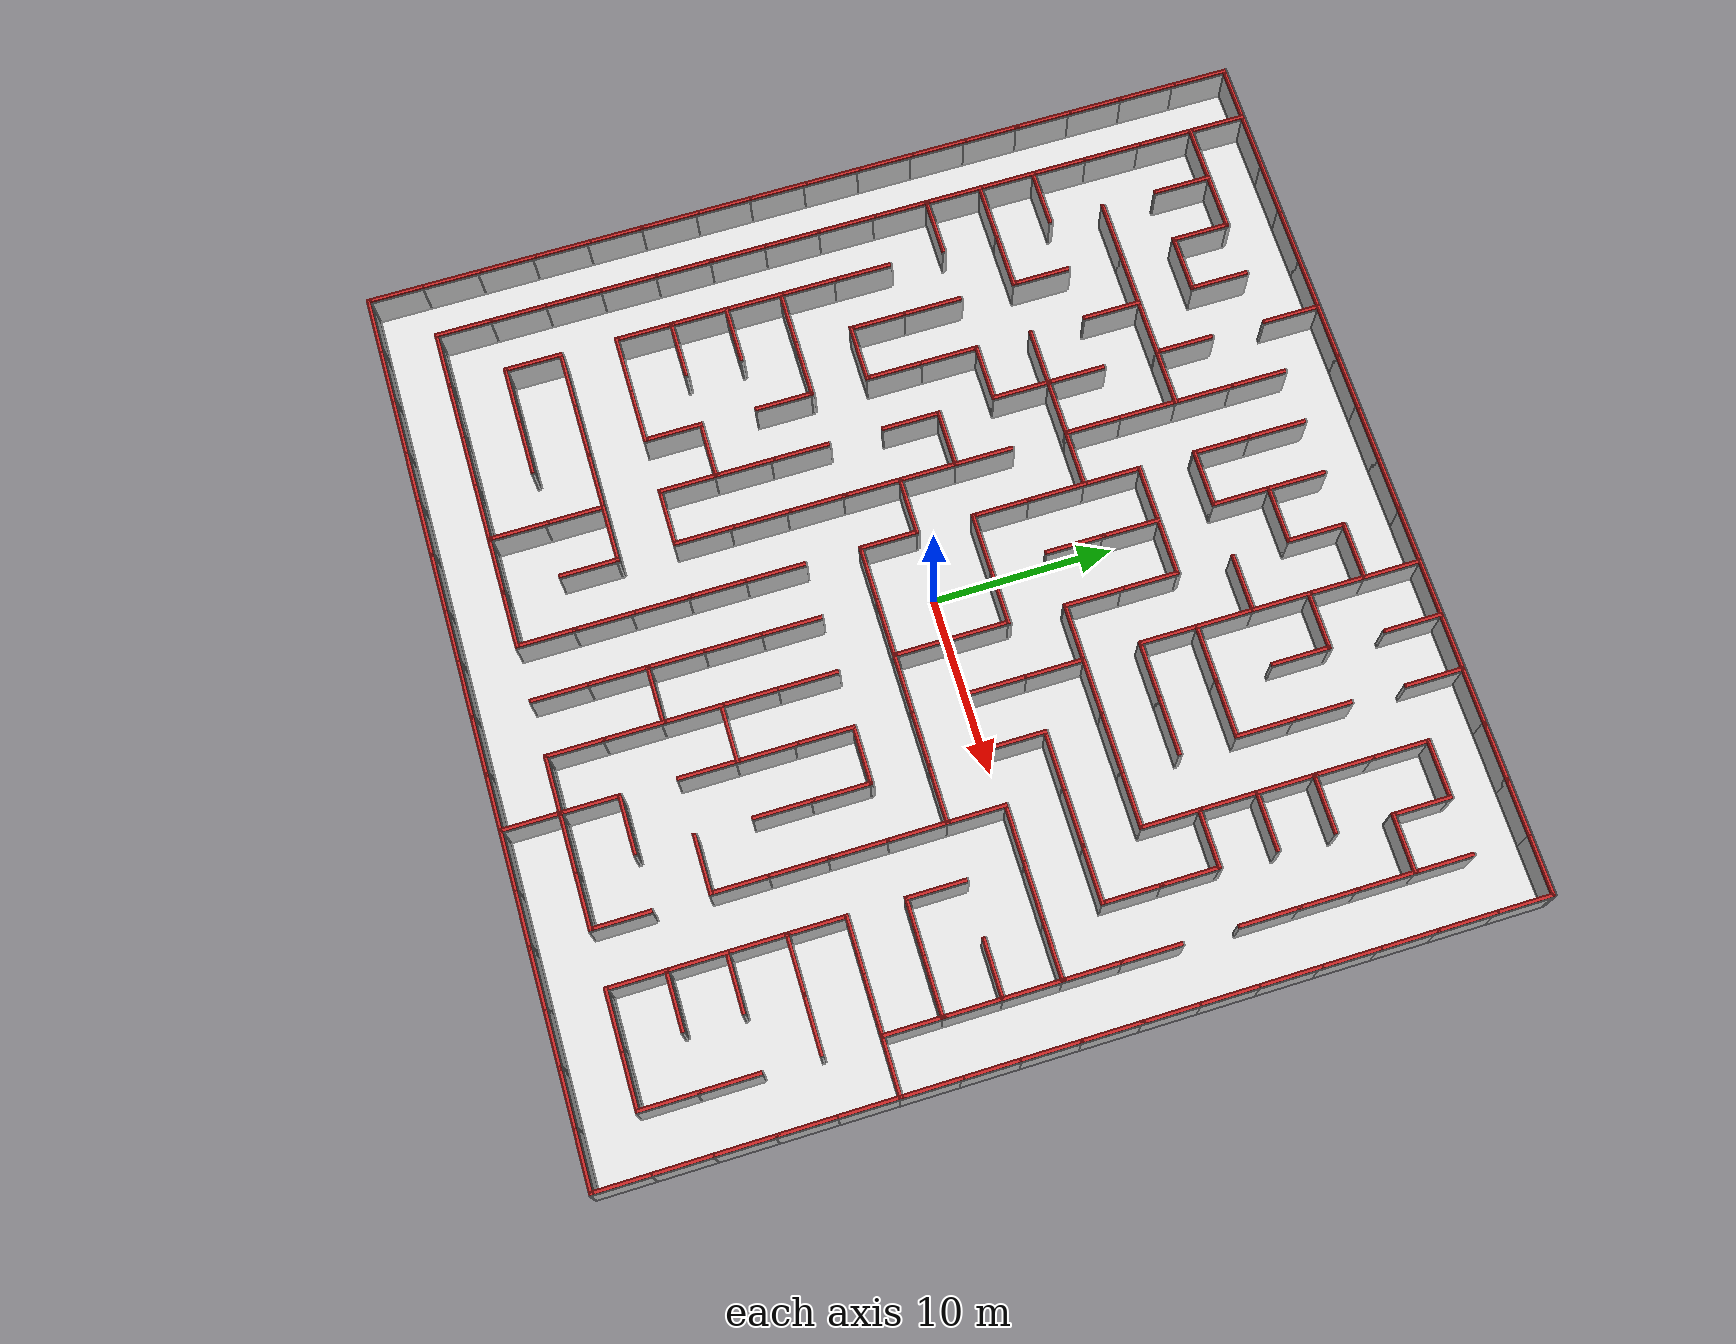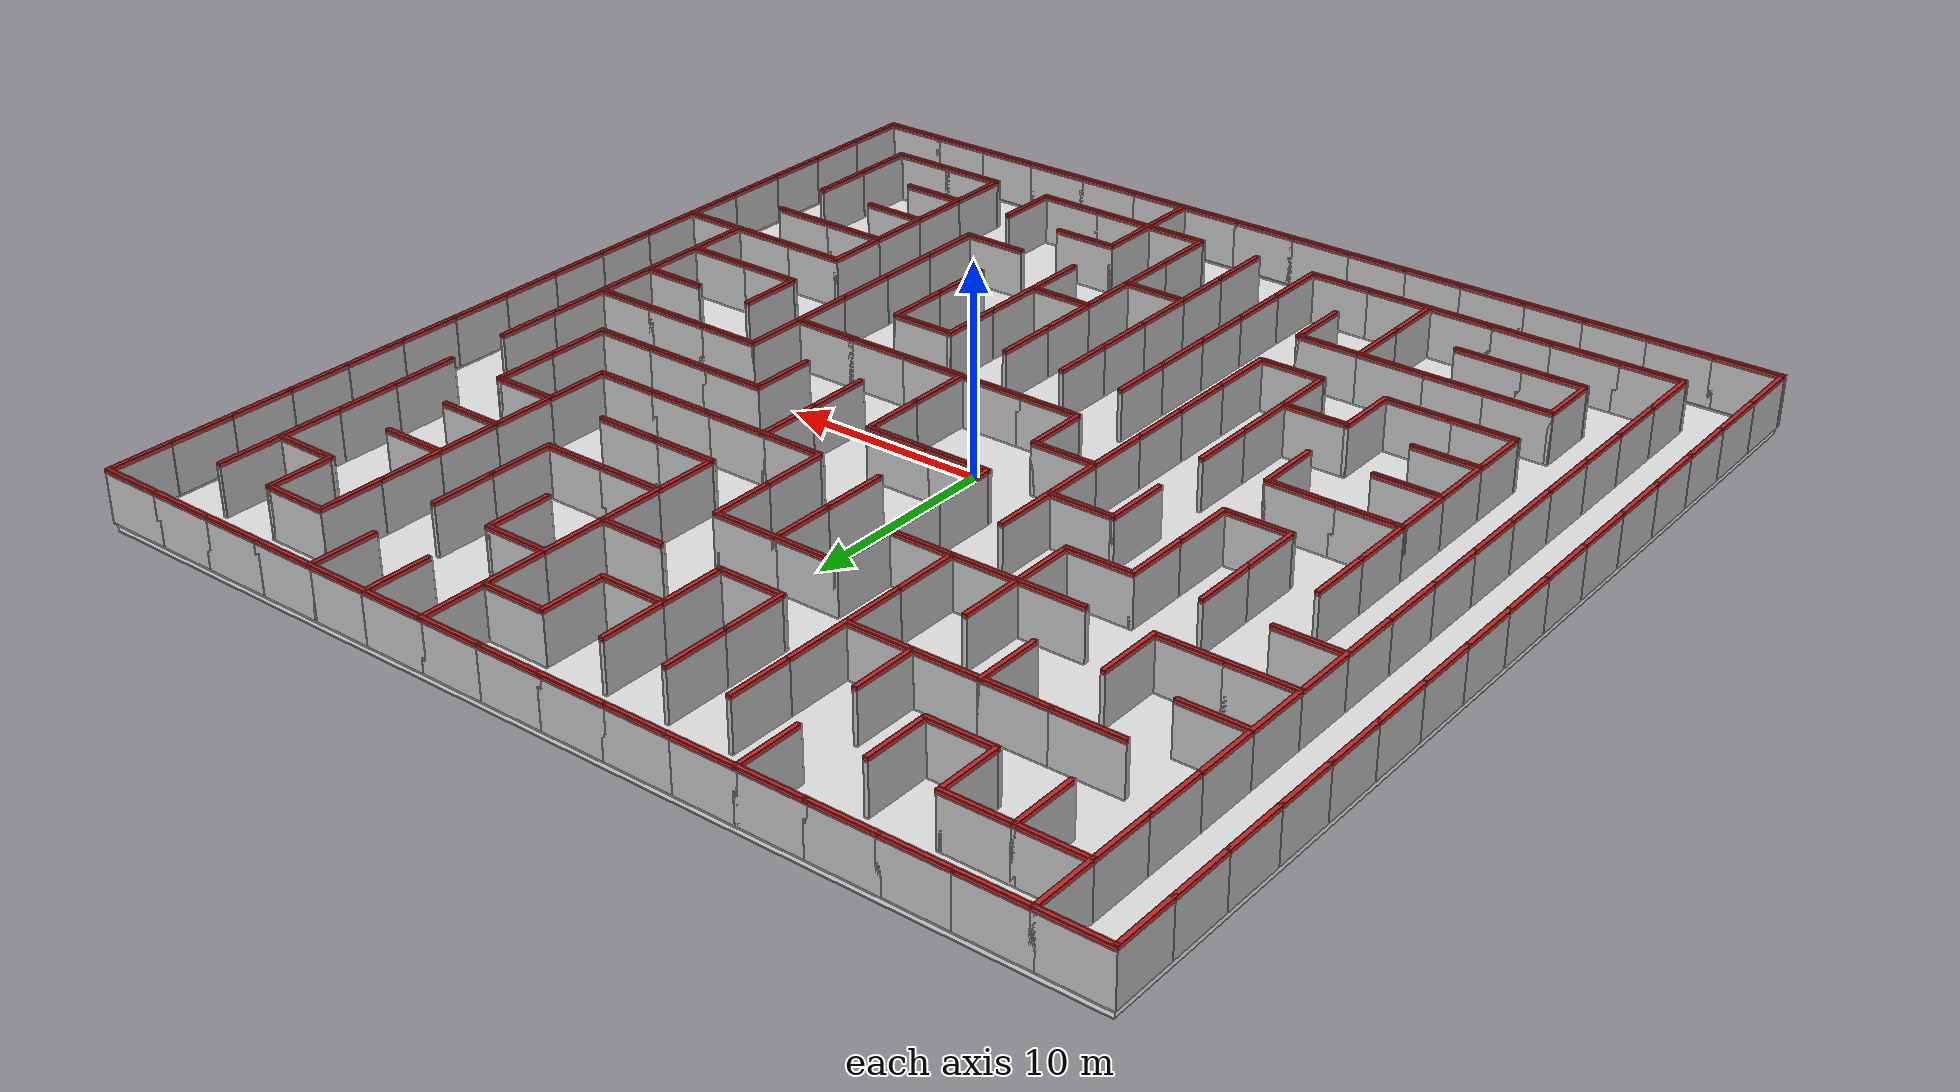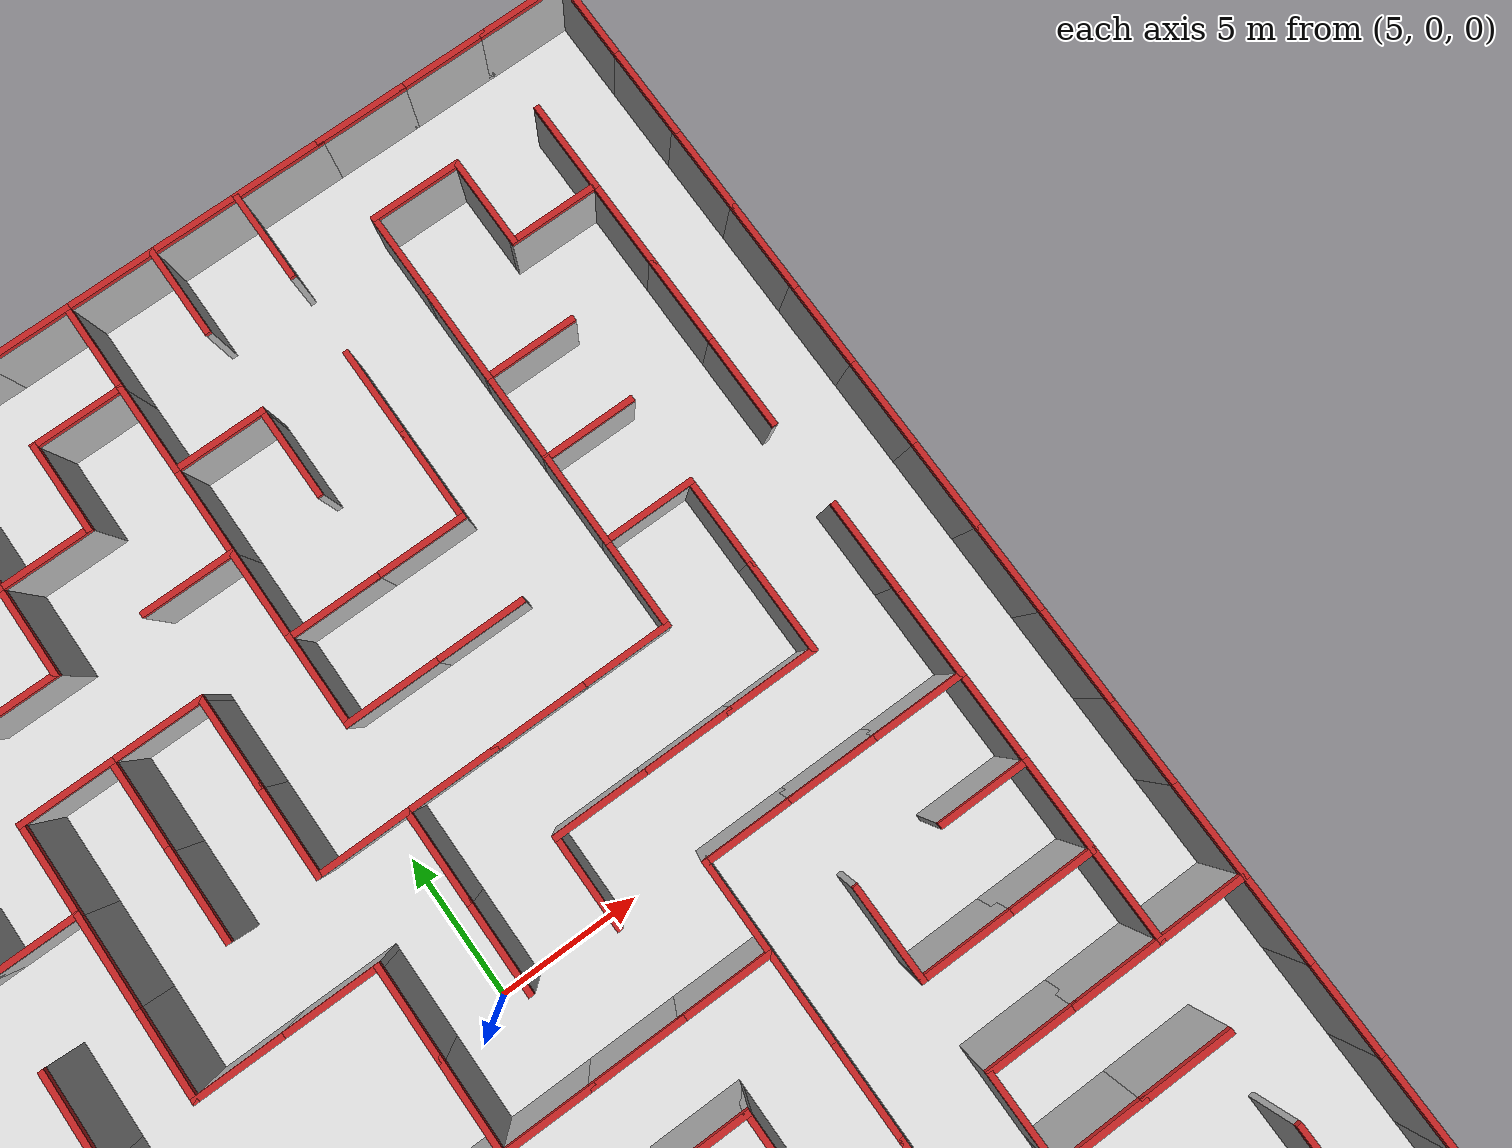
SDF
<?xml version='1.0'?>
<sdf version='1.5'>
	<model name='my_maze'>
		<link name='base'>
			<pose frame=''>0 0 0 0 -0 0</pose>
			<inertial>
				<mass>1</mass>
				<inertia>
					<ixx>1.39394</ixx>
					<ixy>0</ixy>
					<ixz>0</ixz>
					<iyy>0.696972</iyy>
					<iyz>0</iyz>
					<izz>0.696973</izz>
				</inertia>
				<pose frame=''>0 0 0.05 0 -0 0</pose>
			</inertial>
			<self_collide>0</self_collide>
			<kinematic>0</kinematic>
			<visual name='visual'>
				<pose frame=''>0 0 0.0025 0 -0 0</pose>
				<geometry>
					<box>
						<size>50 50 0.25</size>
					</box>
				</geometry>
				<material>
					<script>
						<uri>file://media/materials/scripts/gazebo.material</uri>
						<name>Gazebo/White</name>
					</script>
				</material>
			</visual>
			<collision name='collision'>
				<pose frame=''>0 0 0.0025 0 -0 0</pose>
				<geometry>
					<box>
						<size>50 50 0.25</size>
					</box>
				</geometry>
				<surface>
					<friction>
						<ode>
							<mu>1000</mu>
							<mu2>1000</mu2>
						</ode>
						<torsional>
							<ode/>
						</torsional>
					</friction>
					<contact>
						<ode/>
					</contact>
					<bounce/>
				</surface>
				<max_contacts>10</max_contacts>
			</collision>
			<visual name='paint_v_0_0_W'>
				<pose frame=''>-25 23.4375 2.66319 0 -0 1.5708</pose>
				<geometry>
					<box>
						<size>3.33333 0.208333 0.173611</size>
					</box>
				</geometry>
				<material>
					<script>
						<name>Gazebo/Red</name>
						<uri>file://media/materials/scripts/gazebo.material</uri>
					</script>
				</material>
			</visual>
			<visual name='v_0_0_W'>
				<pose frame=''>-25 23.4375 1.41319 0 -0 1.5708</pose>
				<geometry>
					<box>
						<size>3.33333 0.208333 2.32639</size>
					</box>
				</geometry>
			</visual>
			<collision name='p_0_0_W'>
				<pose frame=''>-25 23.4375 1.5 0 -0 1.5708</pose>
				<geometry>
					<box>
						<size>3.33333 0.208333 2.5</size>
					</box>
				</geometry>
				<max_contacts>10</max_contacts>
				<surface>
					<contact>
						<ode/>
					</contact>
					<bounce/>
					<friction>
						<torsional>
							<ode/>
						</torsional>
						<ode/>
					</friction>
				</surface>
			</collision>
			<visual name='paint_v_0_1_W'>
				<pose frame=''>-21.875 23.4375 2.66319 0 -0 1.5708</pose>
				<geometry>
					<box>
						<size>3.33333 0.208333 0.173611</size>
					</box>
				</geometry>
				<material>
					<script>
						<name>Gazebo/Red</name>
						<uri>file://media/materials/scripts/gazebo.material</uri>
					</script>
				</material>
			</visual>
			<visual name='v_0_1_W'>
				<pose frame=''>-21.875 23.4375 1.41319 0 -0 1.5708</pose>
				<geometry>
					<box>
						<size>3.33333 0.208333 2.32639</size>
					</box>
				</geometry>
			</visual>
			<collision name='p_0_1_W'>
				<pose frame=''>-21.875 23.4375 1.5 0 -0 1.5708</pose>
				<geometry>
					<box>
						<size>3.33333 0.208333 2.5</size>
					</box>
				</geometry>
				<max_contacts>10</max_contacts>
				<surface>
					<contact>
						<ode/>
					</contact>
					<bounce/>
					<friction>
						<torsional>
							<ode/>
						</torsional>
						<ode/>
					</friction>
				</surface>
			</collision>
			<visual name='paint_v_0_1_S'>
				<pose frame=''>-20.3125 21.875 2.66319 0 -0 0</pose>
				<geometry>
					<box>
						<size>3.33333 0.208333 0.173611</size>
					</box>
				</geometry>
				<material>
					<script>
						<name>Gazebo/Red</name>
						<uri>file://media/materials/scripts/gazebo.material</uri>
					</script>
				</material>
			</visual>
			<visual name='v_0_1_S'>
				<pose frame=''>-20.3125 21.875 1.41319 0 -0 0</pose>
				<geometry>
					<box>
						<size>3.33333 0.208333 2.32639</size>
					</box>
				</geometry>
			</visual>
			<collision name='p_0_1_S'>
				<pose frame=''>-20.3125 21.875 1.5 0 -0 0</pose>
				<geometry>
					<box>
						<size>3.33333 0.208333 2.5</size>
					</box>
				</geometry>
				<max_contacts>10</max_contacts>
				<surface>
					<contact>
						<ode/>
					</contact>
					<bounce/>
					<friction>
						<torsional>
							<ode/>
						</torsional>
						<ode/>
					</friction>
				</surface>
			</collision>
			<visual name='paint_v_0_2_S'>
				<pose frame=''>-17.1875 21.875 2.66319 0 -0 0</pose>
				<geometry>
					<box>
						<size>3.33333 0.208333 0.173611</size>
					</box>
				</geometry>
				<material>
					<script>
						<name>Gazebo/Red</name>
						<uri>file://media/materials/scripts/gazebo.material</uri>
					</script>
				</material>
			</visual>
			<visual name='v_0_2_S'>
				<pose frame=''>-17.1875 21.875 1.41319 0 -0 0</pose>
				<geometry>
					<box>
						<size>3.33333 0.208333 2.32639</size>
					</box>
				</geometry>
			</visual>
			<collision name='p_0_2_S'>
				<pose frame=''>-17.1875 21.875 1.5 0 -0 0</pose>
				<geometry>
					<box>
						<size>3.33333 0.208333 2.5</size>
					</box>
				</geometry>
				<max_contacts>10</max_contacts>
				<surface>
					<contact>
						<ode/>
					</contact>
					<bounce/>
					<friction>
						<torsional>
							<ode/>
						</torsional>
						<ode/>
					</friction>
				</surface>
			</collision>
			<visual name='paint_v_0_5_W'>
				<pose frame=''>-9.375 23.4375 2.66319 0 -0 1.5708</pose>
				<geometry>
					<box>
						<size>3.33333 0.208333 0.173611</size>
					</box>
				</geometry>
				<material>
					<script>
						<name>Gazebo/Red</name>
						<uri>file://media/materials/scripts/gazebo.material</uri>
					</script>
				</material>
			</visual>
			<visual name='v_0_5_W'>
				<pose frame=''>-9.375 23.4375 1.41319 0 -0 1.5708</pose>
				<geometry>
					<box>
						<size>3.33333 0.208333 2.32639</size>
					</box>
				</geometry>
			</visual>
			<collision name='p_0_5_W'>
				<pose frame=''>-9.375 23.4375 1.5 0 -0 1.5708</pose>
				<geometry>
					<box>
						<size>3.33333 0.208333 2.5</size>
					</box>
				</geometry>
				<max_contacts>10</max_contacts>
				<surface>
					<contact>
						<ode/>
					</contact>
					<bounce/>
					<friction>
						<torsional>
							<ode/>
						</torsional>
						<ode/>
					</friction>
				</surface>
			</collision>
			<visual name='paint_v_0_9_S'>
				<pose frame=''>4.6875 21.875 2.66319 0 -0 0</pose>
				<geometry>
					<box>
						<size>3.33333 0.208333 0.173611</size>
					</box>
				</geometry>
				<material>
					<script>
						<name>Gazebo/Red</name>
						<uri>file://media/materials/scripts/gazebo.material</uri>
					</script>
				</material>
			</visual>
			<visual name='v_0_9_S'>
				<pose frame=''>4.6875 21.875 1.41319 0 -0 0</pose>
				<geometry>
					<box>
						<size>3.33333 0.208333 2.32639</size>
					</box>
				</geometry>
			</visual>
			<collision name='p_0_9_S'>
				<pose frame=''>4.6875 21.875 1.5 0 -0 0</pose>
				<geometry>
					<box>
						<size>3.33333 0.208333 2.5</size>
					</box>
				</geometry>
				<max_contacts>10</max_contacts>
				<surface>
					<contact>
						<ode/>
					</contact>
					<bounce/>
					<friction>
						<torsional>
							<ode/>
						</torsional>
						<ode/>
					</friction>
				</surface>
			</collision>
			<visual name='paint_v_0_10_W'>
				<pose frame=''>6.25 23.4375 2.66319 0 -0 1.5708</pose>
				<geometry>
					<box>
						<size>3.33333 0.208333 0.173611</size>
					</box>
				</geometry>
				<material>
					<script>
						<name>Gazebo/Red</name>
						<uri>file://media/materials/scripts/gazebo.material</uri>
					</script>
				</material>
			</visual>
			<visual name='v_0_10_W'>
				<pose frame=''>6.25 23.4375 1.41319 0 -0 1.5708</pose>
				<geometry>
					<box>
						<size>3.33333 0.208333 2.32639</size>
					</box>
				</geometry>
			</visual>
			<collision name='p_0_10_W'>
				<pose frame=''>6.25 23.4375 1.5 0 -0 1.5708</pose>
				<geometry>
					<box>
						<size>3.33333 0.208333 2.5</size>
					</box>
				</geometry>
				<max_contacts>10</max_contacts>
				<surface>
					<contact>
						<ode/>
					</contact>
					<bounce/>
					<friction>
						<torsional>
							<ode/>
						</torsional>
						<ode/>
					</friction>
				</surface>
			</collision>
			<visual name='paint_v_0_11_W'>
				<pose frame=''>9.375 23.4375 2.66319 0 -0 1.5708</pose>
				<geometry>
					<box>
						<size>3.33333 0.208333 0.173611</size>
					</box>
				</geometry>
				<material>
					<script>
						<name>Gazebo/Red</name>
						<uri>file://media/materials/scripts/gazebo.material</uri>
					</script>
				</material>
			</visual>
			<visual name='v_0_11_W'>
				<pose frame=''>9.375 23.4375 1.41319 0 -0 1.5708</pose>
				<geometry>
					<box>
						<size>3.33333 0.208333 2.32639</size>
					</box>
				</geometry>
			</visual>
			<collision name='p_0_11_W'>
				<pose frame=''>9.375 23.4375 1.5 0 -0 1.5708</pose>
				<geometry>
					<box>
						<size>3.33333 0.208333 2.5</size>
					</box>
				</geometry>
				<max_contacts>10</max_contacts>
				<surface>
					<contact>
						<ode/>
					</contact>
					<bounce/>
					<friction>
						<torsional>
							<ode/>
						</torsional>
						<ode/>
					</friction>
				</surface>
			</collision>
			<visual name='paint_v_0_12_W'>
				<pose frame=''>12.5 23.4375 2.66319 0 -0 1.5708</pose>
				<geometry>
					<box>
						<size>3.33333 0.208333 0.173611</size>
					</box>
				</geometry>
				<material>
					<script>
						<name>Gazebo/Red</name>
						<uri>file://media/materials/scripts/gazebo.material</uri>
					</script>
				</material>
			</visual>
			<visual name='v_0_12_W'>
				<pose frame=''>12.5 23.4375 1.41319 0 -0 1.5708</pose>
				<geometry>
					<box>
						<size>3.33333 0.208333 2.32639</size>
					</box>
				</geometry>
			</visual>
			<collision name='p_0_12_W'>
				<pose frame=''>12.5 23.4375 1.5 0 -0 1.5708</pose>
				<geometry>
					<box>
						<size>3.33333 0.208333 2.5</size>
					</box>
				</geometry>
				<max_contacts>10</max_contacts>
				<surface>
					<contact>
						<ode/>
					</contact>
					<bounce/>
					<friction>
						<torsional>
							<ode/>
						</torsional>
						<ode/>
					</friction>
				</surface>
			</collision>
			<visual name='paint_v_0_13_S'>
				<pose frame=''>17.1875 21.875 2.66319 0 -0 0</pose>
				<geometry>
					<box>
						<size>3.33333 0.208333 0.173611</size>
					</box>
				</geometry>
				<material>
					<script>
						<name>Gazebo/Red</name>
						<uri>file://media/materials/scripts/gazebo.material</uri>
					</script>
				</material>
			</visual>
			<visual name='v_0_13_S'>
				<pose frame=''>17.1875 21.875 1.41319 0 -0 0</pose>
				<geometry>
					<box>
						<size>3.33333 0.208333 2.32639</size>
					</box>
				</geometry>
			</visual>
			<collision name='p_0_13_S'>
				<pose frame=''>17.1875 21.875 1.5 0 -0 0</pose>
				<geometry>
					<box>
						<size>3.33333 0.208333 2.5</size>
					</box>
				</geometry>
				<max_contacts>10</max_contacts>
				<surface>
					<contact>
						<ode/>
					</contact>
					<bounce/>
					<friction>
						<torsional>
							<ode/>
						</torsional>
						<ode/>
					</friction>
				</surface>
			</collision>
			<visual name='paint_v_1_0_W'>
				<pose frame=''>-25 20.3125 2.66319 0 -0 1.5708</pose>
				<geometry>
					<box>
						<size>3.33333 0.208333 0.173611</size>
					</box>
				</geometry>
				<material>
					<script>
						<name>Gazebo/Red</name>
						<uri>file://media/materials/scripts/gazebo.material</uri>
					</script>
				</material>
			</visual>
			<visual name='v_1_0_W'>
				<pose frame=''>-25 20.3125 1.41319 0 -0 1.5708</pose>
				<geometry>
					<box>
						<size>3.33333 0.208333 2.32639</size>
					</box>
				</geometry>
			</visual>
			<collision name='p_1_0_W'>
				<pose frame=''>-25 20.3125 1.5 0 -0 1.5708</pose>
				<geometry>
					<box>
						<size>3.33333 0.208333 2.5</size>
					</box>
				</geometry>
				<max_contacts>10</max_contacts>
				<surface>
					<contact>
						<ode/>
					</contact>
					<bounce/>
					<friction>
						<torsional>
							<ode/>
						</torsional>
						<ode/>
					</friction>
				</surface>
			</collision>
			<visual name='paint_v_1_1_W'>
				<pose frame=''>-21.875 20.3125 2.66319 0 -0 1.5708</pose>
				<geometry>
					<box>
						<size>3.33333 0.208333 0.173611</size>
					</box>
				</geometry>
				<material>
					<script>
						<name>Gazebo/Red</name>
						<uri>file://media/materials/scripts/gazebo.material</uri>
					</script>
				</material>
			</visual>
			<visual name='v_1_1_W'>
				<pose frame=''>-21.875 20.3125 1.41319 0 -0 1.5708</pose>
				<geometry>
					<box>
						<size>3.33333 0.208333 2.32639</size>
					</box>
				</geometry>
			</visual>
			<collision name='p_1_1_W'>
				<pose frame=''>-21.875 20.3125 1.5 0 -0 1.5708</pose>
				<geometry>
					<box>
						<size>3.33333 0.208333 2.5</size>
					</box>
				</geometry>
				<max_contacts>10</max_contacts>
				<surface>
					<contact>
						<ode/>
					</contact>
					<bounce/>
					<friction>
						<torsional>
							<ode/>
						</torsional>
						<ode/>
					</friction>
				</surface>
			</collision>
			<visual name='paint_v_1_2_W'>
				<pose frame=''>-18.75 20.3125 2.66319 0 -0 1.5708</pose>
				<geometry>
					<box>
						<size>3.33333 0.208333 0.173611</size>
					</box>
				</geometry>
				<material>
					<script>
						<name>Gazebo/Red</name>
						<uri>file://media/materials/scripts/gazebo.material</uri>
					</script>
				</material>
			</visual>
			<visual name='v_1_2_W'>
				<pose frame=''>-18.75 20.3125 1.41319 0 -0 1.5708</pose>
				<geometry>
					<box>
						<size>3.33333 0.208333 2.32639</size>
					</box>
				</geometry>
			</visual>
			<collision name='p_1_2_W'>
				<pose frame=''>-18.75 20.3125 1.5 0 -0 1.5708</pose>
				<geometry>
					<box>
						<size>3.33333 0.208333 2.5</size>
					</box>
				</geometry>
				<max_contacts>10</max_contacts>
				<surface>
					<contact>
						<ode/>
					</contact>
					<bounce/>
					<friction>
						<torsional>
							<ode/>
						</torsional>
						<ode/>
					</friction>
				</surface>
			</collision>
			<visual name='paint_v_1_3_W'>
				<pose frame=''>-15.625 20.3125 2.66319 0 -0 1.5708</pose>
				<geometry>
					<box>
						<size>3.33333 0.208333 0.173611</size>
					</box>
				</geometry>
				<material>
					<script>
						<name>Gazebo/Red</name>
						<uri>file://media/materials/scripts/gazebo.material</uri>
					</script>
				</material>
			</visual>
			<visual name='v_1_3_W'>
				<pose frame=''>-15.625 20.3125 1.41319 0 -0 1.5708</pose>
				<geometry>
					<box>
						<size>3.33333 0.208333 2.32639</size>
					</box>
				</geometry>
			</visual>
			<collision name='p_1_3_W'>
				<pose frame=''>-15.625 20.3125 1.5 0 -0 1.5708</pose>
				<geometry>
					<box>
						<size>3.33333 0.208333 2.5</size>
					</box>
				</geometry>
				<max_contacts>10</max_contacts>
				<surface>
					<contact>
						<ode/>
					</contact>
					<bounce/>
					<friction>
						<torsional>
							<ode/>
						</torsional>
						<ode/>
					</friction>
				</surface>
			</collision>
			<visual name='paint_v_1_3_S'>
				<pose frame=''>-14.0625 18.75 2.66319 0 -0 0</pose>
				<geometry>
					<box>
						<size>3.33333 0.208333 0.173611</size>
					</box>
				</geometry>
				<material>
					<script>
						<name>Gazebo/Red</name>
						<uri>file://media/materials/scripts/gazebo.material</uri>
					</script>
				</material>
			</visual>
			<visual name='v_1_3_S'>
				<pose frame=''>-14.0625 18.75 1.41319 0 -0 0</pose>
				<geometry>
					<box>
						<size>3.33333 0.208333 2.32639</size>
					</box>
				</geometry>
			</visual>
			<collision name='p_1_3_S'>
				<pose frame=''>-14.0625 18.75 1.5 0 -0 0</pose>
				<geometry>
					<box>
						<size>3.33333 0.208333 2.5</size>
					</box>
				</geometry>
				<max_contacts>10</max_contacts>
				<surface>
					<contact>
						<ode/>
					</contact>
					<bounce/>
					<friction>
						<torsional>
							<ode/>
						</torsional>
						<ode/>
					</friction>
				</surface>
			</collision>
			<visual name='paint_v_1_4_W'>
				<pose frame=''>-12.5 20.3125 2.66319 0 -0 1.5708</pose>
				<geometry>
					<box>
						<size>3.33333 0.208333 0.173611</size>
					</box>
				</geometry>
				<material>
					<script>
						<name>Gazebo/Red</name>
						<uri>file://media/materials/scripts/gazebo.material</uri>
					</script>
				</material>
			</visual>
			<visual name='v_1_4_W'>
				<pose frame=''>-12.5 20.3125 1.41319 0 -0 1.5708</pose>
				<geometry>
					<box>
						<size>3.33333 0.208333 2.32639</size>
					</box>
				</geometry>
			</visual>
			<collision name='p_1_4_W'>
				<pose frame=''>-12.5 20.3125 1.5 0 -0 1.5708</pose>
				<geometry>
					<box>
						<size>3.33333 0.208333 2.5</size>
					</box>
				</geometry>
				<max_contacts>10</max_contacts>
				<surface>
					<contact>
						<ode/>
					</contact>
					<bounce/>
					<friction>
						<torsional>
							<ode/>
						</torsional>
						<ode/>
					</friction>
				</surface>
			</collision>
			<visual name='paint_v_1_6_W'>
				<pose frame=''>-6.25 20.3125 2.66319 0 -0 1.5708</pose>
				<geometry>
					<box>
						<size>3.33333 0.208333 0.173611</size>
					</box>
				</geometry>
				<material>
					<script>
						<name>Gazebo/Red</name>
						<uri>file://media/materials/scripts/gazebo.material</uri>
					</script>
				</material>
			</visual>
			<visual name='v_1_6_W'>
				<pose frame=''>-6.25 20.3125 1.41319 0 -0 1.5708</pose>
				<geometry>
					<box>
						<size>3.33333 0.208333 2.32639</size>
					</box>
				</geometry>
			</visual>
			<collision name='p_1_6_W'>
				<pose frame=''>-6.25 20.3125 1.5 0 -0 1.5708</pose>
				<geometry>
					<box>
						<size>3.33333 0.208333 2.5</size>
					</box>
				</geometry>
				<max_contacts>10</max_contacts>
				<surface>
					<contact>
						<ode/>
					</contact>
					<bounce/>
					<friction>
						<torsional>
							<ode/>
						</torsional>
						<ode/>
					</friction>
				</surface>
			</collision>
			<visual name='paint_v_1_7_W'>
				<pose frame=''>-3.125 20.3125 2.66319 0 -0 1.5708</pose>
				<geometry>
					<box>
						<size>3.33333 0.208333 0.173611</size>
					</box>
				</geometry>
				<material>
					<script>
						<name>Gazebo/Red</name>
						<uri>file://media/materials/scripts/gazebo.material</uri>
					</script>
				</material>
			</visual>
			<visual name='v_1_7_W'>
				<pose frame=''>-3.125 20.3125 1.41319 0 -0 1.5708</pose>
				<geometry>
					<box>
						<size>3.33333 0.208333 2.32639</size>
					</box>
				</geometry>
			</visual>
			<collision name='p_1_7_W'>
				<pose frame=''>-3.125 20.3125 1.5 0 -0 1.5708</pose>
				<geometry>
					<box>
						<size>3.33333 0.208333 2.5</size>
					</box>
				</geometry>
				<max_contacts>10</max_contacts>
				<surface>
					<contact>
						<ode/>
					</contact>
					<bounce/>
					<friction>
						<torsional>
							<ode/>
						</torsional>
						<ode/>
					</friction>
				</surface>
			</collision>
			<visual name='paint_v_1_8_W'>
				<pose frame=''>0 20.3125 2.66319 0 -0 1.5708</pose>
				<geometry>
					<box>
						<size>3.33333 0.208333 0.173611</size>
					</box>
				</geometry>
				<material>
					<script>
						<name>Gazebo/Red</name>
						<uri>file://media/materials/scripts/gazebo.material</uri>
					</script>
				</material>
			</visual>
			<visual name='v_1_8_W'>
				<pose frame=''>0 20.3125 1.41319 0 -0 1.5708</pose>
				<geometry>
					<box>
						<size>3.33333 0.208333 2.32639</size>
					</box>
				</geometry>
			</visual>
			<collision name='p_1_8_W'>
				<pose frame=''>0 20.3125 1.5 0 -0 1.5708</pose>
				<geometry>
					<box>
						<size>3.33333 0.208333 2.5</size>
					</box>
				</geometry>
				<max_contacts>10</max_contacts>
				<surface>
					<contact>
						<ode/>
					</contact>
					<bounce/>
					<friction>
						<torsional>
							<ode/>
						</torsional>
						<ode/>
					</friction>
				</surface>
			</collision>
			<visual name='paint_v_1_8_S'>
				<pose frame=''>1.5625 18.75 2.66319 0 -0 0</pose>
				<geometry>
					<box>
						<size>3.33333 0.208333 0.173611</size>
					</box>
				</geometry>
				<material>
					<script>
						<name>Gazebo/Red</name>
						<uri>file://media/materials/scripts/gazebo.material</uri>
					</script>
				</material>
			</visual>
			<visual name='v_1_8_S'>
				<pose frame=''>1.5625 18.75 1.41319 0 -0 0</pose>
				<geometry>
					<box>
						<size>3.33333 0.208333 2.32639</size>
					</box>
				</geometry>
			</visual>
			<collision name='p_1_8_S'>
				<pose frame=''>1.5625 18.75 1.5 0 -0 0</pose>
				<geometry>
					<box>
						<size>3.33333 0.208333 2.5</size>
					</box>
				</geometry>
				<max_contacts>10</max_contacts>
				<surface>
					<contact>
						<ode/>
					</contact>
					<bounce/>
					<friction>
						<torsional>
							<ode/>
						</torsional>
						<ode/>
					</friction>
				</surface>
			</collision>
			<visual name='paint_v_1_9_W'>
				<pose frame=''>3.125 20.3125 2.66319 0 -0 1.5708</pose>
				<geometry>
					<box>
						<size>3.33333 0.208333 0.173611</size>
					</box>
				</geometry>
				<material>
					<script>
						<name>Gazebo/Red</name>
						<uri>file://media/materials/scripts/gazebo.material</uri>
					</script>
				</material>
			</visual>
			<visual name='v_1_9_W'>
				<pose frame=''>3.125 20.3125 1.41319 0 -0 1.5708</pose>
				<geometry>
					<box>
						<size>3.33333 0.208333 2.32639</size>
					</box>
				</geometry>
			</visual>
			<collision name='p_1_9_W'>
				<pose frame=''>3.125 20.3125 1.5 0 -0 1.5708</pose>
				<geometry>
					<box>
						<size>3.33333 0.208333 2.5</size>
					</box>
				</geometry>
				<max_contacts>10</max_contacts>
				<surface>
					<contact>
						<ode/>
					</contact>
					<bounce/>
					<friction>
						<torsional>
							<ode/>
						</torsional>
						<ode/>
					</friction>
				</surface>
			</collision>
			<visual name='paint_v_1_10_W'>
				<pose frame=''>6.25 20.3125 2.66319 0 -0 1.5708</pose>
				<geometry>
					<box>
						<size>3.33333 0.208333 0.173611</size>
					</box>
				</geometry>
				<material>
					<script>
						<name>Gazebo/Red</name>
						<uri>file://media/materials/scripts/gazebo.material</uri>
					</script>
				</material>
			</visual>
			<visual name='v_1_10_W'>
				<pose frame=''>6.25 20.3125 1.41319 0 -0 1.5708</pose>
				<geometry>
					<box>
						<size>3.33333 0.208333 2.32639</size>
					</box>
				</geometry>
			</visual>
			<collision name='p_1_10_W'>
				<pose frame=''>6.25 20.3125 1.5 0 -0 1.5708</pose>
				<geometry>
					<box>
						<size>3.33333 0.208333 2.5</size>
					</box>
				</geometry>
				<max_contacts>10</max_contacts>
				<surface>
					<contact>
						<ode/>
					</contact>
					<bounce/>
					<friction>
						<torsional>
							<ode/>
						</torsional>
						<ode/>
					</friction>
				</surface>
			</collision>
			<visual name='paint_v_1_10_S'>
				<pose frame=''>7.8125 18.75 2.66319 0 -0 0</pose>
				<geometry>
					<box>
						<size>3.33333 0.208333 0.173611</size>
					</box>
				</geometry>
				<material>
					<script>
						<name>Gazebo/Red</name>
						<uri>file://media/materials/scripts/gazebo.material</uri>
					</script>
				</material>
			</visual>
			<visual name='v_1_10_S'>
				<pose frame=''>7.8125 18.75 1.41319 0 -0 0</pose>
				<geometry>
					<box>
						<size>3.33333 0.208333 2.32639</size>
					</box>
				</geometry>
			</visual>
			<collision name='p_1_10_S'>
				<pose frame=''>7.8125 18.75 1.5 0 -0 0</pose>
				<geometry>
					<box>
						<size>3.33333 0.208333 2.5</size>
					</box>
				</geometry>
				<max_contacts>10</max_contacts>
				<surface>
					<contact>
						<ode/>
					</contact>
					<bounce/>
					<friction>
						<torsional>
							<ode/>
						</torsional>
						<ode/>
					</friction>
				</surface>
			</collision>
			<visual name='paint_v_1_13_W'>
				<pose frame=''>15.625 20.3125 2.66319 0 -0 1.5708</pose>
				<geometry>
					<box>
						<size>3.33333 0.208333 0.173611</size>
					</box>
				</geometry>
				<material>
					<script>
						<name>Gazebo/Red</name>
						<uri>file://media/materials/scripts/gazebo.material</uri>
					</script>
				</material>
			</visual>
			<visual name='v_1_13_W'>
				<pose frame=''>15.625 20.3125 1.41319 0 -0 1.5708</pose>
				<geometry>
					<box>
						<size>3.33333 0.208333 2.32639</size>
					</box>
				</geometry>
			</visual>
			<collision name='p_1_13_W'>
				<pose frame=''>15.625 20.3125 1.5 0 -0 1.5708</pose>
				<geometry>
					<box>
						<size>3.33333 0.208333 2.5</size>
					</box>
				</geometry>
				<max_contacts>10</max_contacts>
				<surface>
					<contact>
						<ode/>
					</contact>
					<bounce/>
					<friction>
						<torsional>
							<ode/>
						</torsional>
						<ode/>
					</friction>
				</surface>
			</collision>
			<visual name='paint_v_1_14_W'>
				<pose frame=''>18.75 20.3125 2.66319 0 -0 1.5708</pose>
				<geometry>
					<box>
						<size>3.33333 0.208333 0.173611</size>
					</box>
				</geometry>
				<material>
					<script>
						<name>Gazebo/Red</name>
						<uri>file://media/materials/scripts/gazebo.material</uri>
					</script>
				</material>
			</visual>
			<visual name='v_1_14_W'>
				<pose frame=''>18.75 20.3125 1.41319 0 -0 1.5708</pose>
				<geometry>
					<box>
						<size>3.33333 0.208333 2.32639</size>
					</box>
				</geometry>
			</visual>
			<collision name='p_1_14_W'>
				<pose frame=''>18.75 20.3125 1.5 0 -0 1.5708</pose>
				<geometry>
					<box>
						<size>3.33333 0.208333 2.5</size>
					</box>
				</geometry>
				<max_contacts>10</max_contacts>
				<surface>
					<contact>
						<ode/>
					</contact>
					<bounce/>
					<friction>
						<torsional>
							<ode/>
						</torsional>
						<ode/>
					</friction>
				</surface>
			</collision>
			<visual name='paint_v_1_14_S'>
				<pose frame=''>20.3125 18.75 2.66319 0 -0 0</pose>
				<geometry>
					<box>
						<size>3.33333 0.208333 0.173611</size>
					</box>
				</geometry>
				<material>
					<script>
						<name>Gazebo/Red</name>
						<uri>file://media/materials/scripts/gazebo.material</uri>
					</script>
				</material>
			</visual>
			<visual name='v_1_14_S'>
				<pose frame=''>20.3125 18.75 1.41319 0 -0 0</pose>
				<geometry>
					<box>
						<size>3.33333 0.208333 2.32639</size>
					</box>
				</geometry>
			</visual>
			<collision name='p_1_14_S'>
				<pose frame=''>20.3125 18.75 1.5 0 -0 0</pose>
				<geometry>
					<box>
						<size>3.33333 0.208333 2.5</size>
					</box>
				</geometry>
				<max_contacts>10</max_contacts>
				<surface>
					<contact>
						<ode/>
					</contact>
					<bounce/>
					<friction>
						<torsional>
							<ode/>
						</torsional>
						<ode/>
					</friction>
				</surface>
			</collision>
			<visual name='paint_v_1_15_W'>
				<pose frame=''>21.875 20.3125 2.66319 0 -0 1.5708</pose>
				<geometry>
					<box>
						<size>3.33333 0.208333 0.173611</size>
					</box>
				</geometry>
				<material>
					<script>
						<name>Gazebo/Red</name>
						<uri>file://media/materials/scripts/gazebo.material</uri>
					</script>
				</material>
			</visual>
			<visual name='v_1_15_W'>
				<pose frame=''>21.875 20.3125 1.41319 0 -0 1.5708</pose>
				<geometry>
					<box>
						<size>3.33333 0.208333 2.32639</size>
					</box>
				</geometry>
			</visual>
			<collision name='p_1_15_W'>
				<pose frame=''>21.875 20.3125 1.5 0 -0 1.5708</pose>
				<geometry>
					<box>
						<size>3.33333 0.208333 2.5</size>
					</box>
				</geometry>
				<max_contacts>10</max_contacts>
				<surface>
					<contact>
						<ode/>
					</contact>
					<bounce/>
					<friction>
						<torsional>
							<ode/>
						</torsional>
						<ode/>
					</friction>
				</surface>
			</collision>
			<visual name='paint_v_2_0_W'>
				<pose frame=''>-25 17.1875 2.66319 0 -0 1.5708</pose>
				<geometry>
					<box>
						<size>3.33333 0.208333 0.173611</size>
					</box>
				</geometry>
				<material>
					<script>
						<name>Gazebo/Red</name>
						<uri>file://media/materials/scripts/gazebo.material</uri>
					</script>
				</material>
			</visual>
			<visual name='v_2_0_W'>
				<pose frame=''>-25 17.1875 1.41319 0 -0 1.5708</pose>
				<geometry>
					<box>
						<size>3.33333 0.208333 2.32639</size>
					</box>
				</geometry>
			</visual>
			<collision name='p_2_0_W'>
				<pose frame=''>-25 17.1875 1.5 0 -0 1.5708</pose>
				<geometry>
					<box>
						<size>3.33333 0.208333 2.5</size>
					</box>
				</geometry>
				<max_contacts>10</max_contacts>
				<surface>
					<contact>
						<ode/>
					</contact>
					<bounce/>
					<friction>
						<torsional>
							<ode/>
						</torsional>
						<ode/>
					</friction>
				</surface>
			</collision>
			<visual name='paint_v_2_1_W'>
				<pose frame=''>-21.875 17.1875 2.66319 0 -0 1.5708</pose>
				<geometry>
					<box>
						<size>3.33333 0.208333 0.173611</size>
					</box>
				</geometry>
				<material>
					<script>
						<name>Gazebo/Red</name>
						<uri>file://media/materials/scripts/gazebo.material</uri>
					</script>
				</material>
			</visual>
			<visual name='v_2_1_W'>
				<pose frame=''>-21.875 17.1875 1.41319 0 -0 1.5708</pose>
				<geometry>
					<box>
						<size>3.33333 0.208333 2.32639</size>
					</box>
				</geometry>
			</visual>
			<collision name='p_2_1_W'>
				<pose frame=''>-21.875 17.1875 1.5 0 -0 1.5708</pose>
				<geometry>
					<box>
						<size>3.33333 0.208333 2.5</size>
					</box>
				</geometry>
				<max_contacts>10</max_contacts>
				<surface>
					<contact>
						<ode/>
					</contact>
					<bounce/>
					<friction>
						<torsional>
							<ode/>
						</torsional>
						<ode/>
					</friction>
				</surface>
			</collision>
			<visual name='paint_v_2_2_S'>
				<pose frame=''>-17.1875 15.625 2.66319 0 -0 0</pose>
				<geometry>
					<box>
						<size>3.33333 0.208333 0.173611</size>
					</box>
				</geometry>
				<material>
					<script>
						<name>Gazebo/Red</name>
						<uri>file://media/materials/scripts/gazebo.material</uri>
					</script>
				</material>
			</visual>
			<visual name='v_2_2_S'>
				<pose frame=''>-17.1875 15.625 1.41319 0 -0 0</pose>
				<geometry>
					<box>
						<size>3.33333 0.208333 2.32639</size>
					</box>
				</geometry>
			</visual>
			<collision name='p_2_2_S'>
				<pose frame=''>-17.1875 15.625 1.5 0 -0 0</pose>
				<geometry>
					<box>
						<size>3.33333 0.208333 2.5</size>
					</box>
				</geometry>
				<max_contacts>10</max_contacts>
				<surface>
					<contact>
						<ode/>
					</contact>
					<bounce/>
					<friction>
						<torsional>
							<ode/>
						</torsional>
						<ode/>
					</friction>
				</surface>
			</collision>
			<visual name='paint_v_2_3_S'>
				<pose frame=''>-14.0625 15.625 2.66319 0 -0 0</pose>
				<geometry>
					<box>
						<size>3.33333 0.208333 0.173611</size>
					</box>
				</geometry>
				<material>
					<script>
						<name>Gazebo/Red</name>
						<uri>file://media/materials/scripts/gazebo.material</uri>
					</script>
				</material>
			</visual>
			<visual name='v_2_3_S'>
				<pose frame=''>-14.0625 15.625 1.41319 0 -0 0</pose>
				<geometry>
					<box>
						<size>3.33333 0.208333 2.32639</size>
					</box>
				</geometry>
			</visual>
			<collision name='p_2_3_S'>
				<pose frame=''>-14.0625 15.625 1.5 0 -0 0</pose>
				<geometry>
					<box>
						<size>3.33333 0.208333 2.5</size>
					</box>
				</geometry>
				<max_contacts>10</max_contacts>
				<surface>
					<contact>
						<ode/>
					</contact>
					<bounce/>
					<friction>
						<torsional>
							<ode/>
						</torsional>
						<ode/>
					</friction>
				</surface>
			</collision>
			<visual name='paint_v_2_4_S'>
				<pose frame=''>-10.9375 15.625 2.66319 0 -0 0</pose>
				<geometry>
					<box>
						<size>3.33333 0.208333 0.173611</size>
					</box>
				</geometry>
				<material>
					<script>
						<name>Gazebo/Red</name>
						<uri>file://media/materials/scripts/gazebo.material</uri>
					</script>
				</material>
			</visual>
			<visual name='v_2_4_S'>
				<pose frame=''>-10.9375 15.625 1.41319 0 -0 0</pose>
				<geometry>
					<box>
						<size>3.33333 0.208333 2.32639</size>
					</box>
				</geometry>
			</visual>
			<collision name='p_2_4_S'>
				<pose frame=''>-10.9375 15.625 1.5 0 -0 0</pose>
				<geometry>
					<box>
						<size>3.33333 0.208333 2.5</size>
					</box>
				</geometry>
				<max_contacts>10</max_contacts>
				<surface>
					<contact>
						<ode/>
					</contact>
					<bounce/>
					<friction>
						<torsional>
							<ode/>
						</torsional>
						<ode/>
					</friction>
				</surface>
			</collision>
			<visual name='paint_v_2_5_W'>
				<pose frame=''>-9.375 17.1875 2.66319 0 -0 1.5708</pose>
				<geometry>
					<box>
						<size>3.33333 0.208333 0.173611</size>
					</box>
				</geometry>
				<material>
					<script>
						<name>Gazebo/Red</name>
						<uri>file://media/materials/scripts/gazebo.material</uri>
					</script>
				</material>
			</visual>
			<visual name='v_2_5_W'>
				<pose frame=''>-9.375 17.1875 1.41319 0 -0 1.5708</pose>
				<geometry>
					<box>
						<size>3.33333 0.208333 2.32639</size>
					</box>
				</geometry>
			</visual>
			<collision name='p_2_5_W'>
				<pose frame=''>-9.375 17.1875 1.5 0 -0 1.5708</pose>
				<geometry>
					<box>
						<size>3.33333 0.208333 2.5</size>
					</box>
				</geometry>
				<max_contacts>10</max_contacts>
				<surface>
					<contact>
						<ode/>
					</contact>
					<bounce/>
					<friction>
						<torsional>
							<ode/>
						</torsional>
						<ode/>
					</friction>
				</surface>
			</collision>
			<visual name='paint_v_2_5_S'>
				<pose frame=''>-7.8125 15.625 2.66319 0 -0 0</pose>
				<geometry>
					<box>
						<size>3.33333 0.208333 0.173611</size>
					</box>
				</geometry>
				<material>
					<script>
						<name>Gazebo/Red</name>
						<uri>file://media/materials/scripts/gazebo.material</uri>
					</script>
				</material>
			</visual>
			<visual name='v_2_5_S'>
				<pose frame=''>-7.8125 15.625 1.41319 0 -0 0</pose>
				<geometry>
					<box>
						<size>3.33333 0.208333 2.32639</size>
					</box>
				</geometry>
			</visual>
			<collision name='p_2_5_S'>
				<pose frame=''>-7.8125 15.625 1.5 0 -0 0</pose>
				<geometry>
					<box>
						<size>3.33333 0.208333 2.5</size>
					</box>
				</geometry>
				<max_contacts>10</max_contacts>
				<surface>
					<contact>
						<ode/>
					</contact>
					<bounce/>
					<friction>
						<torsional>
							<ode/>
						</torsional>
						<ode/>
					</friction>
				</surface>
			</collision>
			<visual name='paint_v_2_6_W'>
				<pose frame=''>-6.25 17.1875 2.66319 0 -0 1.5708</pose>
				<geometry>
					<box>
						<size>3.33333 0.208333 0.173611</size>
					</box>
				</geometry>
				<material>
					<script>
						<name>Gazebo/Red</name>
						<uri>file://media/materials/scripts/gazebo.material</uri>
					</script>
				</material>
			</visual>
			<visual name='v_2_6_W'>
				<pose frame=''>-6.25 17.1875 1.41319 0 -0 1.5708</pose>
				<geometry>
					<box>
						<size>3.33333 0.208333 2.32639</size>
					</box>
				</geometry>
			</visual>
			<collision name='p_2_6_W'>
				<pose frame=''>-6.25 17.1875 1.5 0 -0 1.5708</pose>
				<geometry>
					<box>
						<size>3.33333 0.208333 2.5</size>
					</box>
				</geometry>
				<max_contacts>10</max_contacts>
				<surface>
					<contact>
						<ode/>
					</contact>
					<bounce/>
					<friction>
						<torsional>
							<ode/>
						</torsional>
						<ode/>
					</friction>
				</surface>
			</collision>
			<visual name='paint_v_2_7_W'>
				<pose frame=''>-3.125 17.1875 2.66319 0 -0 1.5708</pose>
				<geometry>
					<box>
						<size>3.33333 0.208333 0.173611</size>
					</box>
				</geometry>
				<material>
					<script>
						<name>Gazebo/Red</name>
						<uri>file://media/materials/scripts/gazebo.material</uri>
					</script>
				</material>
			</visual>
			<visual name='v_2_7_W'>
				<pose frame=''>-3.125 17.1875 1.41319 0 -0 1.5708</pose>
				<geometry>
					<box>
						<size>3.33333 0.208333 2.32639</size>
					</box>
				</geometry>
			</visual>
			<collision name='p_2_7_W'>
				<pose frame=''>-3.125 17.1875 1.5 0 -0 1.5708</pose>
				<geometry>
					<box>
						<size>3.33333 0.208333 2.5</size>
					</box>
				</geometry>
				<max_contacts>10</max_contacts>
				<surface>
					<contact>
						<ode/>
					</contact>
					<bounce/>
					<friction>
						<torsional>
							<ode/>
						</torsional>
						<ode/>
					</friction>
				</surface>
			</collision>
			<visual name='paint_v_2_7_S'>
				<pose frame=''>-1.5625 15.625 2.66319 0 -0 0</pose>
				<geometry>
					<box>
						<size>3.33333 0.208333 0.173611</size>
					</box>
				</geometry>
				<material>
					<script>
						<name>Gazebo/Red</name>
						<uri>file://media/materials/scripts/gazebo.material</uri>
					</script>
				</material>
			</visual>
			<visual name='v_2_7_S'>
				<pose frame=''>-1.5625 15.625 1.41319 0 -0 0</pose>
				<geometry>
					<box>
						<size>3.33333 0.208333 2.32639</size>
					</box>
				</geometry>
			</visual>
			<collision name='p_2_7_S'>
				<pose frame=''>-1.5625 15.625 1.5 0 -0 0</pose>
				<geometry>
					<box>
						<size>3.33333 0.208333 2.5</size>
					</box>
				</geometry>
				<max_contacts>10</max_contacts>
				<surface>
					<contact>
						<ode/>
					</contact>
					<bounce/>
					<friction>
						<torsional>
							<ode/>
						</torsional>
						<ode/>
					</friction>
				</surface>
			</collision>
			<visual name='paint_v_2_8_W'>
				<pose frame=''>0 17.1875 2.66319 0 -0 1.5708</pose>
				<geometry>
					<box>
						<size>3.33333 0.208333 0.173611</size>
					</box>
				</geometry>
				<material>
					<script>
						<name>Gazebo/Red</name>
						<uri>file://media/materials/scripts/gazebo.material</uri>
					</script>
				</material>
			</visual>
			<visual name='v_2_8_W'>
				<pose frame=''>0 17.1875 1.41319 0 -0 1.5708</pose>
				<geometry>
					<box>
						<size>3.33333 0.208333 2.32639</size>
					</box>
				</geometry>
			</visual>
			<collision name='p_2_8_W'>
				<pose frame=''>0 17.1875 1.5 0 -0 1.5708</pose>
				<geometry>
					<box>
						<size>3.33333 0.208333 2.5</size>
					</box>
				</geometry>
				<max_contacts>10</max_contacts>
				<surface>
					<contact>
						<ode/>
					</contact>
					<bounce/>
					<friction>
						<torsional>
							<ode/>
						</torsional>
						<ode/>
					</friction>
				</surface>
			</collision>
			<visual name='paint_v_2_9_S'>
				<pose frame=''>4.6875 15.625 2.66319 0 -0 0</pose>
				<geometry>
					<box>
						<size>3.33333 0.208333 0.173611</size>
					</box>
				</geometry>
				<material>
					<script>
						<name>Gazebo/Red</name>
						<uri>file://media/materials/scripts/gazebo.material</uri>
					</script>
				</material>
			</visual>
			<visual name='v_2_9_S'>
				<pose frame=''>4.6875 15.625 1.41319 0 -0 0</pose>
				<geometry>
					<box>
						<size>3.33333 0.208333 2.32639</size>
					</box>
				</geometry>
			</visual>
			<collision name='p_2_9_S'>
				<pose frame=''>4.6875 15.625 1.5 0 -0 0</pose>
				<geometry>
					<box>
						<size>3.33333 0.208333 2.5</size>
					</box>
				</geometry>
				<max_contacts>10</max_contacts>
				<surface>
					<contact>
						<ode/>
					</contact>
					<bounce/>
					<friction>
						<torsional>
							<ode/>
						</torsional>
						<ode/>
					</friction>
				</surface>
			</collision>
			<visual name='paint_v_2_10_W'>
				<pose frame=''>6.25 17.1875 2.66319 0 -0 1.5708</pose>
				<geometry>
					<box>
						<size>3.33333 0.208333 0.173611</size>
					</box>
				</geometry>
				<material>
					<script>
						<name>Gazebo/Red</name>
						<uri>file://media/materials/scripts/gazebo.material</uri>
					</script>
				</material>
			</visual>
			<visual name='v_2_10_W'>
				<pose frame=''>6.25 17.1875 1.41319 0 -0 1.5708</pose>
				<geometry>
					<box>
						<size>3.33333 0.208333 2.32639</size>
					</box>
				</geometry>
			</visual>
			<collision name='p_2_10_W'>
				<pose frame=''>6.25 17.1875 1.5 0 -0 1.5708</pose>
				<geometry>
					<box>
						<size>3.33333 0.208333 2.5</size>
					</box>
				</geometry>
				<max_contacts>10</max_contacts>
				<surface>
					<contact>
						<ode/>
					</contact>
					<bounce/>
					<friction>
						<torsional>
							<ode/>
						</torsional>
						<ode/>
					</friction>
				</surface>
			</collision>
			<visual name='paint_v_2_11_W'>
				<pose frame=''>9.375 17.1875 2.66319 0 -0 1.5708</pose>
				<geometry>
					<box>
						<size>3.33333 0.208333 0.173611</size>
					</box>
				</geometry>
				<material>
					<script>
						<name>Gazebo/Red</name>
						<uri>file://media/materials/scripts/gazebo.material</uri>
					</script>
				</material>
			</visual>
			<visual name='v_2_11_W'>
				<pose frame=''>9.375 17.1875 1.41319 0 -0 1.5708</pose>
				<geometry>
					<box>
						<size>3.33333 0.208333 2.32639</size>
					</box>
				</geometry>
			</visual>
			<collision name='p_2_11_W'>
				<pose frame=''>9.375 17.1875 1.5 0 -0 1.5708</pose>
				<geometry>
					<box>
						<size>3.33333 0.208333 2.5</size>
					</box>
				</geometry>
				<max_contacts>10</max_contacts>
				<surface>
					<contact>
						<ode/>
					</contact>
					<bounce/>
					<friction>
						<torsional>
							<ode/>
						</torsional>
						<ode/>
					</friction>
				</surface>
			</collision>
			<visual name='paint_v_2_12_W'>
				<pose frame=''>12.5 17.1875 2.66319 0 -0 1.5708</pose>
				<geometry>
					<box>
						<size>3.33333 0.208333 0.173611</size>
					</box>
				</geometry>
				<material>
					<script>
						<name>Gazebo/Red</name>
						<uri>file://media/materials/scripts/gazebo.material</uri>
					</script>
				</material>
			</visual>
			<visual name='v_2_12_W'>
				<pose frame=''>12.5 17.1875 1.41319 0 -0 1.5708</pose>
				<geometry>
					<box>
						<size>3.33333 0.208333 2.32639</size>
					</box>
				</geometry>
			</visual>
			<collision name='p_2_12_W'>
				<pose frame=''>12.5 17.1875 1.5 0 -0 1.5708</pose>
				<geometry>
					<box>
						<size>3.33333 0.208333 2.5</size>
					</box>
				</geometry>
				<max_contacts>10</max_contacts>
				<surface>
					<contact>
						<ode/>
					</contact>
					<bounce/>
					<friction>
						<torsional>
							<ode/>
						</torsional>
						<ode/>
					</friction>
				</surface>
			</collision>
			<visual name='paint_v_2_13_W'>
				<pose frame=''>15.625 17.1875 2.66319 0 -0 1.5708</pose>
				<geometry>
					<box>
						<size>3.33333 0.208333 0.173611</size>
					</box>
				</geometry>
				<material>
					<script>
						<name>Gazebo/Red</name>
						<uri>file://media/materials/scripts/gazebo.material</uri>
					</script>
				</material>
			</visual>
			<visual name='v_2_13_W'>
				<pose frame=''>15.625 17.1875 1.41319 0 -0 1.5708</pose>
				<geometry>
					<box>
						<size>3.33333 0.208333 2.32639</size>
					</box>
				</geometry>
			</visual>
			<collision name='p_2_13_W'>
				<pose frame=''>15.625 17.1875 1.5 0 -0 1.5708</pose>
				<geometry>
					<box>
						<size>3.33333 0.208333 2.5</size>
					</box>
				</geometry>
				<max_contacts>10</max_contacts>
				<surface>
					<contact>
						<ode/>
					</contact>
					<bounce/>
					<friction>
						<torsional>
							<ode/>
						</torsional>
						<ode/>
					</friction>
				</surface>
			</collision>
			<visual name='paint_v_2_13_S'>
				<pose frame=''>17.1875 15.625 2.66319 0 -0 0</pose>
				<geometry>
					<box>
						<size>3.33333 0.208333 0.173611</size>
					</box>
				</geometry>
				<material>
					<script>
						<name>Gazebo/Red</name>
						<uri>file://media/materials/scripts/gazebo.material</uri>
					</script>
				</material>
			</visual>
			<visual name='v_2_13_S'>
				<pose frame=''>17.1875 15.625 1.41319 0 -0 0</pose>
				<geometry>
					<box>
						<size>3.33333 0.208333 2.32639</size>
					</box>
				</geometry>
			</visual>
			<collision name='p_2_13_S'>
				<pose frame=''>17.1875 15.625 1.5 0 -0 0</pose>
				<geometry>
					<box>
						<size>3.33333 0.208333 2.5</size>
					</box>
				</geometry>
				<max_contacts>10</max_contacts>
				<surface>
					<contact>
						<ode/>
					</contact>
					<bounce/>
					<friction>
						<torsional>
							<ode/>
						</torsional>
						<ode/>
					</friction>
				</surface>
			</collision>
			<visual name='paint_v_2_15_W'>
				<pose frame=''>21.875 17.1875 2.66319 0 -0 1.5708</pose>
				<geometry>
					<box>
						<size>3.33333 0.208333 0.173611</size>
					</box>
				</geometry>
				<material>
					<script>
						<name>Gazebo/Red</name>
						<uri>file://media/materials/scripts/gazebo.material</uri>
					</script>
				</material>
			</visual>
			<visual name='v_2_15_W'>
				<pose frame=''>21.875 17.1875 1.41319 0 -0 1.5708</pose>
				<geometry>
					<box>
						<size>3.33333 0.208333 2.32639</size>
					</box>
				</geometry>
			</visual>
			<collision name='p_2_15_W'>
				<pose frame=''>21.875 17.1875 1.5 0 -0 1.5708</pose>
				<geometry>
					<box>
						<size>3.33333 0.208333 2.5</size>
					</box>
				</geometry>
				<max_contacts>10</max_contacts>
				<surface>
					<contact>
						<ode/>
					</contact>
					<bounce/>
					<friction>
						<torsional>
							<ode/>
						</torsional>
						<ode/>
					</friction>
				</surface>
			</collision>
			<visual name='paint_v_3_0_W'>
				<pose frame=''>-25 14.0625 2.66319 0 -0 1.5708</pose>
				<geometry>
					<box>
						<size>3.33333 0.208333 0.173611</size>
					</box>
				</geometry>
				<material>
					<script>
						<name>Gazebo/Red</name>
						<uri>file://media/materials/scripts/gazebo.material</uri>
					</script>
				</material>
			</visual>
			<visual name='v_3_0_W'>
				<pose frame=''>-25 14.0625 1.41319 0 -0 1.5708</pose>
				<geometry>
					<box>
						<size>3.33333 0.208333 2.32639</size>
					</box>
				</geometry>
			</visual>
			<collision name='p_3_0_W'>
				<pose frame=''>-25 14.0625 1.5 0 -0 1.5708</pose>
				<geometry>
					<box>
						<size>3.33333 0.208333 2.5</size>
					</box>
				</geometry>
				<max_contacts>10</max_contacts>
				<surface>
					<contact>
						<ode/>
					</contact>
					<bounce/>
					<friction>
						<torsional>
							<ode/>
						</torsional>
						<ode/>
					</friction>
				</surface>
			</collision>
			<visual name='paint_v_3_1_W'>
				<pose frame=''>-21.875 14.0625 2.66319 0 -0 1.5708</pose>
				<geometry>
					<box>
						<size>3.33333 0.208333 0.173611</size>
					</box>
				</geometry>
				<material>
					<script>
						<name>Gazebo/Red</name>
						<uri>file://media/materials/scripts/gazebo.material</uri>
					</script>
				</material>
			</visual>
			<visual name='v_3_1_W'>
				<pose frame=''>-21.875 14.0625 1.41319 0 -0 1.5708</pose>
				<geometry>
					<box>
						<size>3.33333 0.208333 2.32639</size>
					</box>
				</geometry>
			</visual>
			<collision name='p_3_1_W'>
				<pose frame=''>-21.875 14.0625 1.5 0 -0 1.5708</pose>
				<geometry>
					<box>
						<size>3.33333 0.208333 2.5</size>
					</box>
				</geometry>
				<max_contacts>10</max_contacts>
				<surface>
					<contact>
						<ode/>
					</contact>
					<bounce/>
					<friction>
						<torsional>
							<ode/>
						</torsional>
						<ode/>
					</friction>
				</surface>
			</collision>
			<visual name='paint_v_3_1_S'>
				<pose frame=''>-20.3125 12.5 2.66319 0 -0 0</pose>
				<geometry>
					<box>
						<size>3.33333 0.208333 0.173611</size>
					</box>
				</geometry>
				<material>
					<script>
						<name>Gazebo/Red</name>
						<uri>file://media/materials/scripts/gazebo.material</uri>
					</script>
				</material>
			</visual>
			<visual name='v_3_1_S'>
				<pose frame=''>-20.3125 12.5 1.41319 0 -0 0</pose>
				<geometry>
					<box>
						<size>3.33333 0.208333 2.32639</size>
					</box>
				</geometry>
			</visual>
			<collision name='p_3_1_S'>
				<pose frame=''>-20.3125 12.5 1.5 0 -0 0</pose>
				<geometry>
					<box>
						<size>3.33333 0.208333 2.5</size>
					</box>
				</geometry>
				<max_contacts>10</max_contacts>
				<surface>
					<contact>
						<ode/>
					</contact>
					<bounce/>
					<friction>
						<torsional>
							<ode/>
						</torsional>
						<ode/>
					</friction>
				</surface>
			</collision>
			<visual name='paint_v_3_4_W'>
				<pose frame=''>-12.5 14.0625 2.66319 0 -0 1.5708</pose>
				<geometry>
					<box>
						<size>3.33333 0.208333 0.173611</size>
					</box>
				</geometry>
				<material>
					<script>
						<name>Gazebo/Red</name>
						<uri>file://media/materials/scripts/gazebo.material</uri>
					</script>
				</material>
			</visual>
			<visual name='v_3_4_W'>
				<pose frame=''>-12.5 14.0625 1.41319 0 -0 1.5708</pose>
				<geometry>
					<box>
						<size>3.33333 0.208333 2.32639</size>
					</box>
				</geometry>
			</visual>
			<collision name='p_3_4_W'>
				<pose frame=''>-12.5 14.0625 1.5 0 -0 1.5708</pose>
				<geometry>
					<box>
						<size>3.33333 0.208333 2.5</size>
					</box>
				</geometry>
				<max_contacts>10</max_contacts>
				<surface>
					<contact>
						<ode/>
					</contact>
					<bounce/>
					<friction>
						<torsional>
							<ode/>
						</torsional>
						<ode/>
					</friction>
				</surface>
			</collision>
			<visual name='paint_v_3_6_W'>
				<pose frame=''>-6.25 14.0625 2.66319 0 -0 1.5708</pose>
				<geometry>
					<box>
						<size>3.33333 0.208333 0.173611</size>
					</box>
				</geometry>
				<material>
					<script>
						<name>Gazebo/Red</name>
						<uri>file://media/materials/scripts/gazebo.material</uri>
					</script>
				</material>
			</visual>
			<visual name='v_3_6_W'>
				<pose frame=''>-6.25 14.0625 1.41319 0 -0 1.5708</pose>
				<geometry>
					<box>
						<size>3.33333 0.208333 2.32639</size>
					</box>
				</geometry>
			</visual>
			<collision name='p_3_6_W'>
				<pose frame=''>-6.25 14.0625 1.5 0 -0 1.5708</pose>
				<geometry>
					<box>
						<size>3.33333 0.208333 2.5</size>
					</box>
				</geometry>
				<max_contacts>10</max_contacts>
				<surface>
					<contact>
						<ode/>
					</contact>
					<bounce/>
					<friction>
						<torsional>
							<ode/>
						</torsional>
						<ode/>
					</friction>
				</surface>
			</collision>
			<visual name='paint_v_3_7_S'>
				<pose frame=''>-1.5625 12.5 2.66319 0 -0 0</pose>
				<geometry>
					<box>
						<size>3.33333 0.208333 0.173611</size>
					</box>
				</geometry>
				<material>
					<script>
						<name>Gazebo/Red</name>
						<uri>file://media/materials/scripts/gazebo.material</uri>
					</script>
				</material>
			</visual>
			<visual name='v_3_7_S'>
				<pose frame=''>-1.5625 12.5 1.41319 0 -0 0</pose>
				<geometry>
					<box>
						<size>3.33333 0.208333 2.32639</size>
					</box>
				</geometry>
			</visual>
			<collision name='p_3_7_S'>
				<pose frame=''>-1.5625 12.5 1.5 0 -0 0</pose>
				<geometry>
					<box>
						<size>3.33333 0.208333 2.5</size>
					</box>
				</geometry>
				<max_contacts>10</max_contacts>
				<surface>
					<contact>
						<ode/>
					</contact>
					<bounce/>
					<friction>
						<torsional>
							<ode/>
						</torsional>
						<ode/>
					</friction>
				</surface>
			</collision>
			<visual name='paint_v_3_8_S'>
				<pose frame=''>1.5625 12.5 2.66319 0 -0 0</pose>
				<geometry>
					<box>
						<size>3.33333 0.208333 0.173611</size>
					</box>
				</geometry>
				<material>
					<script>
						<name>Gazebo/Red</name>
						<uri>file://media/materials/scripts/gazebo.material</uri>
					</script>
				</material>
			</visual>
			<visual name='v_3_8_S'>
				<pose frame=''>1.5625 12.5 1.41319 0 -0 0</pose>
				<geometry>
					<box>
						<size>3.33333 0.208333 2.32639</size>
					</box>
				</geometry>
			</visual>
			<collision name='p_3_8_S'>
				<pose frame=''>1.5625 12.5 1.5 0 -0 0</pose>
				<geometry>
					<box>
						<size>3.33333 0.208333 2.5</size>
					</box>
				</geometry>
				<max_contacts>10</max_contacts>
				<surface>
					<contact>
						<ode/>
					</contact>
					<bounce/>
					<friction>
						<torsional>
							<ode/>
						</torsional>
						<ode/>
					</friction>
				</surface>
			</collision>
			<visual name='paint_v_3_10_W'>
				<pose frame=''>6.25 14.0625 2.66319 0 -0 1.5708</pose>
				<geometry>
					<box>
						<size>3.33333 0.208333 0.173611</size>
					</box>
				</geometry>
				<material>
					<script>
						<name>Gazebo/Red</name>
						<uri>file://media/materials/scripts/gazebo.material</uri>
					</script>
				</material>
			</visual>
			<visual name='v_3_10_W'>
				<pose frame=''>6.25 14.0625 1.41319 0 -0 1.5708</pose>
				<geometry>
					<box>
						<size>3.33333 0.208333 2.32639</size>
					</box>
				</geometry>
			</visual>
			<collision name='p_3_10_W'>
				<pose frame=''>6.25 14.0625 1.5 0 -0 1.5708</pose>
				<geometry>
					<box>
						<size>3.33333 0.208333 2.5</size>
					</box>
				</geometry>
				<max_contacts>10</max_contacts>
				<surface>
					<contact>
						<ode/>
					</contact>
					<bounce/>
					<friction>
						<torsional>
							<ode/>
						</torsional>
						<ode/>
					</friction>
				</surface>
			</collision>
			<visual name='paint_v_3_10_S'>
				<pose frame=''>7.8125 12.5 2.66319 0 -0 0</pose>
				<geometry>
					<box>
						<size>3.33333 0.208333 0.173611</size>
					</box>
				</geometry>
				<material>
					<script>
						<name>Gazebo/Red</name>
						<uri>file://media/materials/scripts/gazebo.material</uri>
					</script>
				</material>
			</visual>
			<visual name='v_3_10_S'>
				<pose frame=''>7.8125 12.5 1.41319 0 -0 0</pose>
				<geometry>
					<box>
						<size>3.33333 0.208333 2.32639</size>
					</box>
				</geometry>
			</visual>
			<collision name='p_3_10_S'>
				<pose frame=''>7.8125 12.5 1.5 0 -0 0</pose>
				<geometry>
					<box>
						<size>3.33333 0.208333 2.5</size>
					</box>
				</geometry>
				<max_contacts>10</max_contacts>
				<surface>
					<contact>
						<ode/>
					</contact>
					<bounce/>
					<friction>
						<torsional>
							<ode/>
						</torsional>
						<ode/>
					</friction>
				</surface>
			</collision>
			<visual name='paint_v_3_11_S'>
				<pose frame=''>10.9375 12.5 2.66319 0 -0 0</pose>
				<geometry>
					<box>
						<size>3.33333 0.208333 0.173611</size>
					</box>
				</geometry>
				<material>
					<script>
						<name>Gazebo/Red</name>
						<uri>file://media/materials/scripts/gazebo.material</uri>
					</script>
				</material>
			</visual>
			<visual name='v_3_11_S'>
				<pose frame=''>10.9375 12.5 1.41319 0 -0 0</pose>
				<geometry>
					<box>
						<size>3.33333 0.208333 2.32639</size>
					</box>
				</geometry>
			</visual>
			<collision name='p_3_11_S'>
				<pose frame=''>10.9375 12.5 1.5 0 -0 0</pose>
				<geometry>
					<box>
						<size>3.33333 0.208333 2.5</size>
					</box>
				</geometry>
				<max_contacts>10</max_contacts>
				<surface>
					<contact>
						<ode/>
					</contact>
					<bounce/>
					<friction>
						<torsional>
							<ode/>
						</torsional>
						<ode/>
					</friction>
				</surface>
			</collision>
			<visual name='paint_v_3_12_W'>
				<pose frame=''>12.5 14.0625 2.66319 0 -0 1.5708</pose>
				<geometry>
					<box>
						<size>3.33333 0.208333 0.173611</size>
					</box>
				</geometry>
				<material>
					<script>
						<name>Gazebo/Red</name>
						<uri>file://media/materials/scripts/gazebo.material</uri>
					</script>
				</material>
			</visual>
			<visual name='v_3_12_W'>
				<pose frame=''>12.5 14.0625 1.41319 0 -0 1.5708</pose>
				<geometry>
					<box>
						<size>3.33333 0.208333 2.32639</size>
					</box>
				</geometry>
			</visual>
			<collision name='p_3_12_W'>
				<pose frame=''>12.5 14.0625 1.5 0 -0 1.5708</pose>
				<geometry>
					<box>
						<size>3.33333 0.208333 2.5</size>
					</box>
				</geometry>
				<max_contacts>10</max_contacts>
				<surface>
					<contact>
						<ode/>
					</contact>
					<bounce/>
					<friction>
						<torsional>
							<ode/>
						</torsional>
						<ode/>
					</friction>
				</surface>
			</collision>
			<visual name='paint_v_3_13_W'>
				<pose frame=''>15.625 14.0625 2.66319 0 -0 1.5708</pose>
				<geometry>
					<box>
						<size>3.33333 0.208333 0.173611</size>
					</box>
				</geometry>
				<material>
					<script>
						<name>Gazebo/Red</name>
						<uri>file://media/materials/scripts/gazebo.material</uri>
					</script>
				</material>
			</visual>
			<visual name='v_3_13_W'>
				<pose frame=''>15.625 14.0625 1.41319 0 -0 1.5708</pose>
				<geometry>
					<box>
						<size>3.33333 0.208333 2.32639</size>
					</box>
				</geometry>
			</visual>
			<collision name='p_3_13_W'>
				<pose frame=''>15.625 14.0625 1.5 0 -0 1.5708</pose>
				<geometry>
					<box>
						<size>3.33333 0.208333 2.5</size>
					</box>
				</geometry>
				<max_contacts>10</max_contacts>
				<surface>
					<contact>
						<ode/>
					</contact>
					<bounce/>
					<friction>
						<torsional>
							<ode/>
						</torsional>
						<ode/>
					</friction>
				</surface>
			</collision>
			<visual name='paint_v_3_13_S'>
				<pose frame=''>17.1875 12.5 2.66319 0 -0 0</pose>
				<geometry>
					<box>
						<size>3.33333 0.208333 0.173611</size>
					</box>
				</geometry>
				<material>
					<script>
						<name>Gazebo/Red</name>
						<uri>file://media/materials/scripts/gazebo.material</uri>
					</script>
				</material>
			</visual>
			<visual name='v_3_13_S'>
				<pose frame=''>17.1875 12.5 1.41319 0 -0 0</pose>
				<geometry>
					<box>
						<size>3.33333 0.208333 2.32639</size>
					</box>
				</geometry>
			</visual>
			<collision name='p_3_13_S'>
				<pose frame=''>17.1875 12.5 1.5 0 -0 0</pose>
				<geometry>
					<box>
						<size>3.33333 0.208333 2.5</size>
					</box>
				</geometry>
				<max_contacts>10</max_contacts>
				<surface>
					<contact>
						<ode/>
					</contact>
					<bounce/>
					<friction>
						<torsional>
							<ode/>
						</torsional>
						<ode/>
					</friction>
				</surface>
			</collision>
			<visual name='paint_v_3_15_W'>
				<pose frame=''>21.875 14.0625 2.66319 0 -0 1.5708</pose>
				<geometry>
					<box>
						<size>3.33333 0.208333 0.173611</size>
					</box>
				</geometry>
				<material>
					<script>
						<name>Gazebo/Red</name>
						<uri>file://media/materials/scripts/gazebo.material</uri>
					</script>
				</material>
			</visual>
			<visual name='v_3_15_W'>
				<pose frame=''>21.875 14.0625 1.41319 0 -0 1.5708</pose>
				<geometry>
					<box>
						<size>3.33333 0.208333 2.32639</size>
					</box>
				</geometry>
			</visual>
			<collision name='p_3_15_W'>
				<pose frame=''>21.875 14.0625 1.5 0 -0 1.5708</pose>
				<geometry>
					<box>
						<size>3.33333 0.208333 2.5</size>
					</box>
				</geometry>
				<max_contacts>10</max_contacts>
				<surface>
					<contact>
						<ode/>
					</contact>
					<bounce/>
					<friction>
						<torsional>
							<ode/>
						</torsional>
						<ode/>
					</friction>
				</surface>
			</collision>
			<visual name='paint_v_4_0_W'>
				<pose frame=''>-25 10.9375 2.66319 0 -0 1.5708</pose>
				<geometry>
					<box>
						<size>3.33333 0.208333 0.173611</size>
					</box>
				</geometry>
				<material>
					<script>
						<name>Gazebo/Red</name>
						<uri>file://media/materials/scripts/gazebo.material</uri>
					</script>
				</material>
			</visual>
			<visual name='v_4_0_W'>
				<pose frame=''>-25 10.9375 1.41319 0 -0 1.5708</pose>
				<geometry>
					<box>
						<size>3.33333 0.208333 2.32639</size>
					</box>
				</geometry>
			</visual>
			<collision name='p_4_0_W'>
				<pose frame=''>-25 10.9375 1.5 0 -0 1.5708</pose>
				<geometry>
					<box>
						<size>3.33333 0.208333 2.5</size>
					</box>
				</geometry>
				<max_contacts>10</max_contacts>
				<surface>
					<contact>
						<ode/>
					</contact>
					<bounce/>
					<friction>
						<torsional>
							<ode/>
						</torsional>
						<ode/>
					</friction>
				</surface>
			</collision>
			<visual name='paint_v_4_1_W'>
				<pose frame=''>-21.875 10.9375 2.66319 0 -0 1.5708</pose>
				<geometry>
					<box>
						<size>3.33333 0.208333 0.173611</size>
					</box>
				</geometry>
				<material>
					<script>
						<name>Gazebo/Red</name>
						<uri>file://media/materials/scripts/gazebo.material</uri>
					</script>
				</material>
			</visual>
			<visual name='v_4_1_W'>
				<pose frame=''>-21.875 10.9375 1.41319 0 -0 1.5708</pose>
				<geometry>
					<box>
						<size>3.33333 0.208333 2.32639</size>
					</box>
				</geometry>
			</visual>
			<collision name='p_4_1_W'>
				<pose frame=''>-21.875 10.9375 1.5 0 -0 1.5708</pose>
				<geometry>
					<box>
						<size>3.33333 0.208333 2.5</size>
					</box>
				</geometry>
				<max_contacts>10</max_contacts>
				<surface>
					<contact>
						<ode/>
					</contact>
					<bounce/>
					<friction>
						<torsional>
							<ode/>
						</torsional>
						<ode/>
					</friction>
				</surface>
			</collision>
			<visual name='paint_v_4_1_S'>
				<pose frame=''>-20.3125 9.375 2.66319 0 -0 0</pose>
				<geometry>
					<box>
						<size>3.33333 0.208333 0.173611</size>
					</box>
				</geometry>
				<material>
					<script>
						<name>Gazebo/Red</name>
						<uri>file://media/materials/scripts/gazebo.material</uri>
					</script>
				</material>
			</visual>
			<visual name='v_4_1_S'>
				<pose frame=''>-20.3125 9.375 1.41319 0 -0 0</pose>
				<geometry>
					<box>
						<size>3.33333 0.208333 2.32639</size>
					</box>
				</geometry>
			</visual>
			<collision name='p_4_1_S'>
				<pose frame=''>-20.3125 9.375 1.5 0 -0 0</pose>
				<geometry>
					<box>
						<size>3.33333 0.208333 2.5</size>
					</box>
				</geometry>
				<max_contacts>10</max_contacts>
				<surface>
					<contact>
						<ode/>
					</contact>
					<bounce/>
					<friction>
						<torsional>
							<ode/>
						</torsional>
						<ode/>
					</friction>
				</surface>
			</collision>
			<visual name='paint_v_4_2_S'>
				<pose frame=''>-17.1875 9.375 2.66319 0 -0 0</pose>
				<geometry>
					<box>
						<size>3.33333 0.208333 0.173611</size>
					</box>
				</geometry>
				<material>
					<script>
						<name>Gazebo/Red</name>
						<uri>file://media/materials/scripts/gazebo.material</uri>
					</script>
				</material>
			</visual>
			<visual name='v_4_2_S'>
				<pose frame=''>-17.1875 9.375 1.41319 0 -0 0</pose>
				<geometry>
					<box>
						<size>3.33333 0.208333 2.32639</size>
					</box>
				</geometry>
			</visual>
			<collision name='p_4_2_S'>
				<pose frame=''>-17.1875 9.375 1.5 0 -0 0</pose>
				<geometry>
					<box>
						<size>3.33333 0.208333 2.5</size>
					</box>
				</geometry>
				<max_contacts>10</max_contacts>
				<surface>
					<contact>
						<ode/>
					</contact>
					<bounce/>
					<friction>
						<torsional>
							<ode/>
						</torsional>
						<ode/>
					</friction>
				</surface>
			</collision>
			<visual name='paint_v_4_3_W'>
				<pose frame=''>-15.625 10.9375 2.66319 0 -0 1.5708</pose>
				<geometry>
					<box>
						<size>3.33333 0.208333 0.173611</size>
					</box>
				</geometry>
				<material>
					<script>
						<name>Gazebo/Red</name>
						<uri>file://media/materials/scripts/gazebo.material</uri>
					</script>
				</material>
			</visual>
			<visual name='v_4_3_W'>
				<pose frame=''>-15.625 10.9375 1.41319 0 -0 1.5708</pose>
				<geometry>
					<box>
						<size>3.33333 0.208333 2.32639</size>
					</box>
				</geometry>
			</visual>
			<collision name='p_4_3_W'>
				<pose frame=''>-15.625 10.9375 1.5 0 -0 1.5708</pose>
				<geometry>
					<box>
						<size>3.33333 0.208333 2.5</size>
					</box>
				</geometry>
				<max_contacts>10</max_contacts>
				<surface>
					<contact>
						<ode/>
					</contact>
					<bounce/>
					<friction>
						<torsional>
							<ode/>
						</torsional>
						<ode/>
					</friction>
				</surface>
			</collision>
			<visual name='paint_v_4_4_S'>
				<pose frame=''>-10.9375 9.375 2.66319 0 -0 0</pose>
				<geometry>
					<box>
						<size>3.33333 0.208333 0.173611</size>
					</box>
				</geometry>
				<material>
					<script>
						<name>Gazebo/Red</name>
						<uri>file://media/materials/scripts/gazebo.material</uri>
					</script>
				</material>
			</visual>
			<visual name='v_4_4_S'>
				<pose frame=''>-10.9375 9.375 1.41319 0 -0 0</pose>
				<geometry>
					<box>
						<size>3.33333 0.208333 2.32639</size>
					</box>
				</geometry>
			</visual>
			<collision name='p_4_4_S'>
				<pose frame=''>-10.9375 9.375 1.5 0 -0 0</pose>
				<geometry>
					<box>
						<size>3.33333 0.208333 2.5</size>
					</box>
				</geometry>
				<max_contacts>10</max_contacts>
				<surface>
					<contact>
						<ode/>
					</contact>
					<bounce/>
					<friction>
						<torsional>
							<ode/>
						</torsional>
						<ode/>
					</friction>
				</surface>
			</collision>
			<visual name='paint_v_4_5_W'>
				<pose frame=''>-9.375 10.9375 2.66319 0 -0 1.5708</pose>
				<geometry>
					<box>
						<size>3.33333 0.208333 0.173611</size>
					</box>
				</geometry>
				<material>
					<script>
						<name>Gazebo/Red</name>
						<uri>file://media/materials/scripts/gazebo.material</uri>
					</script>
				</material>
			</visual>
			<visual name='v_4_5_W'>
				<pose frame=''>-9.375 10.9375 1.41319 0 -0 1.5708</pose>
				<geometry>
					<box>
						<size>3.33333 0.208333 2.32639</size>
					</box>
				</geometry>
			</visual>
			<collision name='p_4_5_W'>
				<pose frame=''>-9.375 10.9375 1.5 0 -0 1.5708</pose>
				<geometry>
					<box>
						<size>3.33333 0.208333 2.5</size>
					</box>
				</geometry>
				<max_contacts>10</max_contacts>
				<surface>
					<contact>
						<ode/>
					</contact>
					<bounce/>
					<friction>
						<torsional>
							<ode/>
						</torsional>
						<ode/>
					</friction>
				</surface>
			</collision>
			<visual name='paint_v_4_5_S'>
				<pose frame=''>-7.8125 9.375 2.66319 0 -0 0</pose>
				<geometry>
					<box>
						<size>3.33333 0.208333 0.173611</size>
					</box>
				</geometry>
				<material>
					<script>
						<name>Gazebo/Red</name>
						<uri>file://media/materials/scripts/gazebo.material</uri>
					</script>
				</material>
			</visual>
			<visual name='v_4_5_S'>
				<pose frame=''>-7.8125 9.375 1.41319 0 -0 0</pose>
				<geometry>
					<box>
						<size>3.33333 0.208333 2.32639</size>
					</box>
				</geometry>
			</visual>
			<collision name='p_4_5_S'>
				<pose frame=''>-7.8125 9.375 1.5 0 -0 0</pose>
				<geometry>
					<box>
						<size>3.33333 0.208333 2.5</size>
					</box>
				</geometry>
				<max_contacts>10</max_contacts>
				<surface>
					<contact>
						<ode/>
					</contact>
					<bounce/>
					<friction>
						<torsional>
							<ode/>
						</torsional>
						<ode/>
					</friction>
				</surface>
			</collision>
			<visual name='paint_v_4_6_W'>
				<pose frame=''>-6.25 10.9375 2.66319 0 -0 1.5708</pose>
				<geometry>
					<box>
						<size>3.33333 0.208333 0.173611</size>
					</box>
				</geometry>
				<material>
					<script>
						<name>Gazebo/Red</name>
						<uri>file://media/materials/scripts/gazebo.material</uri>
					</script>
				</material>
			</visual>
			<visual name='v_4_6_W'>
				<pose frame=''>-6.25 10.9375 1.41319 0 -0 1.5708</pose>
				<geometry>
					<box>
						<size>3.33333 0.208333 2.32639</size>
					</box>
				</geometry>
			</visual>
			<collision name='p_4_6_W'>
				<pose frame=''>-6.25 10.9375 1.5 0 -0 1.5708</pose>
				<geometry>
					<box>
						<size>3.33333 0.208333 2.5</size>
					</box>
				</geometry>
				<max_contacts>10</max_contacts>
				<surface>
					<contact>
						<ode/>
					</contact>
					<bounce/>
					<friction>
						<torsional>
							<ode/>
						</torsional>
						<ode/>
					</friction>
				</surface>
			</collision>
			<visual name='paint_v_4_6_S'>
				<pose frame=''>-4.6875 9.375 2.66319 0 -0 0</pose>
				<geometry>
					<box>
						<size>3.33333 0.208333 0.173611</size>
					</box>
				</geometry>
				<material>
					<script>
						<name>Gazebo/Red</name>
						<uri>file://media/materials/scripts/gazebo.material</uri>
					</script>
				</material>
			</visual>
			<visual name='v_4_6_S'>
				<pose frame=''>-4.6875 9.375 1.41319 0 -0 0</pose>
				<geometry>
					<box>
						<size>3.33333 0.208333 2.32639</size>
					</box>
				</geometry>
			</visual>
			<collision name='p_4_6_S'>
				<pose frame=''>-4.6875 9.375 1.5 0 -0 0</pose>
				<geometry>
					<box>
						<size>3.33333 0.208333 2.5</size>
					</box>
				</geometry>
				<max_contacts>10</max_contacts>
				<surface>
					<contact>
						<ode/>
					</contact>
					<bounce/>
					<friction>
						<torsional>
							<ode/>
						</torsional>
						<ode/>
					</friction>
				</surface>
			</collision>
			<visual name='paint_v_4_7_W'>
				<pose frame=''>-3.125 10.9375 2.66319 0 -0 1.5708</pose>
				<geometry>
					<box>
						<size>3.33333 0.208333 0.173611</size>
					</box>
				</geometry>
				<material>
					<script>
						<name>Gazebo/Red</name>
						<uri>file://media/materials/scripts/gazebo.material</uri>
					</script>
				</material>
			</visual>
			<visual name='v_4_7_W'>
				<pose frame=''>-3.125 10.9375 1.41319 0 -0 1.5708</pose>
				<geometry>
					<box>
						<size>3.33333 0.208333 2.32639</size>
					</box>
				</geometry>
			</visual>
			<collision name='p_4_7_W'>
				<pose frame=''>-3.125 10.9375 1.5 0 -0 1.5708</pose>
				<geometry>
					<box>
						<size>3.33333 0.208333 2.5</size>
					</box>
				</geometry>
				<max_contacts>10</max_contacts>
				<surface>
					<contact>
						<ode/>
					</contact>
					<bounce/>
					<friction>
						<torsional>
							<ode/>
						</torsional>
						<ode/>
					</friction>
				</surface>
			</collision>
			<visual name='paint_v_4_8_W'>
				<pose frame=''>0 10.9375 2.66319 0 -0 1.5708</pose>
				<geometry>
					<box>
						<size>3.33333 0.208333 0.173611</size>
					</box>
				</geometry>
				<material>
					<script>
						<name>Gazebo/Red</name>
						<uri>file://media/materials/scripts/gazebo.material</uri>
					</script>
				</material>
			</visual>
			<visual name='v_4_8_W'>
				<pose frame=''>0 10.9375 1.41319 0 -0 1.5708</pose>
				<geometry>
					<box>
						<size>3.33333 0.208333 2.32639</size>
					</box>
				</geometry>
			</visual>
			<collision name='p_4_8_W'>
				<pose frame=''>0 10.9375 1.5 0 -0 1.5708</pose>
				<geometry>
					<box>
						<size>3.33333 0.208333 2.5</size>
					</box>
				</geometry>
				<max_contacts>10</max_contacts>
				<surface>
					<contact>
						<ode/>
					</contact>
					<bounce/>
					<friction>
						<torsional>
							<ode/>
						</torsional>
						<ode/>
					</friction>
				</surface>
			</collision>
			<visual name='paint_v_4_9_W'>
				<pose frame=''>3.125 10.9375 2.66319 0 -0 1.5708</pose>
				<geometry>
					<box>
						<size>3.33333 0.208333 0.173611</size>
					</box>
				</geometry>
				<material>
					<script>
						<name>Gazebo/Red</name>
						<uri>file://media/materials/scripts/gazebo.material</uri>
					</script>
				</material>
			</visual>
			<visual name='v_4_9_W'>
				<pose frame=''>3.125 10.9375 1.41319 0 -0 1.5708</pose>
				<geometry>
					<box>
						<size>3.33333 0.208333 2.32639</size>
					</box>
				</geometry>
			</visual>
			<collision name='p_4_9_W'>
				<pose frame=''>3.125 10.9375 1.5 0 -0 1.5708</pose>
				<geometry>
					<box>
						<size>3.33333 0.208333 2.5</size>
					</box>
				</geometry>
				<max_contacts>10</max_contacts>
				<surface>
					<contact>
						<ode/>
					</contact>
					<bounce/>
					<friction>
						<torsional>
							<ode/>
						</torsional>
						<ode/>
					</friction>
				</surface>
			</collision>
			<visual name='paint_v_4_10_W'>
				<pose frame=''>6.25 10.9375 2.66319 0 -0 1.5708</pose>
				<geometry>
					<box>
						<size>3.33333 0.208333 0.173611</size>
					</box>
				</geometry>
				<material>
					<script>
						<name>Gazebo/Red</name>
						<uri>file://media/materials/scripts/gazebo.material</uri>
					</script>
				</material>
			</visual>
			<visual name='v_4_10_W'>
				<pose frame=''>6.25 10.9375 1.41319 0 -0 1.5708</pose>
				<geometry>
					<box>
						<size>3.33333 0.208333 2.32639</size>
					</box>
				</geometry>
			</visual>
			<collision name='p_4_10_W'>
				<pose frame=''>6.25 10.9375 1.5 0 -0 1.5708</pose>
				<geometry>
					<box>
						<size>3.33333 0.208333 2.5</size>
					</box>
				</geometry>
				<max_contacts>10</max_contacts>
				<surface>
					<contact>
						<ode/>
					</contact>
					<bounce/>
					<friction>
						<torsional>
							<ode/>
						</torsional>
						<ode/>
					</friction>
				</surface>
			</collision>
			<visual name='paint_v_4_10_S'>
				<pose frame=''>7.8125 9.375 2.66319 0 -0 0</pose>
				<geometry>
					<box>
						<size>3.33333 0.208333 0.173611</size>
					</box>
				</geometry>
				<material>
					<script>
						<name>Gazebo/Red</name>
						<uri>file://media/materials/scripts/gazebo.material</uri>
					</script>
				</material>
			</visual>
			<visual name='v_4_10_S'>
				<pose frame=''>7.8125 9.375 1.41319 0 -0 0</pose>
				<geometry>
					<box>
						<size>3.33333 0.208333 2.32639</size>
					</box>
				</geometry>
			</visual>
			<collision name='p_4_10_S'>
				<pose frame=''>7.8125 9.375 1.5 0 -0 0</pose>
				<geometry>
					<box>
						<size>3.33333 0.208333 2.5</size>
					</box>
				</geometry>
				<max_contacts>10</max_contacts>
				<surface>
					<contact>
						<ode/>
					</contact>
					<bounce/>
					<friction>
						<torsional>
							<ode/>
						</torsional>
						<ode/>
					</friction>
				</surface>
			</collision>
			<visual name='paint_v_4_11_S'>
				<pose frame=''>10.9375 9.375 2.66319 0 -0 0</pose>
				<geometry>
					<box>
						<size>3.33333 0.208333 0.173611</size>
					</box>
				</geometry>
				<material>
					<script>
						<name>Gazebo/Red</name>
						<uri>file://media/materials/scripts/gazebo.material</uri>
					</script>
				</material>
			</visual>
			<visual name='v_4_11_S'>
				<pose frame=''>10.9375 9.375 1.41319 0 -0 0</pose>
				<geometry>
					<box>
						<size>3.33333 0.208333 2.32639</size>
					</box>
				</geometry>
			</visual>
			<collision name='p_4_11_S'>
				<pose frame=''>10.9375 9.375 1.5 0 -0 0</pose>
				<geometry>
					<box>
						<size>3.33333 0.208333 2.5</size>
					</box>
				</geometry>
				<max_contacts>10</max_contacts>
				<surface>
					<contact>
						<ode/>
					</contact>
					<bounce/>
					<friction>
						<torsional>
							<ode/>
						</torsional>
						<ode/>
					</friction>
				</surface>
			</collision>
			<visual name='paint_v_4_13_W'>
				<pose frame=''>15.625 10.9375 2.66319 0 -0 1.5708</pose>
				<geometry>
					<box>
						<size>3.33333 0.208333 0.173611</size>
					</box>
				</geometry>
				<material>
					<script>
						<name>Gazebo/Red</name>
						<uri>file://media/materials/scripts/gazebo.material</uri>
					</script>
				</material>
			</visual>
			<visual name='v_4_13_W'>
				<pose frame=''>15.625 10.9375 1.41319 0 -0 1.5708</pose>
				<geometry>
					<box>
						<size>3.33333 0.208333 2.32639</size>
					</box>
				</geometry>
			</visual>
			<collision name='p_4_13_W'>
				<pose frame=''>15.625 10.9375 1.5 0 -0 1.5708</pose>
				<geometry>
					<box>
						<size>3.33333 0.208333 2.5</size>
					</box>
				</geometry>
				<max_contacts>10</max_contacts>
				<surface>
					<contact>
						<ode/>
					</contact>
					<bounce/>
					<friction>
						<torsional>
							<ode/>
						</torsional>
						<ode/>
					</friction>
				</surface>
			</collision>
			<visual name='paint_v_4_13_S'>
				<pose frame=''>17.1875 9.375 2.66319 0 -0 0</pose>
				<geometry>
					<box>
						<size>3.33333 0.208333 0.173611</size>
					</box>
				</geometry>
				<material>
					<script>
						<name>Gazebo/Red</name>
						<uri>file://media/materials/scripts/gazebo.material</uri>
					</script>
				</material>
			</visual>
			<visual name='v_4_13_S'>
				<pose frame=''>17.1875 9.375 1.41319 0 -0 0</pose>
				<geometry>
					<box>
						<size>3.33333 0.208333 2.32639</size>
					</box>
				</geometry>
			</visual>
			<collision name='p_4_13_S'>
				<pose frame=''>17.1875 9.375 1.5 0 -0 0</pose>
				<geometry>
					<box>
						<size>3.33333 0.208333 2.5</size>
					</box>
				</geometry>
				<max_contacts>10</max_contacts>
				<surface>
					<contact>
						<ode/>
					</contact>
					<bounce/>
					<friction>
						<torsional>
							<ode/>
						</torsional>
						<ode/>
					</friction>
				</surface>
			</collision>
			<visual name='paint_v_4_15_W'>
				<pose frame=''>21.875 10.9375 2.66319 0 -0 1.5708</pose>
				<geometry>
					<box>
						<size>3.33333 0.208333 0.173611</size>
					</box>
				</geometry>
				<material>
					<script>
						<name>Gazebo/Red</name>
						<uri>file://media/materials/scripts/gazebo.material</uri>
					</script>
				</material>
			</visual>
			<visual name='v_4_15_W'>
				<pose frame=''>21.875 10.9375 1.41319 0 -0 1.5708</pose>
				<geometry>
					<box>
						<size>3.33333 0.208333 2.32639</size>
					</box>
				</geometry>
			</visual>
			<collision name='p_4_15_W'>
				<pose frame=''>21.875 10.9375 1.5 0 -0 1.5708</pose>
				<geometry>
					<box>
						<size>3.33333 0.208333 2.5</size>
					</box>
				</geometry>
				<max_contacts>10</max_contacts>
				<surface>
					<contact>
						<ode/>
					</contact>
					<bounce/>
					<friction>
						<torsional>
							<ode/>
						</torsional>
						<ode/>
					</friction>
				</surface>
			</collision>
			<visual name='paint_v_5_0_W'>
				<pose frame=''>-25 7.8125 2.66319 0 -0 1.5708</pose>
				<geometry>
					<box>
						<size>3.33333 0.208333 0.173611</size>
					</box>
				</geometry>
				<material>
					<script>
						<name>Gazebo/Red</name>
						<uri>file://media/materials/scripts/gazebo.material</uri>
					</script>
				</material>
			</visual>
			<visual name='v_5_0_W'>
				<pose frame=''>-25 7.8125 1.41319 0 -0 1.5708</pose>
				<geometry>
					<box>
						<size>3.33333 0.208333 2.32639</size>
					</box>
				</geometry>
			</visual>
			<collision name='p_5_0_W'>
				<pose frame=''>-25 7.8125 1.5 0 -0 1.5708</pose>
				<geometry>
					<box>
						<size>3.33333 0.208333 2.5</size>
					</box>
				</geometry>
				<max_contacts>10</max_contacts>
				<surface>
					<contact>
						<ode/>
					</contact>
					<bounce/>
					<friction>
						<torsional>
							<ode/>
						</torsional>
						<ode/>
					</friction>
				</surface>
			</collision>
			<visual name='paint_v_5_1_W'>
				<pose frame=''>-21.875 7.8125 2.66319 0 -0 1.5708</pose>
				<geometry>
					<box>
						<size>3.33333 0.208333 0.173611</size>
					</box>
				</geometry>
				<material>
					<script>
						<name>Gazebo/Red</name>
						<uri>file://media/materials/scripts/gazebo.material</uri>
					</script>
				</material>
			</visual>
			<visual name='v_5_1_W'>
				<pose frame=''>-21.875 7.8125 1.41319 0 -0 1.5708</pose>
				<geometry>
					<box>
						<size>3.33333 0.208333 2.32639</size>
					</box>
				</geometry>
			</visual>
			<collision name='p_5_1_W'>
				<pose frame=''>-21.875 7.8125 1.5 0 -0 1.5708</pose>
				<geometry>
					<box>
						<size>3.33333 0.208333 2.5</size>
					</box>
				</geometry>
				<max_contacts>10</max_contacts>
				<surface>
					<contact>
						<ode/>
					</contact>
					<bounce/>
					<friction>
						<torsional>
							<ode/>
						</torsional>
						<ode/>
					</friction>
				</surface>
			</collision>
			<visual name='paint_v_5_1_S'>
				<pose frame=''>-20.3125 6.25 2.66319 0 -0 0</pose>
				<geometry>
					<box>
						<size>3.33333 0.208333 0.173611</size>
					</box>
				</geometry>
				<material>
					<script>
						<name>Gazebo/Red</name>
						<uri>file://media/materials/scripts/gazebo.material</uri>
					</script>
				</material>
			</visual>
			<visual name='v_5_1_S'>
				<pose frame=''>-20.3125 6.25 1.41319 0 -0 0</pose>
				<geometry>
					<box>
						<size>3.33333 0.208333 2.32639</size>
					</box>
				</geometry>
			</visual>
			<collision name='p_5_1_S'>
				<pose frame=''>-20.3125 6.25 1.5 0 -0 0</pose>
				<geometry>
					<box>
						<size>3.33333 0.208333 2.5</size>
					</box>
				</geometry>
				<max_contacts>10</max_contacts>
				<surface>
					<contact>
						<ode/>
					</contact>
					<bounce/>
					<friction>
						<torsional>
							<ode/>
						</torsional>
						<ode/>
					</friction>
				</surface>
			</collision>
			<visual name='paint_v_5_4_S'>
				<pose frame=''>-10.9375 6.25 2.66319 0 -0 0</pose>
				<geometry>
					<box>
						<size>3.33333 0.208333 0.173611</size>
					</box>
				</geometry>
				<material>
					<script>
						<name>Gazebo/Red</name>
						<uri>file://media/materials/scripts/gazebo.material</uri>
					</script>
				</material>
			</visual>
			<visual name='v_5_4_S'>
				<pose frame=''>-10.9375 6.25 1.41319 0 -0 0</pose>
				<geometry>
					<box>
						<size>3.33333 0.208333 2.32639</size>
					</box>
				</geometry>
			</visual>
			<collision name='p_5_4_S'>
				<pose frame=''>-10.9375 6.25 1.5 0 -0 0</pose>
				<geometry>
					<box>
						<size>3.33333 0.208333 2.5</size>
					</box>
				</geometry>
				<max_contacts>10</max_contacts>
				<surface>
					<contact>
						<ode/>
					</contact>
					<bounce/>
					<friction>
						<torsional>
							<ode/>
						</torsional>
						<ode/>
					</friction>
				</surface>
			</collision>
			<visual name='paint_v_5_5_W'>
				<pose frame=''>-9.375 7.8125 2.66319 0 -0 1.5708</pose>
				<geometry>
					<box>
						<size>3.33333 0.208333 0.173611</size>
					</box>
				</geometry>
				<material>
					<script>
						<name>Gazebo/Red</name>
						<uri>file://media/materials/scripts/gazebo.material</uri>
					</script>
				</material>
			</visual>
			<visual name='v_5_5_W'>
				<pose frame=''>-9.375 7.8125 1.41319 0 -0 1.5708</pose>
				<geometry>
					<box>
						<size>3.33333 0.208333 2.32639</size>
					</box>
				</geometry>
			</visual>
			<collision name='p_5_5_W'>
				<pose frame=''>-9.375 7.8125 1.5 0 -0 1.5708</pose>
				<geometry>
					<box>
						<size>3.33333 0.208333 2.5</size>
					</box>
				</geometry>
				<max_contacts>10</max_contacts>
				<surface>
					<contact>
						<ode/>
					</contact>
					<bounce/>
					<friction>
						<torsional>
							<ode/>
						</torsional>
						<ode/>
					</friction>
				</surface>
			</collision>
			<visual name='paint_v_5_7_W'>
				<pose frame=''>-3.125 7.8125 2.66319 0 -0 1.5708</pose>
				<geometry>
					<box>
						<size>3.33333 0.208333 0.173611</size>
					</box>
				</geometry>
				<material>
					<script>
						<name>Gazebo/Red</name>
						<uri>file://media/materials/scripts/gazebo.material</uri>
					</script>
				</material>
			</visual>
			<visual name='v_5_7_W'>
				<pose frame=''>-3.125 7.8125 1.41319 0 -0 1.5708</pose>
				<geometry>
					<box>
						<size>3.33333 0.208333 2.32639</size>
					</box>
				</geometry>
			</visual>
			<collision name='p_5_7_W'>
				<pose frame=''>-3.125 7.8125 1.5 0 -0 1.5708</pose>
				<geometry>
					<box>
						<size>3.33333 0.208333 2.5</size>
					</box>
				</geometry>
				<max_contacts>10</max_contacts>
				<surface>
					<contact>
						<ode/>
					</contact>
					<bounce/>
					<friction>
						<torsional>
							<ode/>
						</torsional>
						<ode/>
					</friction>
				</surface>
			</collision>
			<visual name='paint_v_5_8_W'>
				<pose frame=''>0 7.8125 2.66319 0 -0 1.5708</pose>
				<geometry>
					<box>
						<size>3.33333 0.208333 0.173611</size>
					</box>
				</geometry>
				<material>
					<script>
						<name>Gazebo/Red</name>
						<uri>file://media/materials/scripts/gazebo.material</uri>
					</script>
				</material>
			</visual>
			<visual name='v_5_8_W'>
				<pose frame=''>0 7.8125 1.41319 0 -0 1.5708</pose>
				<geometry>
					<box>
						<size>3.33333 0.208333 2.32639</size>
					</box>
				</geometry>
			</visual>
			<collision name='p_5_8_W'>
				<pose frame=''>0 7.8125 1.5 0 -0 1.5708</pose>
				<geometry>
					<box>
						<size>3.33333 0.208333 2.5</size>
					</box>
				</geometry>
				<max_contacts>10</max_contacts>
				<surface>
					<contact>
						<ode/>
					</contact>
					<bounce/>
					<friction>
						<torsional>
							<ode/>
						</torsional>
						<ode/>
					</friction>
				</surface>
			</collision>
			<visual name='paint_v_5_9_W'>
				<pose frame=''>3.125 7.8125 2.66319 0 -0 1.5708</pose>
				<geometry>
					<box>
						<size>3.33333 0.208333 0.173611</size>
					</box>
				</geometry>
				<material>
					<script>
						<name>Gazebo/Red</name>
						<uri>file://media/materials/scripts/gazebo.material</uri>
					</script>
				</material>
			</visual>
			<visual name='v_5_9_W'>
				<pose frame=''>3.125 7.8125 1.41319 0 -0 1.5708</pose>
				<geometry>
					<box>
						<size>3.33333 0.208333 2.32639</size>
					</box>
				</geometry>
			</visual>
			<collision name='p_5_9_W'>
				<pose frame=''>3.125 7.8125 1.5 0 -0 1.5708</pose>
				<geometry>
					<box>
						<size>3.33333 0.208333 2.5</size>
					</box>
				</geometry>
				<max_contacts>10</max_contacts>
				<surface>
					<contact>
						<ode/>
					</contact>
					<bounce/>
					<friction>
						<torsional>
							<ode/>
						</torsional>
						<ode/>
					</friction>
				</surface>
			</collision>
			<visual name='paint_v_5_9_S'>
				<pose frame=''>4.6875 6.25 2.66319 0 -0 0</pose>
				<geometry>
					<box>
						<size>3.33333 0.208333 0.173611</size>
					</box>
				</geometry>
				<material>
					<script>
						<name>Gazebo/Red</name>
						<uri>file://media/materials/scripts/gazebo.material</uri>
					</script>
				</material>
			</visual>
			<visual name='v_5_9_S'>
				<pose frame=''>4.6875 6.25 1.41319 0 -0 0</pose>
				<geometry>
					<box>
						<size>3.33333 0.208333 2.32639</size>
					</box>
				</geometry>
			</visual>
			<collision name='p_5_9_S'>
				<pose frame=''>4.6875 6.25 1.5 0 -0 0</pose>
				<geometry>
					<box>
						<size>3.33333 0.208333 2.5</size>
					</box>
				</geometry>
				<max_contacts>10</max_contacts>
				<surface>
					<contact>
						<ode/>
					</contact>
					<bounce/>
					<friction>
						<torsional>
							<ode/>
						</torsional>
						<ode/>
					</friction>
				</surface>
			</collision>
			<visual name='paint_v_5_10_S'>
				<pose frame=''>7.8125 6.25 2.66319 0 -0 0</pose>
				<geometry>
					<box>
						<size>3.33333 0.208333 0.173611</size>
					</box>
				</geometry>
				<material>
					<script>
						<name>Gazebo/Red</name>
						<uri>file://media/materials/scripts/gazebo.material</uri>
					</script>
				</material>
			</visual>
			<visual name='v_5_10_S'>
				<pose frame=''>7.8125 6.25 1.41319 0 -0 0</pose>
				<geometry>
					<box>
						<size>3.33333 0.208333 2.32639</size>
					</box>
				</geometry>
			</visual>
			<collision name='p_5_10_S'>
				<pose frame=''>7.8125 6.25 1.5 0 -0 0</pose>
				<geometry>
					<box>
						<size>3.33333 0.208333 2.5</size>
					</box>
				</geometry>
				<max_contacts>10</max_contacts>
				<surface>
					<contact>
						<ode/>
					</contact>
					<bounce/>
					<friction>
						<torsional>
							<ode/>
						</torsional>
						<ode/>
					</friction>
				</surface>
			</collision>
			<visual name='paint_v_5_11_S'>
				<pose frame=''>10.9375 6.25 2.66319 0 -0 0</pose>
				<geometry>
					<box>
						<size>3.33333 0.208333 0.173611</size>
					</box>
				</geometry>
				<material>
					<script>
						<name>Gazebo/Red</name>
						<uri>file://media/materials/scripts/gazebo.material</uri>
					</script>
				</material>
			</visual>
			<visual name='v_5_11_S'>
				<pose frame=''>10.9375 6.25 1.41319 0 -0 0</pose>
				<geometry>
					<box>
						<size>3.33333 0.208333 2.32639</size>
					</box>
				</geometry>
			</visual>
			<collision name='p_5_11_S'>
				<pose frame=''>10.9375 6.25 1.5 0 -0 0</pose>
				<geometry>
					<box>
						<size>3.33333 0.208333 2.5</size>
					</box>
				</geometry>
				<max_contacts>10</max_contacts>
				<surface>
					<contact>
						<ode/>
					</contact>
					<bounce/>
					<friction>
						<torsional>
							<ode/>
						</torsional>
						<ode/>
					</friction>
				</surface>
			</collision>
			<visual name='paint_v_5_12_S'>
				<pose frame=''>14.0625 6.25 2.66319 0 -0 0</pose>
				<geometry>
					<box>
						<size>3.33333 0.208333 0.173611</size>
					</box>
				</geometry>
				<material>
					<script>
						<name>Gazebo/Red</name>
						<uri>file://media/materials/scripts/gazebo.material</uri>
					</script>
				</material>
			</visual>
			<visual name='v_5_12_S'>
				<pose frame=''>14.0625 6.25 1.41319 0 -0 0</pose>
				<geometry>
					<box>
						<size>3.33333 0.208333 2.32639</size>
					</box>
				</geometry>
			</visual>
			<collision name='p_5_12_S'>
				<pose frame=''>14.0625 6.25 1.5 0 -0 0</pose>
				<geometry>
					<box>
						<size>3.33333 0.208333 2.5</size>
					</box>
				</geometry>
				<max_contacts>10</max_contacts>
				<surface>
					<contact>
						<ode/>
					</contact>
					<bounce/>
					<friction>
						<torsional>
							<ode/>
						</torsional>
						<ode/>
					</friction>
				</surface>
			</collision>
			<visual name='paint_v_5_13_W'>
				<pose frame=''>15.625 7.8125 2.66319 0 -0 1.5708</pose>
				<geometry>
					<box>
						<size>3.33333 0.208333 0.173611</size>
					</box>
				</geometry>
				<material>
					<script>
						<name>Gazebo/Red</name>
						<uri>file://media/materials/scripts/gazebo.material</uri>
					</script>
				</material>
			</visual>
			<visual name='v_5_13_W'>
				<pose frame=''>15.625 7.8125 1.41319 0 -0 1.5708</pose>
				<geometry>
					<box>
						<size>3.33333 0.208333 2.32639</size>
					</box>
				</geometry>
			</visual>
			<collision name='p_5_13_W'>
				<pose frame=''>15.625 7.8125 1.5 0 -0 1.5708</pose>
				<geometry>
					<box>
						<size>3.33333 0.208333 2.5</size>
					</box>
				</geometry>
				<max_contacts>10</max_contacts>
				<surface>
					<contact>
						<ode/>
					</contact>
					<bounce/>
					<friction>
						<torsional>
							<ode/>
						</torsional>
						<ode/>
					</friction>
				</surface>
			</collision>
			<visual name='paint_v_5_14_W'>
				<pose frame=''>18.75 7.8125 2.66319 0 -0 1.5708</pose>
				<geometry>
					<box>
						<size>3.33333 0.208333 0.173611</size>
					</box>
				</geometry>
				<material>
					<script>
						<name>Gazebo/Red</name>
						<uri>file://media/materials/scripts/gazebo.material</uri>
					</script>
				</material>
			</visual>
			<visual name='v_5_14_W'>
				<pose frame=''>18.75 7.8125 1.41319 0 -0 1.5708</pose>
				<geometry>
					<box>
						<size>3.33333 0.208333 2.32639</size>
					</box>
				</geometry>
			</visual>
			<collision name='p_5_14_W'>
				<pose frame=''>18.75 7.8125 1.5 0 -0 1.5708</pose>
				<geometry>
					<box>
						<size>3.33333 0.208333 2.5</size>
					</box>
				</geometry>
				<max_contacts>10</max_contacts>
				<surface>
					<contact>
						<ode/>
					</contact>
					<bounce/>
					<friction>
						<torsional>
							<ode/>
						</torsional>
						<ode/>
					</friction>
				</surface>
			</collision>
			<visual name='paint_v_6_0_W'>
				<pose frame=''>-25 4.6875 2.66319 0 -0 1.5708</pose>
				<geometry>
					<box>
						<size>3.33333 0.208333 0.173611</size>
					</box>
				</geometry>
				<material>
					<script>
						<name>Gazebo/Red</name>
						<uri>file://media/materials/scripts/gazebo.material</uri>
					</script>
				</material>
			</visual>
			<visual name='v_6_0_W'>
				<pose frame=''>-25 4.6875 1.41319 0 -0 1.5708</pose>
				<geometry>
					<box>
						<size>3.33333 0.208333 2.32639</size>
					</box>
				</geometry>
			</visual>
			<collision name='p_6_0_W'>
				<pose frame=''>-25 4.6875 1.5 0 -0 1.5708</pose>
				<geometry>
					<box>
						<size>3.33333 0.208333 2.5</size>
					</box>
				</geometry>
				<max_contacts>10</max_contacts>
				<surface>
					<contact>
						<ode/>
					</contact>
					<bounce/>
					<friction>
						<torsional>
							<ode/>
						</torsional>
						<ode/>
					</friction>
				</surface>
			</collision>
			<visual name='paint_v_6_1_W'>
				<pose frame=''>-21.875 4.6875 2.66319 0 -0 1.5708</pose>
				<geometry>
					<box>
						<size>3.33333 0.208333 0.173611</size>
					</box>
				</geometry>
				<material>
					<script>
						<name>Gazebo/Red</name>
						<uri>file://media/materials/scripts/gazebo.material</uri>
					</script>
				</material>
			</visual>
			<visual name='v_6_1_W'>
				<pose frame=''>-21.875 4.6875 1.41319 0 -0 1.5708</pose>
				<geometry>
					<box>
						<size>3.33333 0.208333 2.32639</size>
					</box>
				</geometry>
			</visual>
			<collision name='p_6_1_W'>
				<pose frame=''>-21.875 4.6875 1.5 0 -0 1.5708</pose>
				<geometry>
					<box>
						<size>3.33333 0.208333 2.5</size>
					</box>
				</geometry>
				<max_contacts>10</max_contacts>
				<surface>
					<contact>
						<ode/>
					</contact>
					<bounce/>
					<friction>
						<torsional>
							<ode/>
						</torsional>
						<ode/>
					</friction>
				</surface>
			</collision>
			<visual name='paint_v_6_3_W'>
				<pose frame=''>-15.625 4.6875 2.66319 0 -0 1.5708</pose>
				<geometry>
					<box>
						<size>3.33333 0.208333 0.173611</size>
					</box>
				</geometry>
				<material>
					<script>
						<name>Gazebo/Red</name>
						<uri>file://media/materials/scripts/gazebo.material</uri>
					</script>
				</material>
			</visual>
			<visual name='v_6_3_W'>
				<pose frame=''>-15.625 4.6875 1.41319 0 -0 1.5708</pose>
				<geometry>
					<box>
						<size>3.33333 0.208333 2.32639</size>
					</box>
				</geometry>
			</visual>
			<collision name='p_6_3_W'>
				<pose frame=''>-15.625 4.6875 1.5 0 -0 1.5708</pose>
				<geometry>
					<box>
						<size>3.33333 0.208333 2.5</size>
					</box>
				</geometry>
				<max_contacts>10</max_contacts>
				<surface>
					<contact>
						<ode/>
					</contact>
					<bounce/>
					<friction>
						<torsional>
							<ode/>
						</torsional>
						<ode/>
					</friction>
				</surface>
			</collision>
			<visual name='paint_v_6_4_W'>
				<pose frame=''>-12.5 4.6875 2.66319 0 -0 1.5708</pose>
				<geometry>
					<box>
						<size>3.33333 0.208333 0.173611</size>
					</box>
				</geometry>
				<material>
					<script>
						<name>Gazebo/Red</name>
						<uri>file://media/materials/scripts/gazebo.material</uri>
					</script>
				</material>
			</visual>
			<visual name='v_6_4_W'>
				<pose frame=''>-12.5 4.6875 1.41319 0 -0 1.5708</pose>
				<geometry>
					<box>
						<size>3.33333 0.208333 2.32639</size>
					</box>
				</geometry>
			</visual>
			<collision name='p_6_4_W'>
				<pose frame=''>-12.5 4.6875 1.5 0 -0 1.5708</pose>
				<geometry>
					<box>
						<size>3.33333 0.208333 2.5</size>
					</box>
				</geometry>
				<max_contacts>10</max_contacts>
				<surface>
					<contact>
						<ode/>
					</contact>
					<bounce/>
					<friction>
						<torsional>
							<ode/>
						</torsional>
						<ode/>
					</friction>
				</surface>
			</collision>
			<visual name='paint_v_6_5_S'>
				<pose frame=''>-7.8125 3.125 2.66319 0 -0 0</pose>
				<geometry>
					<box>
						<size>3.33333 0.208333 0.173611</size>
					</box>
				</geometry>
				<material>
					<script>
						<name>Gazebo/Red</name>
						<uri>file://media/materials/scripts/gazebo.material</uri>
					</script>
				</material>
			</visual>
			<visual name='v_6_5_S'>
				<pose frame=''>-7.8125 3.125 1.41319 0 -0 0</pose>
				<geometry>
					<box>
						<size>3.33333 0.208333 2.32639</size>
					</box>
				</geometry>
			</visual>
			<collision name='p_6_5_S'>
				<pose frame=''>-7.8125 3.125 1.5 0 -0 0</pose>
				<geometry>
					<box>
						<size>3.33333 0.208333 2.5</size>
					</box>
				</geometry>
				<max_contacts>10</max_contacts>
				<surface>
					<contact>
						<ode/>
					</contact>
					<bounce/>
					<friction>
						<torsional>
							<ode/>
						</torsional>
						<ode/>
					</friction>
				</surface>
			</collision>
			<visual name='paint_v_6_6_W'>
				<pose frame=''>-6.25 4.6875 2.66319 0 -0 1.5708</pose>
				<geometry>
					<box>
						<size>3.33333 0.208333 0.173611</size>
					</box>
				</geometry>
				<material>
					<script>
						<name>Gazebo/Red</name>
						<uri>file://media/materials/scripts/gazebo.material</uri>
					</script>
				</material>
			</visual>
			<visual name='v_6_6_W'>
				<pose frame=''>-6.25 4.6875 1.41319 0 -0 1.5708</pose>
				<geometry>
					<box>
						<size>3.33333 0.208333 2.32639</size>
					</box>
				</geometry>
			</visual>
			<collision name='p_6_6_W'>
				<pose frame=''>-6.25 4.6875 1.5 0 -0 1.5708</pose>
				<geometry>
					<box>
						<size>3.33333 0.208333 2.5</size>
					</box>
				</geometry>
				<max_contacts>10</max_contacts>
				<surface>
					<contact>
						<ode/>
					</contact>
					<bounce/>
					<friction>
						<torsional>
							<ode/>
						</torsional>
						<ode/>
					</friction>
				</surface>
			</collision>
			<visual name='paint_v_6_7_W'>
				<pose frame=''>-3.125 4.6875 2.66319 0 -0 1.5708</pose>
				<geometry>
					<box>
						<size>3.33333 0.208333 0.173611</size>
					</box>
				</geometry>
				<material>
					<script>
						<name>Gazebo/Red</name>
						<uri>file://media/materials/scripts/gazebo.material</uri>
					</script>
				</material>
			</visual>
			<visual name='v_6_7_W'>
				<pose frame=''>-3.125 4.6875 1.41319 0 -0 1.5708</pose>
				<geometry>
					<box>
						<size>3.33333 0.208333 2.32639</size>
					</box>
				</geometry>
			</visual>
			<collision name='p_6_7_W'>
				<pose frame=''>-3.125 4.6875 1.5 0 -0 1.5708</pose>
				<geometry>
					<box>
						<size>3.33333 0.208333 2.5</size>
					</box>
				</geometry>
				<max_contacts>10</max_contacts>
				<surface>
					<contact>
						<ode/>
					</contact>
					<bounce/>
					<friction>
						<torsional>
							<ode/>
						</torsional>
						<ode/>
					</friction>
				</surface>
			</collision>
			<visual name='paint_v_6_7_S'>
				<pose frame=''>-1.5625 3.125 2.66319 0 -0 0</pose>
				<geometry>
					<box>
						<size>3.33333 0.208333 0.173611</size>
					</box>
				</geometry>
				<material>
					<script>
						<name>Gazebo/Red</name>
						<uri>file://media/materials/scripts/gazebo.material</uri>
					</script>
				</material>
			</visual>
			<visual name='v_6_7_S'>
				<pose frame=''>-1.5625 3.125 1.41319 0 -0 0</pose>
				<geometry>
					<box>
						<size>3.33333 0.208333 2.32639</size>
					</box>
				</geometry>
			</visual>
			<collision name='p_6_7_S'>
				<pose frame=''>-1.5625 3.125 1.5 0 -0 0</pose>
				<geometry>
					<box>
						<size>3.33333 0.208333 2.5</size>
					</box>
				</geometry>
				<max_contacts>10</max_contacts>
				<surface>
					<contact>
						<ode/>
					</contact>
					<bounce/>
					<friction>
						<torsional>
							<ode/>
						</torsional>
						<ode/>
					</friction>
				</surface>
			</collision>
			<visual name='paint_v_6_8_S'>
				<pose frame=''>1.5625 3.125 2.66319 0 -0 0</pose>
				<geometry>
					<box>
						<size>3.33333 0.208333 0.173611</size>
					</box>
				</geometry>
				<material>
					<script>
						<name>Gazebo/Red</name>
						<uri>file://media/materials/scripts/gazebo.material</uri>
					</script>
				</material>
			</visual>
			<visual name='v_6_8_S'>
				<pose frame=''>1.5625 3.125 1.41319 0 -0 0</pose>
				<geometry>
					<box>
						<size>3.33333 0.208333 2.32639</size>
					</box>
				</geometry>
			</visual>
			<collision name='p_6_8_S'>
				<pose frame=''>1.5625 3.125 1.5 0 -0 0</pose>
				<geometry>
					<box>
						<size>3.33333 0.208333 2.5</size>
					</box>
				</geometry>
				<max_contacts>10</max_contacts>
				<surface>
					<contact>
						<ode/>
					</contact>
					<bounce/>
					<friction>
						<torsional>
							<ode/>
						</torsional>
						<ode/>
					</friction>
				</surface>
			</collision>
			<visual name='paint_v_6_10_W'>
				<pose frame=''>6.25 4.6875 2.66319 0 -0 1.5708</pose>
				<geometry>
					<box>
						<size>3.33333 0.208333 0.173611</size>
					</box>
				</geometry>
				<material>
					<script>
						<name>Gazebo/Red</name>
						<uri>file://media/materials/scripts/gazebo.material</uri>
					</script>
				</material>
			</visual>
			<visual name='v_6_10_W'>
				<pose frame=''>6.25 4.6875 1.41319 0 -0 1.5708</pose>
				<geometry>
					<box>
						<size>3.33333 0.208333 2.32639</size>
					</box>
				</geometry>
			</visual>
			<collision name='p_6_10_W'>
				<pose frame=''>6.25 4.6875 1.5 0 -0 1.5708</pose>
				<geometry>
					<box>
						<size>3.33333 0.208333 2.5</size>
					</box>
				</geometry>
				<max_contacts>10</max_contacts>
				<surface>
					<contact>
						<ode/>
					</contact>
					<bounce/>
					<friction>
						<torsional>
							<ode/>
						</torsional>
						<ode/>
					</friction>
				</surface>
			</collision>
			<visual name='paint_v_6_11_S'>
				<pose frame=''>10.9375 3.125 2.66319 0 -0 0</pose>
				<geometry>
					<box>
						<size>3.33333 0.208333 0.173611</size>
					</box>
				</geometry>
				<material>
					<script>
						<name>Gazebo/Red</name>
						<uri>file://media/materials/scripts/gazebo.material</uri>
					</script>
				</material>
			</visual>
			<visual name='v_6_11_S'>
				<pose frame=''>10.9375 3.125 1.41319 0 -0 0</pose>
				<geometry>
					<box>
						<size>3.33333 0.208333 2.32639</size>
					</box>
				</geometry>
			</visual>
			<collision name='p_6_11_S'>
				<pose frame=''>10.9375 3.125 1.5 0 -0 0</pose>
				<geometry>
					<box>
						<size>3.33333 0.208333 2.5</size>
					</box>
				</geometry>
				<max_contacts>10</max_contacts>
				<surface>
					<contact>
						<ode/>
					</contact>
					<bounce/>
					<friction>
						<torsional>
							<ode/>
						</torsional>
						<ode/>
					</friction>
				</surface>
			</collision>
			<visual name='paint_v_6_12_S'>
				<pose frame=''>14.0625 3.125 2.66319 0 -0 0</pose>
				<geometry>
					<box>
						<size>3.33333 0.208333 0.173611</size>
					</box>
				</geometry>
				<material>
					<script>
						<name>Gazebo/Red</name>
						<uri>file://media/materials/scripts/gazebo.material</uri>
					</script>
				</material>
			</visual>
			<visual name='v_6_12_S'>
				<pose frame=''>14.0625 3.125 1.41319 0 -0 0</pose>
				<geometry>
					<box>
						<size>3.33333 0.208333 2.32639</size>
					</box>
				</geometry>
			</visual>
			<collision name='p_6_12_S'>
				<pose frame=''>14.0625 3.125 1.5 0 -0 0</pose>
				<geometry>
					<box>
						<size>3.33333 0.208333 2.5</size>
					</box>
				</geometry>
				<max_contacts>10</max_contacts>
				<surface>
					<contact>
						<ode/>
					</contact>
					<bounce/>
					<friction>
						<torsional>
							<ode/>
						</torsional>
						<ode/>
					</friction>
				</surface>
			</collision>
			<visual name='paint_v_6_13_S'>
				<pose frame=''>17.1875 3.125 2.66319 0 -0 0</pose>
				<geometry>
					<box>
						<size>3.33333 0.208333 0.173611</size>
					</box>
				</geometry>
				<material>
					<script>
						<name>Gazebo/Red</name>
						<uri>file://media/materials/scripts/gazebo.material</uri>
					</script>
				</material>
			</visual>
			<visual name='v_6_13_S'>
				<pose frame=''>17.1875 3.125 1.41319 0 -0 0</pose>
				<geometry>
					<box>
						<size>3.33333 0.208333 2.32639</size>
					</box>
				</geometry>
			</visual>
			<collision name='p_6_13_S'>
				<pose frame=''>17.1875 3.125 1.5 0 -0 0</pose>
				<geometry>
					<box>
						<size>3.33333 0.208333 2.5</size>
					</box>
				</geometry>
				<max_contacts>10</max_contacts>
				<surface>
					<contact>
						<ode/>
					</contact>
					<bounce/>
					<friction>
						<torsional>
							<ode/>
						</torsional>
						<ode/>
					</friction>
				</surface>
			</collision>
			<visual name='paint_v_6_14_W'>
				<pose frame=''>18.75 4.6875 2.66319 0 -0 1.5708</pose>
				<geometry>
					<box>
						<size>3.33333 0.208333 0.173611</size>
					</box>
				</geometry>
				<material>
					<script>
						<name>Gazebo/Red</name>
						<uri>file://media/materials/scripts/gazebo.material</uri>
					</script>
				</material>
			</visual>
			<visual name='v_6_14_W'>
				<pose frame=''>18.75 4.6875 1.41319 0 -0 1.5708</pose>
				<geometry>
					<box>
						<size>3.33333 0.208333 2.32639</size>
					</box>
				</geometry>
			</visual>
			<collision name='p_6_14_W'>
				<pose frame=''>18.75 4.6875 1.5 0 -0 1.5708</pose>
				<geometry>
					<box>
						<size>3.33333 0.208333 2.5</size>
					</box>
				</geometry>
				<max_contacts>10</max_contacts>
				<surface>
					<contact>
						<ode/>
					</contact>
					<bounce/>
					<friction>
						<torsional>
							<ode/>
						</torsional>
						<ode/>
					</friction>
				</surface>
			</collision>
			<visual name='paint_v_6_15_W'>
				<pose frame=''>21.875 4.6875 2.66319 0 -0 1.5708</pose>
				<geometry>
					<box>
						<size>3.33333 0.208333 0.173611</size>
					</box>
				</geometry>
				<material>
					<script>
						<name>Gazebo/Red</name>
						<uri>file://media/materials/scripts/gazebo.material</uri>
					</script>
				</material>
			</visual>
			<visual name='v_6_15_W'>
				<pose frame=''>21.875 4.6875 1.41319 0 -0 1.5708</pose>
				<geometry>
					<box>
						<size>3.33333 0.208333 2.32639</size>
					</box>
				</geometry>
			</visual>
			<collision name='p_6_15_W'>
				<pose frame=''>21.875 4.6875 1.5 0 -0 1.5708</pose>
				<geometry>
					<box>
						<size>3.33333 0.208333 2.5</size>
					</box>
				</geometry>
				<max_contacts>10</max_contacts>
				<surface>
					<contact>
						<ode/>
					</contact>
					<bounce/>
					<friction>
						<torsional>
							<ode/>
						</torsional>
						<ode/>
					</friction>
				</surface>
			</collision>
			<visual name='paint_v_7_0_W'>
				<pose frame=''>-25 1.5625 2.66319 0 -0 1.5708</pose>
				<geometry>
					<box>
						<size>3.33333 0.208333 0.173611</size>
					</box>
				</geometry>
				<material>
					<script>
						<name>Gazebo/Red</name>
						<uri>file://media/materials/scripts/gazebo.material</uri>
					</script>
				</material>
			</visual>
			<visual name='v_7_0_W'>
				<pose frame=''>-25 1.5625 1.41319 0 -0 1.5708</pose>
				<geometry>
					<box>
						<size>3.33333 0.208333 2.32639</size>
					</box>
				</geometry>
			</visual>
			<collision name='p_7_0_W'>
				<pose frame=''>-25 1.5625 1.5 0 -0 1.5708</pose>
				<geometry>
					<box>
						<size>3.33333 0.208333 2.5</size>
					</box>
				</geometry>
				<max_contacts>10</max_contacts>
				<surface>
					<contact>
						<ode/>
					</contact>
					<bounce/>
					<friction>
						<torsional>
							<ode/>
						</torsional>
						<ode/>
					</friction>
				</surface>
			</collision>
			<visual name='paint_v_7_1_W'>
				<pose frame=''>-21.875 1.5625 2.66319 0 -0 1.5708</pose>
				<geometry>
					<box>
						<size>3.33333 0.208333 0.173611</size>
					</box>
				</geometry>
				<material>
					<script>
						<name>Gazebo/Red</name>
						<uri>file://media/materials/scripts/gazebo.material</uri>
					</script>
				</material>
			</visual>
			<visual name='v_7_1_W'>
				<pose frame=''>-21.875 1.5625 1.41319 0 -0 1.5708</pose>
				<geometry>
					<box>
						<size>3.33333 0.208333 2.32639</size>
					</box>
				</geometry>
			</visual>
			<collision name='p_7_1_W'>
				<pose frame=''>-21.875 1.5625 1.5 0 -0 1.5708</pose>
				<geometry>
					<box>
						<size>3.33333 0.208333 2.5</size>
					</box>
				</geometry>
				<max_contacts>10</max_contacts>
				<surface>
					<contact>
						<ode/>
					</contact>
					<bounce/>
					<friction>
						<torsional>
							<ode/>
						</torsional>
						<ode/>
					</friction>
				</surface>
			</collision>
			<visual name='paint_v_7_2_W'>
				<pose frame=''>-18.75 1.5625 2.66319 0 -0 1.5708</pose>
				<geometry>
					<box>
						<size>3.33333 0.208333 0.173611</size>
					</box>
				</geometry>
				<material>
					<script>
						<name>Gazebo/Red</name>
						<uri>file://media/materials/scripts/gazebo.material</uri>
					</script>
				</material>
			</visual>
			<visual name='v_7_2_W'>
				<pose frame=''>-18.75 1.5625 1.41319 0 -0 1.5708</pose>
				<geometry>
					<box>
						<size>3.33333 0.208333 2.32639</size>
					</box>
				</geometry>
			</visual>
			<collision name='p_7_2_W'>
				<pose frame=''>-18.75 1.5625 1.5 0 -0 1.5708</pose>
				<geometry>
					<box>
						<size>3.33333 0.208333 2.5</size>
					</box>
				</geometry>
				<max_contacts>10</max_contacts>
				<surface>
					<contact>
						<ode/>
					</contact>
					<bounce/>
					<friction>
						<torsional>
							<ode/>
						</torsional>
						<ode/>
					</friction>
				</surface>
			</collision>
			<visual name='paint_v_7_3_W'>
				<pose frame=''>-15.625 1.5625 2.66319 0 -0 1.5708</pose>
				<geometry>
					<box>
						<size>3.33333 0.208333 0.173611</size>
					</box>
				</geometry>
				<material>
					<script>
						<name>Gazebo/Red</name>
						<uri>file://media/materials/scripts/gazebo.material</uri>
					</script>
				</material>
			</visual>
			<visual name='v_7_3_W'>
				<pose frame=''>-15.625 1.5625 1.41319 0 -0 1.5708</pose>
				<geometry>
					<box>
						<size>3.33333 0.208333 2.32639</size>
					</box>
				</geometry>
			</visual>
			<collision name='p_7_3_W'>
				<pose frame=''>-15.625 1.5625 1.5 0 -0 1.5708</pose>
				<geometry>
					<box>
						<size>3.33333 0.208333 2.5</size>
					</box>
				</geometry>
				<max_contacts>10</max_contacts>
				<surface>
					<contact>
						<ode/>
					</contact>
					<bounce/>
					<friction>
						<torsional>
							<ode/>
						</torsional>
						<ode/>
					</friction>
				</surface>
			</collision>
			<visual name='paint_v_7_3_S'>
				<pose frame=''>-14.0625 0 2.66319 0 -0 0</pose>
				<geometry>
					<box>
						<size>3.33333 0.208333 0.173611</size>
					</box>
				</geometry>
				<material>
					<script>
						<name>Gazebo/Red</name>
						<uri>file://media/materials/scripts/gazebo.material</uri>
					</script>
				</material>
			</visual>
			<visual name='v_7_3_S'>
				<pose frame=''>-14.0625 0 1.41319 0 -0 0</pose>
				<geometry>
					<box>
						<size>3.33333 0.208333 2.32639</size>
					</box>
				</geometry>
			</visual>
			<collision name='p_7_3_S'>
				<pose frame=''>-14.0625 0 1.5 0 -0 0</pose>
				<geometry>
					<box>
						<size>3.33333 0.208333 2.5</size>
					</box>
				</geometry>
				<max_contacts>10</max_contacts>
				<surface>
					<contact>
						<ode/>
					</contact>
					<bounce/>
					<friction>
						<torsional>
							<ode/>
						</torsional>
						<ode/>
					</friction>
				</surface>
			</collision>
			<visual name='paint_v_7_4_W'>
				<pose frame=''>-12.5 1.5625 2.66319 0 -0 1.5708</pose>
				<geometry>
					<box>
						<size>3.33333 0.208333 0.173611</size>
					</box>
				</geometry>
				<material>
					<script>
						<name>Gazebo/Red</name>
						<uri>file://media/materials/scripts/gazebo.material</uri>
					</script>
				</material>
			</visual>
			<visual name='v_7_4_W'>
				<pose frame=''>-12.5 1.5625 1.41319 0 -0 1.5708</pose>
				<geometry>
					<box>
						<size>3.33333 0.208333 2.32639</size>
					</box>
				</geometry>
			</visual>
			<collision name='p_7_4_W'>
				<pose frame=''>-12.5 1.5625 1.5 0 -0 1.5708</pose>
				<geometry>
					<box>
						<size>3.33333 0.208333 2.5</size>
					</box>
				</geometry>
				<max_contacts>10</max_contacts>
				<surface>
					<contact>
						<ode/>
					</contact>
					<bounce/>
					<friction>
						<torsional>
							<ode/>
						</torsional>
						<ode/>
					</friction>
				</surface>
			</collision>
			<visual name='paint_v_7_5_W'>
				<pose frame=''>-9.375 1.5625 2.66319 0 -0 1.5708</pose>
				<geometry>
					<box>
						<size>3.33333 0.208333 0.173611</size>
					</box>
				</geometry>
				<material>
					<script>
						<name>Gazebo/Red</name>
						<uri>file://media/materials/scripts/gazebo.material</uri>
					</script>
				</material>
			</visual>
			<visual name='v_7_5_W'>
				<pose frame=''>-9.375 1.5625 1.41319 0 -0 1.5708</pose>
				<geometry>
					<box>
						<size>3.33333 0.208333 2.32639</size>
					</box>
				</geometry>
			</visual>
			<collision name='p_7_5_W'>
				<pose frame=''>-9.375 1.5625 1.5 0 -0 1.5708</pose>
				<geometry>
					<box>
						<size>3.33333 0.208333 2.5</size>
					</box>
				</geometry>
				<max_contacts>10</max_contacts>
				<surface>
					<contact>
						<ode/>
					</contact>
					<bounce/>
					<friction>
						<torsional>
							<ode/>
						</torsional>
						<ode/>
					</friction>
				</surface>
			</collision>
			<visual name='paint_v_7_6_W'>
				<pose frame=''>-6.25 1.5625 2.66319 0 -0 1.5708</pose>
				<geometry>
					<box>
						<size>3.33333 0.208333 0.173611</size>
					</box>
				</geometry>
				<material>
					<script>
						<name>Gazebo/Red</name>
						<uri>file://media/materials/scripts/gazebo.material</uri>
					</script>
				</material>
			</visual>
			<visual name='v_7_6_W'>
				<pose frame=''>-6.25 1.5625 1.41319 0 -0 1.5708</pose>
				<geometry>
					<box>
						<size>3.33333 0.208333 2.32639</size>
					</box>
				</geometry>
			</visual>
			<collision name='p_7_6_W'>
				<pose frame=''>-6.25 1.5625 1.5 0 -0 1.5708</pose>
				<geometry>
					<box>
						<size>3.33333 0.208333 2.5</size>
					</box>
				</geometry>
				<max_contacts>10</max_contacts>
				<surface>
					<contact>
						<ode/>
					</contact>
					<bounce/>
					<friction>
						<torsional>
							<ode/>
						</torsional>
						<ode/>
					</friction>
				</surface>
			</collision>
			<visual name='paint_v_7_6_S'>
				<pose frame=''>-4.6875 0 2.66319 0 -0 0</pose>
				<geometry>
					<box>
						<size>3.33333 0.208333 0.173611</size>
					</box>
				</geometry>
				<material>
					<script>
						<name>Gazebo/Red</name>
						<uri>file://media/materials/scripts/gazebo.material</uri>
					</script>
				</material>
			</visual>
			<visual name='v_7_6_S'>
				<pose frame=''>-4.6875 0 1.41319 0 -0 0</pose>
				<geometry>
					<box>
						<size>3.33333 0.208333 2.32639</size>
					</box>
				</geometry>
			</visual>
			<collision name='p_7_6_S'>
				<pose frame=''>-4.6875 0 1.5 0 -0 0</pose>
				<geometry>
					<box>
						<size>3.33333 0.208333 2.5</size>
					</box>
				</geometry>
				<max_contacts>10</max_contacts>
				<surface>
					<contact>
						<ode/>
					</contact>
					<bounce/>
					<friction>
						<torsional>
							<ode/>
						</torsional>
						<ode/>
					</friction>
				</surface>
			</collision>
			<visual name='paint_v_7_9_W'>
				<pose frame=''>3.125 1.5625 2.66319 0 -0 1.5708</pose>
				<geometry>
					<box>
						<size>3.33333 0.208333 0.173611</size>
					</box>
				</geometry>
				<material>
					<script>
						<name>Gazebo/Red</name>
						<uri>file://media/materials/scripts/gazebo.material</uri>
					</script>
				</material>
			</visual>
			<visual name='v_7_9_W'>
				<pose frame=''>3.125 1.5625 1.41319 0 -0 1.5708</pose>
				<geometry>
					<box>
						<size>3.33333 0.208333 2.32639</size>
					</box>
				</geometry>
			</visual>
			<collision name='p_7_9_W'>
				<pose frame=''>3.125 1.5625 1.5 0 -0 1.5708</pose>
				<geometry>
					<box>
						<size>3.33333 0.208333 2.5</size>
					</box>
				</geometry>
				<max_contacts>10</max_contacts>
				<surface>
					<contact>
						<ode/>
					</contact>
					<bounce/>
					<friction>
						<torsional>
							<ode/>
						</torsional>
						<ode/>
					</friction>
				</surface>
			</collision>
			<visual name='paint_v_7_10_W'>
				<pose frame=''>6.25 1.5625 2.66319 0 -0 1.5708</pose>
				<geometry>
					<box>
						<size>3.33333 0.208333 0.173611</size>
					</box>
				</geometry>
				<material>
					<script>
						<name>Gazebo/Red</name>
						<uri>file://media/materials/scripts/gazebo.material</uri>
					</script>
				</material>
			</visual>
			<visual name='v_7_10_W'>
				<pose frame=''>6.25 1.5625 1.41319 0 -0 1.5708</pose>
				<geometry>
					<box>
						<size>3.33333 0.208333 2.32639</size>
					</box>
				</geometry>
			</visual>
			<collision name='p_7_10_W'>
				<pose frame=''>6.25 1.5625 1.5 0 -0 1.5708</pose>
				<geometry>
					<box>
						<size>3.33333 0.208333 2.5</size>
					</box>
				</geometry>
				<max_contacts>10</max_contacts>
				<surface>
					<contact>
						<ode/>
					</contact>
					<bounce/>
					<friction>
						<torsional>
							<ode/>
						</torsional>
						<ode/>
					</friction>
				</surface>
			</collision>
			<visual name='paint_v_7_11_W'>
				<pose frame=''>9.375 1.5625 2.66319 0 -0 1.5708</pose>
				<geometry>
					<box>
						<size>3.33333 0.208333 0.173611</size>
					</box>
				</geometry>
				<material>
					<script>
						<name>Gazebo/Red</name>
						<uri>file://media/materials/scripts/gazebo.material</uri>
					</script>
				</material>
			</visual>
			<visual name='v_7_11_W'>
				<pose frame=''>9.375 1.5625 1.41319 0 -0 1.5708</pose>
				<geometry>
					<box>
						<size>3.33333 0.208333 2.32639</size>
					</box>
				</geometry>
			</visual>
			<collision name='p_7_11_W'>
				<pose frame=''>9.375 1.5625 1.5 0 -0 1.5708</pose>
				<geometry>
					<box>
						<size>3.33333 0.208333 2.5</size>
					</box>
				</geometry>
				<max_contacts>10</max_contacts>
				<surface>
					<contact>
						<ode/>
					</contact>
					<bounce/>
					<friction>
						<torsional>
							<ode/>
						</torsional>
						<ode/>
					</friction>
				</surface>
			</collision>
			<visual name='paint_v_7_12_S'>
				<pose frame=''>14.0625 0 2.66319 0 -0 0</pose>
				<geometry>
					<box>
						<size>3.33333 0.208333 0.173611</size>
					</box>
				</geometry>
				<material>
					<script>
						<name>Gazebo/Red</name>
						<uri>file://media/materials/scripts/gazebo.material</uri>
					</script>
				</material>
			</visual>
			<visual name='v_7_12_S'>
				<pose frame=''>14.0625 0 1.41319 0 -0 0</pose>
				<geometry>
					<box>
						<size>3.33333 0.208333 2.32639</size>
					</box>
				</geometry>
			</visual>
			<collision name='p_7_12_S'>
				<pose frame=''>14.0625 0 1.5 0 -0 0</pose>
				<geometry>
					<box>
						<size>3.33333 0.208333 2.5</size>
					</box>
				</geometry>
				<max_contacts>10</max_contacts>
				<surface>
					<contact>
						<ode/>
					</contact>
					<bounce/>
					<friction>
						<torsional>
							<ode/>
						</torsional>
						<ode/>
					</friction>
				</surface>
			</collision>
			<visual name='paint_v_7_13_S'>
				<pose frame=''>17.1875 0 2.66319 0 -0 0</pose>
				<geometry>
					<box>
						<size>3.33333 0.208333 0.173611</size>
					</box>
				</geometry>
				<material>
					<script>
						<name>Gazebo/Red</name>
						<uri>file://media/materials/scripts/gazebo.material</uri>
					</script>
				</material>
			</visual>
			<visual name='v_7_13_S'>
				<pose frame=''>17.1875 0 1.41319 0 -0 0</pose>
				<geometry>
					<box>
						<size>3.33333 0.208333 2.32639</size>
					</box>
				</geometry>
			</visual>
			<collision name='p_7_13_S'>
				<pose frame=''>17.1875 0 1.5 0 -0 0</pose>
				<geometry>
					<box>
						<size>3.33333 0.208333 2.5</size>
					</box>
				</geometry>
				<max_contacts>10</max_contacts>
				<surface>
					<contact>
						<ode/>
					</contact>
					<bounce/>
					<friction>
						<torsional>
							<ode/>
						</torsional>
						<ode/>
					</friction>
				</surface>
			</collision>
			<visual name='paint_v_7_14_S'>
				<pose frame=''>20.3125 0 2.66319 0 -0 0</pose>
				<geometry>
					<box>
						<size>3.33333 0.208333 0.173611</size>
					</box>
				</geometry>
				<material>
					<script>
						<name>Gazebo/Red</name>
						<uri>file://media/materials/scripts/gazebo.material</uri>
					</script>
				</material>
			</visual>
			<visual name='v_7_14_S'>
				<pose frame=''>20.3125 0 1.41319 0 -0 0</pose>
				<geometry>
					<box>
						<size>3.33333 0.208333 2.32639</size>
					</box>
				</geometry>
			</visual>
			<collision name='p_7_14_S'>
				<pose frame=''>20.3125 0 1.5 0 -0 0</pose>
				<geometry>
					<box>
						<size>3.33333 0.208333 2.5</size>
					</box>
				</geometry>
				<max_contacts>10</max_contacts>
				<surface>
					<contact>
						<ode/>
					</contact>
					<bounce/>
					<friction>
						<torsional>
							<ode/>
						</torsional>
						<ode/>
					</friction>
				</surface>
			</collision>
			<visual name='paint_v_7_15_W'>
				<pose frame=''>21.875 1.5625 2.66319 0 -0 1.5708</pose>
				<geometry>
					<box>
						<size>3.33333 0.208333 0.173611</size>
					</box>
				</geometry>
				<material>
					<script>
						<name>Gazebo/Red</name>
						<uri>file://media/materials/scripts/gazebo.material</uri>
					</script>
				</material>
			</visual>
			<visual name='v_7_15_W'>
				<pose frame=''>21.875 1.5625 1.41319 0 -0 1.5708</pose>
				<geometry>
					<box>
						<size>3.33333 0.208333 2.32639</size>
					</box>
				</geometry>
			</visual>
			<collision name='p_7_15_W'>
				<pose frame=''>21.875 1.5625 1.5 0 -0 1.5708</pose>
				<geometry>
					<box>
						<size>3.33333 0.208333 2.5</size>
					</box>
				</geometry>
				<max_contacts>10</max_contacts>
				<surface>
					<contact>
						<ode/>
					</contact>
					<bounce/>
					<friction>
						<torsional>
							<ode/>
						</torsional>
						<ode/>
					</friction>
				</surface>
			</collision>
			<visual name='paint_v_8_0_W'>
				<pose frame=''>-25 -1.5625 2.66319 0 -0 1.5708</pose>
				<geometry>
					<box>
						<size>3.33333 0.208333 0.173611</size>
					</box>
				</geometry>
				<material>
					<script>
						<name>Gazebo/Red</name>
						<uri>file://media/materials/scripts/gazebo.material</uri>
					</script>
				</material>
			</visual>
			<visual name='v_8_0_W'>
				<pose frame=''>-25 -1.5625 1.41319 0 -0 1.5708</pose>
				<geometry>
					<box>
						<size>3.33333 0.208333 2.32639</size>
					</box>
				</geometry>
			</visual>
			<collision name='p_8_0_W'>
				<pose frame=''>-25 -1.5625 1.5 0 -0 1.5708</pose>
				<geometry>
					<box>
						<size>3.33333 0.208333 2.5</size>
					</box>
				</geometry>
				<max_contacts>10</max_contacts>
				<surface>
					<contact>
						<ode/>
					</contact>
					<bounce/>
					<friction>
						<torsional>
							<ode/>
						</torsional>
						<ode/>
					</friction>
				</surface>
			</collision>
			<visual name='paint_v_8_1_W'>
				<pose frame=''>-21.875 -1.5625 2.66319 0 -0 1.5708</pose>
				<geometry>
					<box>
						<size>3.33333 0.208333 0.173611</size>
					</box>
				</geometry>
				<material>
					<script>
						<name>Gazebo/Red</name>
						<uri>file://media/materials/scripts/gazebo.material</uri>
					</script>
				</material>
			</visual>
			<visual name='v_8_1_W'>
				<pose frame=''>-21.875 -1.5625 1.41319 0 -0 1.5708</pose>
				<geometry>
					<box>
						<size>3.33333 0.208333 2.32639</size>
					</box>
				</geometry>
			</visual>
			<collision name='p_8_1_W'>
				<pose frame=''>-21.875 -1.5625 1.5 0 -0 1.5708</pose>
				<geometry>
					<box>
						<size>3.33333 0.208333 2.5</size>
					</box>
				</geometry>
				<max_contacts>10</max_contacts>
				<surface>
					<contact>
						<ode/>
					</contact>
					<bounce/>
					<friction>
						<torsional>
							<ode/>
						</torsional>
						<ode/>
					</friction>
				</surface>
			</collision>
			<visual name='paint_v_8_2_W'>
				<pose frame=''>-18.75 -1.5625 2.66319 0 -0 1.5708</pose>
				<geometry>
					<box>
						<size>3.33333 0.208333 0.173611</size>
					</box>
				</geometry>
				<material>
					<script>
						<name>Gazebo/Red</name>
						<uri>file://media/materials/scripts/gazebo.material</uri>
					</script>
				</material>
			</visual>
			<visual name='v_8_2_W'>
				<pose frame=''>-18.75 -1.5625 1.41319 0 -0 1.5708</pose>
				<geometry>
					<box>
						<size>3.33333 0.208333 2.32639</size>
					</box>
				</geometry>
			</visual>
			<collision name='p_8_2_W'>
				<pose frame=''>-18.75 -1.5625 1.5 0 -0 1.5708</pose>
				<geometry>
					<box>
						<size>3.33333 0.208333 2.5</size>
					</box>
				</geometry>
				<max_contacts>10</max_contacts>
				<surface>
					<contact>
						<ode/>
					</contact>
					<bounce/>
					<friction>
						<torsional>
							<ode/>
						</torsional>
						<ode/>
					</friction>
				</surface>
			</collision>
			<visual name='paint_v_8_2_S'>
				<pose frame=''>-17.1875 -3.125 2.66319 0 -0 0</pose>
				<geometry>
					<box>
						<size>3.33333 0.208333 0.173611</size>
					</box>
				</geometry>
				<material>
					<script>
						<name>Gazebo/Red</name>
						<uri>file://media/materials/scripts/gazebo.material</uri>
					</script>
				</material>
			</visual>
			<visual name='v_8_2_S'>
				<pose frame=''>-17.1875 -3.125 1.41319 0 -0 0</pose>
				<geometry>
					<box>
						<size>3.33333 0.208333 2.32639</size>
					</box>
				</geometry>
			</visual>
			<collision name='p_8_2_S'>
				<pose frame=''>-17.1875 -3.125 1.5 0 -0 0</pose>
				<geometry>
					<box>
						<size>3.33333 0.208333 2.5</size>
					</box>
				</geometry>
				<max_contacts>10</max_contacts>
				<surface>
					<contact>
						<ode/>
					</contact>
					<bounce/>
					<friction>
						<torsional>
							<ode/>
						</torsional>
						<ode/>
					</friction>
				</surface>
			</collision>
			<visual name='paint_v_8_3_S'>
				<pose frame=''>-14.0625 -3.125 2.66319 0 -0 0</pose>
				<geometry>
					<box>
						<size>3.33333 0.208333 0.173611</size>
					</box>
				</geometry>
				<material>
					<script>
						<name>Gazebo/Red</name>
						<uri>file://media/materials/scripts/gazebo.material</uri>
					</script>
				</material>
			</visual>
			<visual name='v_8_3_S'>
				<pose frame=''>-14.0625 -3.125 1.41319 0 -0 0</pose>
				<geometry>
					<box>
						<size>3.33333 0.208333 2.32639</size>
					</box>
				</geometry>
			</visual>
			<collision name='p_8_3_S'>
				<pose frame=''>-14.0625 -3.125 1.5 0 -0 0</pose>
				<geometry>
					<box>
						<size>3.33333 0.208333 2.5</size>
					</box>
				</geometry>
				<max_contacts>10</max_contacts>
				<surface>
					<contact>
						<ode/>
					</contact>
					<bounce/>
					<friction>
						<torsional>
							<ode/>
						</torsional>
						<ode/>
					</friction>
				</surface>
			</collision>
			<visual name='paint_v_8_6_W'>
				<pose frame=''>-6.25 -1.5625 2.66319 0 -0 1.5708</pose>
				<geometry>
					<box>
						<size>3.33333 0.208333 0.173611</size>
					</box>
				</geometry>
				<material>
					<script>
						<name>Gazebo/Red</name>
						<uri>file://media/materials/scripts/gazebo.material</uri>
					</script>
				</material>
			</visual>
			<visual name='v_8_6_W'>
				<pose frame=''>-6.25 -1.5625 1.41319 0 -0 1.5708</pose>
				<geometry>
					<box>
						<size>3.33333 0.208333 2.32639</size>
					</box>
				</geometry>
			</visual>
			<collision name='p_8_6_W'>
				<pose frame=''>-6.25 -1.5625 1.5 0 -0 1.5708</pose>
				<geometry>
					<box>
						<size>3.33333 0.208333 2.5</size>
					</box>
				</geometry>
				<max_contacts>10</max_contacts>
				<surface>
					<contact>
						<ode/>
					</contact>
					<bounce/>
					<friction>
						<torsional>
							<ode/>
						</torsional>
						<ode/>
					</friction>
				</surface>
			</collision>
			<visual name='paint_v_8_7_W'>
				<pose frame=''>-3.125 -1.5625 2.66319 0 -0 1.5708</pose>
				<geometry>
					<box>
						<size>3.33333 0.208333 0.173611</size>
					</box>
				</geometry>
				<material>
					<script>
						<name>Gazebo/Red</name>
						<uri>file://media/materials/scripts/gazebo.material</uri>
					</script>
				</material>
			</visual>
			<visual name='v_8_7_W'>
				<pose frame=''>-3.125 -1.5625 1.41319 0 -0 1.5708</pose>
				<geometry>
					<box>
						<size>3.33333 0.208333 2.32639</size>
					</box>
				</geometry>
			</visual>
			<collision name='p_8_7_W'>
				<pose frame=''>-3.125 -1.5625 1.5 0 -0 1.5708</pose>
				<geometry>
					<box>
						<size>3.33333 0.208333 2.5</size>
					</box>
				</geometry>
				<max_contacts>10</max_contacts>
				<surface>
					<contact>
						<ode/>
					</contact>
					<bounce/>
					<friction>
						<torsional>
							<ode/>
						</torsional>
						<ode/>
					</friction>
				</surface>
			</collision>
			<visual name='paint_v_8_7_S'>
				<pose frame=''>-1.5625 -3.125 2.66319 0 -0 0</pose>
				<geometry>
					<box>
						<size>3.33333 0.208333 0.173611</size>
					</box>
				</geometry>
				<material>
					<script>
						<name>Gazebo/Red</name>
						<uri>file://media/materials/scripts/gazebo.material</uri>
					</script>
				</material>
			</visual>
			<visual name='v_8_7_S'>
				<pose frame=''>-1.5625 -3.125 1.41319 0 -0 0</pose>
				<geometry>
					<box>
						<size>3.33333 0.208333 2.32639</size>
					</box>
				</geometry>
			</visual>
			<collision name='p_8_7_S'>
				<pose frame=''>-1.5625 -3.125 1.5 0 -0 0</pose>
				<geometry>
					<box>
						<size>3.33333 0.208333 2.5</size>
					</box>
				</geometry>
				<max_contacts>10</max_contacts>
				<surface>
					<contact>
						<ode/>
					</contact>
					<bounce/>
					<friction>
						<torsional>
							<ode/>
						</torsional>
						<ode/>
					</friction>
				</surface>
			</collision>
			<visual name='paint_v_8_8_S'>
				<pose frame=''>1.5625 -3.125 2.66319 0 -0 0</pose>
				<geometry>
					<box>
						<size>3.33333 0.208333 0.173611</size>
					</box>
				</geometry>
				<material>
					<script>
						<name>Gazebo/Red</name>
						<uri>file://media/materials/scripts/gazebo.material</uri>
					</script>
				</material>
			</visual>
			<visual name='v_8_8_S'>
				<pose frame=''>1.5625 -3.125 1.41319 0 -0 0</pose>
				<geometry>
					<box>
						<size>3.33333 0.208333 2.32639</size>
					</box>
				</geometry>
			</visual>
			<collision name='p_8_8_S'>
				<pose frame=''>1.5625 -3.125 1.5 0 -0 0</pose>
				<geometry>
					<box>
						<size>3.33333 0.208333 2.5</size>
					</box>
				</geometry>
				<max_contacts>10</max_contacts>
				<surface>
					<contact>
						<ode/>
					</contact>
					<bounce/>
					<friction>
						<torsional>
							<ode/>
						</torsional>
						<ode/>
					</friction>
				</surface>
			</collision>
			<visual name='paint_v_8_9_W'>
				<pose frame=''>3.125 -1.5625 2.66319 0 -0 1.5708</pose>
				<geometry>
					<box>
						<size>3.33333 0.208333 0.173611</size>
					</box>
				</geometry>
				<material>
					<script>
						<name>Gazebo/Red</name>
						<uri>file://media/materials/scripts/gazebo.material</uri>
					</script>
				</material>
			</visual>
			<visual name='v_8_9_W'>
				<pose frame=''>3.125 -1.5625 1.41319 0 -0 1.5708</pose>
				<geometry>
					<box>
						<size>3.33333 0.208333 2.32639</size>
					</box>
				</geometry>
			</visual>
			<collision name='p_8_9_W'>
				<pose frame=''>3.125 -1.5625 1.5 0 -0 1.5708</pose>
				<geometry>
					<box>
						<size>3.33333 0.208333 2.5</size>
					</box>
				</geometry>
				<max_contacts>10</max_contacts>
				<surface>
					<contact>
						<ode/>
					</contact>
					<bounce/>
					<friction>
						<torsional>
							<ode/>
						</torsional>
						<ode/>
					</friction>
				</surface>
			</collision>
			<visual name='paint_v_8_9_S'>
				<pose frame=''>4.6875 -3.125 2.66319 0 -0 0</pose>
				<geometry>
					<box>
						<size>3.33333 0.208333 0.173611</size>
					</box>
				</geometry>
				<material>
					<script>
						<name>Gazebo/Red</name>
						<uri>file://media/materials/scripts/gazebo.material</uri>
					</script>
				</material>
			</visual>
			<visual name='v_8_9_S'>
				<pose frame=''>4.6875 -3.125 1.41319 0 -0 0</pose>
				<geometry>
					<box>
						<size>3.33333 0.208333 2.32639</size>
					</box>
				</geometry>
			</visual>
			<collision name='p_8_9_S'>
				<pose frame=''>4.6875 -3.125 1.5 0 -0 0</pose>
				<geometry>
					<box>
						<size>3.33333 0.208333 2.5</size>
					</box>
				</geometry>
				<max_contacts>10</max_contacts>
				<surface>
					<contact>
						<ode/>
					</contact>
					<bounce/>
					<friction>
						<torsional>
							<ode/>
						</torsional>
						<ode/>
					</friction>
				</surface>
			</collision>
			<visual name='paint_v_8_10_S'>
				<pose frame=''>7.8125 -3.125 2.66319 0 -0 0</pose>
				<geometry>
					<box>
						<size>3.33333 0.208333 0.173611</size>
					</box>
				</geometry>
				<material>
					<script>
						<name>Gazebo/Red</name>
						<uri>file://media/materials/scripts/gazebo.material</uri>
					</script>
				</material>
			</visual>
			<visual name='v_8_10_S'>
				<pose frame=''>7.8125 -3.125 1.41319 0 -0 0</pose>
				<geometry>
					<box>
						<size>3.33333 0.208333 2.32639</size>
					</box>
				</geometry>
			</visual>
			<collision name='p_8_10_S'>
				<pose frame=''>7.8125 -3.125 1.5 0 -0 0</pose>
				<geometry>
					<box>
						<size>3.33333 0.208333 2.5</size>
					</box>
				</geometry>
				<max_contacts>10</max_contacts>
				<surface>
					<contact>
						<ode/>
					</contact>
					<bounce/>
					<friction>
						<torsional>
							<ode/>
						</torsional>
						<ode/>
					</friction>
				</surface>
			</collision>
			<visual name='paint_v_8_11_S'>
				<pose frame=''>10.9375 -3.125 2.66319 0 -0 0</pose>
				<geometry>
					<box>
						<size>3.33333 0.208333 0.173611</size>
					</box>
				</geometry>
				<material>
					<script>
						<name>Gazebo/Red</name>
						<uri>file://media/materials/scripts/gazebo.material</uri>
					</script>
				</material>
			</visual>
			<visual name='v_8_11_S'>
				<pose frame=''>10.9375 -3.125 1.41319 0 -0 0</pose>
				<geometry>
					<box>
						<size>3.33333 0.208333 2.32639</size>
					</box>
				</geometry>
			</visual>
			<collision name='p_8_11_S'>
				<pose frame=''>10.9375 -3.125 1.5 0 -0 0</pose>
				<geometry>
					<box>
						<size>3.33333 0.208333 2.5</size>
					</box>
				</geometry>
				<max_contacts>10</max_contacts>
				<surface>
					<contact>
						<ode/>
					</contact>
					<bounce/>
					<friction>
						<torsional>
							<ode/>
						</torsional>
						<ode/>
					</friction>
				</surface>
			</collision>
			<visual name='paint_v_8_12_W'>
				<pose frame=''>12.5 -1.5625 2.66319 0 -0 1.5708</pose>
				<geometry>
					<box>
						<size>3.33333 0.208333 0.173611</size>
					</box>
				</geometry>
				<material>
					<script>
						<name>Gazebo/Red</name>
						<uri>file://media/materials/scripts/gazebo.material</uri>
					</script>
				</material>
			</visual>
			<visual name='v_8_12_W'>
				<pose frame=''>12.5 -1.5625 1.41319 0 -0 1.5708</pose>
				<geometry>
					<box>
						<size>3.33333 0.208333 2.32639</size>
					</box>
				</geometry>
			</visual>
			<collision name='p_8_12_W'>
				<pose frame=''>12.5 -1.5625 1.5 0 -0 1.5708</pose>
				<geometry>
					<box>
						<size>3.33333 0.208333 2.5</size>
					</box>
				</geometry>
				<max_contacts>10</max_contacts>
				<surface>
					<contact>
						<ode/>
					</contact>
					<bounce/>
					<friction>
						<torsional>
							<ode/>
						</torsional>
						<ode/>
					</friction>
				</surface>
			</collision>
			<visual name='paint_v_8_14_S'>
				<pose frame=''>20.3125 -3.125 2.66319 0 -0 0</pose>
				<geometry>
					<box>
						<size>3.33333 0.208333 0.173611</size>
					</box>
				</geometry>
				<material>
					<script>
						<name>Gazebo/Red</name>
						<uri>file://media/materials/scripts/gazebo.material</uri>
					</script>
				</material>
			</visual>
			<visual name='v_8_14_S'>
				<pose frame=''>20.3125 -3.125 1.41319 0 -0 0</pose>
				<geometry>
					<box>
						<size>3.33333 0.208333 2.32639</size>
					</box>
				</geometry>
			</visual>
			<collision name='p_8_14_S'>
				<pose frame=''>20.3125 -3.125 1.5 0 -0 0</pose>
				<geometry>
					<box>
						<size>3.33333 0.208333 2.5</size>
					</box>
				</geometry>
				<max_contacts>10</max_contacts>
				<surface>
					<contact>
						<ode/>
					</contact>
					<bounce/>
					<friction>
						<torsional>
							<ode/>
						</torsional>
						<ode/>
					</friction>
				</surface>
			</collision>
			<visual name='paint_v_8_15_W'>
				<pose frame=''>21.875 -1.5625 2.66319 0 -0 1.5708</pose>
				<geometry>
					<box>
						<size>3.33333 0.208333 0.173611</size>
					</box>
				</geometry>
				<material>
					<script>
						<name>Gazebo/Red</name>
						<uri>file://media/materials/scripts/gazebo.material</uri>
					</script>
				</material>
			</visual>
			<visual name='v_8_15_W'>
				<pose frame=''>21.875 -1.5625 1.41319 0 -0 1.5708</pose>
				<geometry>
					<box>
						<size>3.33333 0.208333 2.32639</size>
					</box>
				</geometry>
			</visual>
			<collision name='p_8_15_W'>
				<pose frame=''>21.875 -1.5625 1.5 0 -0 1.5708</pose>
				<geometry>
					<box>
						<size>3.33333 0.208333 2.5</size>
					</box>
				</geometry>
				<max_contacts>10</max_contacts>
				<surface>
					<contact>
						<ode/>
					</contact>
					<bounce/>
					<friction>
						<torsional>
							<ode/>
						</torsional>
						<ode/>
					</friction>
				</surface>
			</collision>
			<visual name='paint_v_9_0_W'>
				<pose frame=''>-25 -4.6875 2.66319 0 -0 1.5708</pose>
				<geometry>
					<box>
						<size>3.33333 0.208333 0.173611</size>
					</box>
				</geometry>
				<material>
					<script>
						<name>Gazebo/Red</name>
						<uri>file://media/materials/scripts/gazebo.material</uri>
					</script>
				</material>
			</visual>
			<visual name='v_9_0_W'>
				<pose frame=''>-25 -4.6875 1.41319 0 -0 1.5708</pose>
				<geometry>
					<box>
						<size>3.33333 0.208333 2.32639</size>
					</box>
				</geometry>
			</visual>
			<collision name='p_9_0_W'>
				<pose frame=''>-25 -4.6875 1.5 0 -0 1.5708</pose>
				<geometry>
					<box>
						<size>3.33333 0.208333 2.5</size>
					</box>
				</geometry>
				<max_contacts>10</max_contacts>
				<surface>
					<contact>
						<ode/>
					</contact>
					<bounce/>
					<friction>
						<torsional>
							<ode/>
						</torsional>
						<ode/>
					</friction>
				</surface>
			</collision>
			<visual name='paint_v_9_1_W'>
				<pose frame=''>-21.875 -4.6875 2.66319 0 -0 1.5708</pose>
				<geometry>
					<box>
						<size>3.33333 0.208333 0.173611</size>
					</box>
				</geometry>
				<material>
					<script>
						<name>Gazebo/Red</name>
						<uri>file://media/materials/scripts/gazebo.material</uri>
					</script>
				</material>
			</visual>
			<visual name='v_9_1_W'>
				<pose frame=''>-21.875 -4.6875 1.41319 0 -0 1.5708</pose>
				<geometry>
					<box>
						<size>3.33333 0.208333 2.32639</size>
					</box>
				</geometry>
			</visual>
			<collision name='p_9_1_W'>
				<pose frame=''>-21.875 -4.6875 1.5 0 -0 1.5708</pose>
				<geometry>
					<box>
						<size>3.33333 0.208333 2.5</size>
					</box>
				</geometry>
				<max_contacts>10</max_contacts>
				<surface>
					<contact>
						<ode/>
					</contact>
					<bounce/>
					<friction>
						<torsional>
							<ode/>
						</torsional>
						<ode/>
					</friction>
				</surface>
			</collision>
			<visual name='paint_v_9_2_W'>
				<pose frame=''>-18.75 -4.6875 2.66319 0 -0 1.5708</pose>
				<geometry>
					<box>
						<size>3.33333 0.208333 0.173611</size>
					</box>
				</geometry>
				<material>
					<script>
						<name>Gazebo/Red</name>
						<uri>file://media/materials/scripts/gazebo.material</uri>
					</script>
				</material>
			</visual>
			<visual name='v_9_2_W'>
				<pose frame=''>-18.75 -4.6875 1.41319 0 -0 1.5708</pose>
				<geometry>
					<box>
						<size>3.33333 0.208333 2.32639</size>
					</box>
				</geometry>
			</visual>
			<collision name='p_9_2_W'>
				<pose frame=''>-18.75 -4.6875 1.5 0 -0 1.5708</pose>
				<geometry>
					<box>
						<size>3.33333 0.208333 2.5</size>
					</box>
				</geometry>
				<max_contacts>10</max_contacts>
				<surface>
					<contact>
						<ode/>
					</contact>
					<bounce/>
					<friction>
						<torsional>
							<ode/>
						</torsional>
						<ode/>
					</friction>
				</surface>
			</collision>
			<visual name='paint_v_9_2_S'>
				<pose frame=''>-17.1875 -6.25 2.66319 0 -0 0</pose>
				<geometry>
					<box>
						<size>3.33333 0.208333 0.173611</size>
					</box>
				</geometry>
				<material>
					<script>
						<name>Gazebo/Red</name>
						<uri>file://media/materials/scripts/gazebo.material</uri>
					</script>
				</material>
			</visual>
			<visual name='v_9_2_S'>
				<pose frame=''>-17.1875 -6.25 1.41319 0 -0 0</pose>
				<geometry>
					<box>
						<size>3.33333 0.208333 2.32639</size>
					</box>
				</geometry>
			</visual>
			<collision name='p_9_2_S'>
				<pose frame=''>-17.1875 -6.25 1.5 0 -0 0</pose>
				<geometry>
					<box>
						<size>3.33333 0.208333 2.5</size>
					</box>
				</geometry>
				<max_contacts>10</max_contacts>
				<surface>
					<contact>
						<ode/>
					</contact>
					<bounce/>
					<friction>
						<torsional>
							<ode/>
						</torsional>
						<ode/>
					</friction>
				</surface>
			</collision>
			<visual name='paint_v_9_4_W'>
				<pose frame=''>-12.5 -4.6875 2.66319 0 -0 1.5708</pose>
				<geometry>
					<box>
						<size>3.33333 0.208333 0.173611</size>
					</box>
				</geometry>
				<material>
					<script>
						<name>Gazebo/Red</name>
						<uri>file://media/materials/scripts/gazebo.material</uri>
					</script>
				</material>
			</visual>
			<visual name='v_9_4_W'>
				<pose frame=''>-12.5 -4.6875 1.41319 0 -0 1.5708</pose>
				<geometry>
					<box>
						<size>3.33333 0.208333 2.32639</size>
					</box>
				</geometry>
			</visual>
			<collision name='p_9_4_W'>
				<pose frame=''>-12.5 -4.6875 1.5 0 -0 1.5708</pose>
				<geometry>
					<box>
						<size>3.33333 0.208333 2.5</size>
					</box>
				</geometry>
				<max_contacts>10</max_contacts>
				<surface>
					<contact>
						<ode/>
					</contact>
					<bounce/>
					<friction>
						<torsional>
							<ode/>
						</torsional>
						<ode/>
					</friction>
				</surface>
			</collision>
			<visual name='paint_v_9_5_W'>
				<pose frame=''>-9.375 -4.6875 2.66319 0 -0 1.5708</pose>
				<geometry>
					<box>
						<size>3.33333 0.208333 0.173611</size>
					</box>
				</geometry>
				<material>
					<script>
						<name>Gazebo/Red</name>
						<uri>file://media/materials/scripts/gazebo.material</uri>
					</script>
				</material>
			</visual>
			<visual name='v_9_5_W'>
				<pose frame=''>-9.375 -4.6875 1.41319 0 -0 1.5708</pose>
				<geometry>
					<box>
						<size>3.33333 0.208333 2.32639</size>
					</box>
				</geometry>
			</visual>
			<collision name='p_9_5_W'>
				<pose frame=''>-9.375 -4.6875 1.5 0 -0 1.5708</pose>
				<geometry>
					<box>
						<size>3.33333 0.208333 2.5</size>
					</box>
				</geometry>
				<max_contacts>10</max_contacts>
				<surface>
					<contact>
						<ode/>
					</contact>
					<bounce/>
					<friction>
						<torsional>
							<ode/>
						</torsional>
						<ode/>
					</friction>
				</surface>
			</collision>
			<visual name='paint_v_9_6_W'>
				<pose frame=''>-6.25 -4.6875 2.66319 0 -0 1.5708</pose>
				<geometry>
					<box>
						<size>3.33333 0.208333 0.173611</size>
					</box>
				</geometry>
				<material>
					<script>
						<name>Gazebo/Red</name>
						<uri>file://media/materials/scripts/gazebo.material</uri>
					</script>
				</material>
			</visual>
			<visual name='v_9_6_W'>
				<pose frame=''>-6.25 -4.6875 1.41319 0 -0 1.5708</pose>
				<geometry>
					<box>
						<size>3.33333 0.208333 2.32639</size>
					</box>
				</geometry>
			</visual>
			<collision name='p_9_6_W'>
				<pose frame=''>-6.25 -4.6875 1.5 0 -0 1.5708</pose>
				<geometry>
					<box>
						<size>3.33333 0.208333 2.5</size>
					</box>
				</geometry>
				<max_contacts>10</max_contacts>
				<surface>
					<contact>
						<ode/>
					</contact>
					<bounce/>
					<friction>
						<torsional>
							<ode/>
						</torsional>
						<ode/>
					</friction>
				</surface>
			</collision>
			<visual name='paint_v_9_10_S'>
				<pose frame=''>7.8125 -6.25 2.66319 0 -0 0</pose>
				<geometry>
					<box>
						<size>3.33333 0.208333 0.173611</size>
					</box>
				</geometry>
				<material>
					<script>
						<name>Gazebo/Red</name>
						<uri>file://media/materials/scripts/gazebo.material</uri>
					</script>
				</material>
			</visual>
			<visual name='v_9_10_S'>
				<pose frame=''>7.8125 -6.25 1.41319 0 -0 0</pose>
				<geometry>
					<box>
						<size>3.33333 0.208333 2.32639</size>
					</box>
				</geometry>
			</visual>
			<collision name='p_9_10_S'>
				<pose frame=''>7.8125 -6.25 1.5 0 -0 0</pose>
				<geometry>
					<box>
						<size>3.33333 0.208333 2.5</size>
					</box>
				</geometry>
				<max_contacts>10</max_contacts>
				<surface>
					<contact>
						<ode/>
					</contact>
					<bounce/>
					<friction>
						<torsional>
							<ode/>
						</torsional>
						<ode/>
					</friction>
				</surface>
			</collision>
			<visual name='paint_v_9_12_W'>
				<pose frame=''>12.5 -4.6875 2.66319 0 -0 1.5708</pose>
				<geometry>
					<box>
						<size>3.33333 0.208333 0.173611</size>
					</box>
				</geometry>
				<material>
					<script>
						<name>Gazebo/Red</name>
						<uri>file://media/materials/scripts/gazebo.material</uri>
					</script>
				</material>
			</visual>
			<visual name='v_9_12_W'>
				<pose frame=''>12.5 -4.6875 1.41319 0 -0 1.5708</pose>
				<geometry>
					<box>
						<size>3.33333 0.208333 2.32639</size>
					</box>
				</geometry>
			</visual>
			<collision name='p_9_12_W'>
				<pose frame=''>12.5 -4.6875 1.5 0 -0 1.5708</pose>
				<geometry>
					<box>
						<size>3.33333 0.208333 2.5</size>
					</box>
				</geometry>
				<max_contacts>10</max_contacts>
				<surface>
					<contact>
						<ode/>
					</contact>
					<bounce/>
					<friction>
						<torsional>
							<ode/>
						</torsional>
						<ode/>
					</friction>
				</surface>
			</collision>
			<visual name='paint_v_9_13_W'>
				<pose frame=''>15.625 -4.6875 2.66319 0 -0 1.5708</pose>
				<geometry>
					<box>
						<size>3.33333 0.208333 0.173611</size>
					</box>
				</geometry>
				<material>
					<script>
						<name>Gazebo/Red</name>
						<uri>file://media/materials/scripts/gazebo.material</uri>
					</script>
				</material>
			</visual>
			<visual name='v_9_13_W'>
				<pose frame=''>15.625 -4.6875 1.41319 0 -0 1.5708</pose>
				<geometry>
					<box>
						<size>3.33333 0.208333 2.32639</size>
					</box>
				</geometry>
			</visual>
			<collision name='p_9_13_W'>
				<pose frame=''>15.625 -4.6875 1.5 0 -0 1.5708</pose>
				<geometry>
					<box>
						<size>3.33333 0.208333 2.5</size>
					</box>
				</geometry>
				<max_contacts>10</max_contacts>
				<surface>
					<contact>
						<ode/>
					</contact>
					<bounce/>
					<friction>
						<torsional>
							<ode/>
						</torsional>
						<ode/>
					</friction>
				</surface>
			</collision>
			<visual name='paint_v_9_13_S'>
				<pose frame=''>17.1875 -6.25 2.66319 0 -0 0</pose>
				<geometry>
					<box>
						<size>3.33333 0.208333 0.173611</size>
					</box>
				</geometry>
				<material>
					<script>
						<name>Gazebo/Red</name>
						<uri>file://media/materials/scripts/gazebo.material</uri>
					</script>
				</material>
			</visual>
			<visual name='v_9_13_S'>
				<pose frame=''>17.1875 -6.25 1.41319 0 -0 0</pose>
				<geometry>
					<box>
						<size>3.33333 0.208333 2.32639</size>
					</box>
				</geometry>
			</visual>
			<collision name='p_9_13_S'>
				<pose frame=''>17.1875 -6.25 1.5 0 -0 0</pose>
				<geometry>
					<box>
						<size>3.33333 0.208333 2.5</size>
					</box>
				</geometry>
				<max_contacts>10</max_contacts>
				<surface>
					<contact>
						<ode/>
					</contact>
					<bounce/>
					<friction>
						<torsional>
							<ode/>
						</torsional>
						<ode/>
					</friction>
				</surface>
			</collision>
			<visual name='paint_v_9_14_S'>
				<pose frame=''>20.3125 -6.25 2.66319 0 -0 0</pose>
				<geometry>
					<box>
						<size>3.33333 0.208333 0.173611</size>
					</box>
				</geometry>
				<material>
					<script>
						<name>Gazebo/Red</name>
						<uri>file://media/materials/scripts/gazebo.material</uri>
					</script>
				</material>
			</visual>
			<visual name='v_9_14_S'>
				<pose frame=''>20.3125 -6.25 1.41319 0 -0 0</pose>
				<geometry>
					<box>
						<size>3.33333 0.208333 2.32639</size>
					</box>
				</geometry>
			</visual>
			<collision name='p_9_14_S'>
				<pose frame=''>20.3125 -6.25 1.5 0 -0 0</pose>
				<geometry>
					<box>
						<size>3.33333 0.208333 2.5</size>
					</box>
				</geometry>
				<max_contacts>10</max_contacts>
				<surface>
					<contact>
						<ode/>
					</contact>
					<bounce/>
					<friction>
						<torsional>
							<ode/>
						</torsional>
						<ode/>
					</friction>
				</surface>
			</collision>
			<visual name='paint_v_9_15_W'>
				<pose frame=''>21.875 -4.6875 2.66319 0 -0 1.5708</pose>
				<geometry>
					<box>
						<size>3.33333 0.208333 0.173611</size>
					</box>
				</geometry>
				<material>
					<script>
						<name>Gazebo/Red</name>
						<uri>file://media/materials/scripts/gazebo.material</uri>
					</script>
				</material>
			</visual>
			<visual name='v_9_15_W'>
				<pose frame=''>21.875 -4.6875 1.41319 0 -0 1.5708</pose>
				<geometry>
					<box>
						<size>3.33333 0.208333 2.32639</size>
					</box>
				</geometry>
			</visual>
			<collision name='p_9_15_W'>
				<pose frame=''>21.875 -4.6875 1.5 0 -0 1.5708</pose>
				<geometry>
					<box>
						<size>3.33333 0.208333 2.5</size>
					</box>
				</geometry>
				<max_contacts>10</max_contacts>
				<surface>
					<contact>
						<ode/>
					</contact>
					<bounce/>
					<friction>
						<torsional>
							<ode/>
						</torsional>
						<ode/>
					</friction>
				</surface>
			</collision>
			<visual name='paint_v_10_0_W'>
				<pose frame=''>-25 -7.8125 2.66319 0 -0 1.5708</pose>
				<geometry>
					<box>
						<size>3.33333 0.208333 0.173611</size>
					</box>
				</geometry>
				<material>
					<script>
						<name>Gazebo/Red</name>
						<uri>file://media/materials/scripts/gazebo.material</uri>
					</script>
				</material>
			</visual>
			<visual name='v_10_0_W'>
				<pose frame=''>-25 -7.8125 1.41319 0 -0 1.5708</pose>
				<geometry>
					<box>
						<size>3.33333 0.208333 2.32639</size>
					</box>
				</geometry>
			</visual>
			<collision name='p_10_0_W'>
				<pose frame=''>-25 -7.8125 1.5 0 -0 1.5708</pose>
				<geometry>
					<box>
						<size>3.33333 0.208333 2.5</size>
					</box>
				</geometry>
				<max_contacts>10</max_contacts>
				<surface>
					<contact>
						<ode/>
					</contact>
					<bounce/>
					<friction>
						<torsional>
							<ode/>
						</torsional>
						<ode/>
					</friction>
				</surface>
			</collision>
			<visual name='paint_v_10_1_W'>
				<pose frame=''>-21.875 -7.8125 2.66319 0 -0 1.5708</pose>
				<geometry>
					<box>
						<size>3.33333 0.208333 0.173611</size>
					</box>
				</geometry>
				<material>
					<script>
						<name>Gazebo/Red</name>
						<uri>file://media/materials/scripts/gazebo.material</uri>
					</script>
				</material>
			</visual>
			<visual name='v_10_1_W'>
				<pose frame=''>-21.875 -7.8125 1.41319 0 -0 1.5708</pose>
				<geometry>
					<box>
						<size>3.33333 0.208333 2.32639</size>
					</box>
				</geometry>
			</visual>
			<collision name='p_10_1_W'>
				<pose frame=''>-21.875 -7.8125 1.5 0 -0 1.5708</pose>
				<geometry>
					<box>
						<size>3.33333 0.208333 2.5</size>
					</box>
				</geometry>
				<max_contacts>10</max_contacts>
				<surface>
					<contact>
						<ode/>
					</contact>
					<bounce/>
					<friction>
						<torsional>
							<ode/>
						</torsional>
						<ode/>
					</friction>
				</surface>
			</collision>
			<visual name='paint_v_10_2_W'>
				<pose frame=''>-18.75 -7.8125 2.66319 0 -0 1.5708</pose>
				<geometry>
					<box>
						<size>3.33333 0.208333 0.173611</size>
					</box>
				</geometry>
				<material>
					<script>
						<name>Gazebo/Red</name>
						<uri>file://media/materials/scripts/gazebo.material</uri>
					</script>
				</material>
			</visual>
			<visual name='v_10_2_W'>
				<pose frame=''>-18.75 -7.8125 1.41319 0 -0 1.5708</pose>
				<geometry>
					<box>
						<size>3.33333 0.208333 2.32639</size>
					</box>
				</geometry>
			</visual>
			<collision name='p_10_2_W'>
				<pose frame=''>-18.75 -7.8125 1.5 0 -0 1.5708</pose>
				<geometry>
					<box>
						<size>3.33333 0.208333 2.5</size>
					</box>
				</geometry>
				<max_contacts>10</max_contacts>
				<surface>
					<contact>
						<ode/>
					</contact>
					<bounce/>
					<friction>
						<torsional>
							<ode/>
						</torsional>
						<ode/>
					</friction>
				</surface>
			</collision>
			<visual name='paint_v_10_2_S'>
				<pose frame=''>-17.1875 -9.375 2.66319 0 -0 0</pose>
				<geometry>
					<box>
						<size>3.33333 0.208333 0.173611</size>
					</box>
				</geometry>
				<material>
					<script>
						<name>Gazebo/Red</name>
						<uri>file://media/materials/scripts/gazebo.material</uri>
					</script>
				</material>
			</visual>
			<visual name='v_10_2_S'>
				<pose frame=''>-17.1875 -9.375 1.41319 0 -0 0</pose>
				<geometry>
					<box>
						<size>3.33333 0.208333 2.32639</size>
					</box>
				</geometry>
			</visual>
			<collision name='p_10_2_S'>
				<pose frame=''>-17.1875 -9.375 1.5 0 -0 0</pose>
				<geometry>
					<box>
						<size>3.33333 0.208333 2.5</size>
					</box>
				</geometry>
				<max_contacts>10</max_contacts>
				<surface>
					<contact>
						<ode/>
					</contact>
					<bounce/>
					<friction>
						<torsional>
							<ode/>
						</torsional>
						<ode/>
					</friction>
				</surface>
			</collision>
			<visual name='paint_v_10_4_S'>
				<pose frame=''>-10.9375 -9.375 2.66319 0 -0 0</pose>
				<geometry>
					<box>
						<size>3.33333 0.208333 0.173611</size>
					</box>
				</geometry>
				<material>
					<script>
						<name>Gazebo/Red</name>
						<uri>file://media/materials/scripts/gazebo.material</uri>
					</script>
				</material>
			</visual>
			<visual name='v_10_4_S'>
				<pose frame=''>-10.9375 -9.375 1.41319 0 -0 0</pose>
				<geometry>
					<box>
						<size>3.33333 0.208333 2.32639</size>
					</box>
				</geometry>
			</visual>
			<collision name='p_10_4_S'>
				<pose frame=''>-10.9375 -9.375 1.5 0 -0 0</pose>
				<geometry>
					<box>
						<size>3.33333 0.208333 2.5</size>
					</box>
				</geometry>
				<max_contacts>10</max_contacts>
				<surface>
					<contact>
						<ode/>
					</contact>
					<bounce/>
					<friction>
						<torsional>
							<ode/>
						</torsional>
						<ode/>
					</friction>
				</surface>
			</collision>
			<visual name='paint_v_10_5_W'>
				<pose frame=''>-9.375 -7.8125 2.66319 0 -0 1.5708</pose>
				<geometry>
					<box>
						<size>3.33333 0.208333 0.173611</size>
					</box>
				</geometry>
				<material>
					<script>
						<name>Gazebo/Red</name>
						<uri>file://media/materials/scripts/gazebo.material</uri>
					</script>
				</material>
			</visual>
			<visual name='v_10_5_W'>
				<pose frame=''>-9.375 -7.8125 1.41319 0 -0 1.5708</pose>
				<geometry>
					<box>
						<size>3.33333 0.208333 2.32639</size>
					</box>
				</geometry>
			</visual>
			<collision name='p_10_5_W'>
				<pose frame=''>-9.375 -7.8125 1.5 0 -0 1.5708</pose>
				<geometry>
					<box>
						<size>3.33333 0.208333 2.5</size>
					</box>
				</geometry>
				<max_contacts>10</max_contacts>
				<surface>
					<contact>
						<ode/>
					</contact>
					<bounce/>
					<friction>
						<torsional>
							<ode/>
						</torsional>
						<ode/>
					</friction>
				</surface>
			</collision>
			<visual name='paint_v_10_6_W'>
				<pose frame=''>-6.25 -7.8125 2.66319 0 -0 1.5708</pose>
				<geometry>
					<box>
						<size>3.33333 0.208333 0.173611</size>
					</box>
				</geometry>
				<material>
					<script>
						<name>Gazebo/Red</name>
						<uri>file://media/materials/scripts/gazebo.material</uri>
					</script>
				</material>
			</visual>
			<visual name='v_10_6_W'>
				<pose frame=''>-6.25 -7.8125 1.41319 0 -0 1.5708</pose>
				<geometry>
					<box>
						<size>3.33333 0.208333 2.32639</size>
					</box>
				</geometry>
			</visual>
			<collision name='p_10_6_W'>
				<pose frame=''>-6.25 -7.8125 1.5 0 -0 1.5708</pose>
				<geometry>
					<box>
						<size>3.33333 0.208333 2.5</size>
					</box>
				</geometry>
				<max_contacts>10</max_contacts>
				<surface>
					<contact>
						<ode/>
					</contact>
					<bounce/>
					<friction>
						<torsional>
							<ode/>
						</torsional>
						<ode/>
					</friction>
				</surface>
			</collision>
			<visual name='paint_v_10_7_W'>
				<pose frame=''>-3.125 -7.8125 2.66319 0 -0 1.5708</pose>
				<geometry>
					<box>
						<size>3.33333 0.208333 0.173611</size>
					</box>
				</geometry>
				<material>
					<script>
						<name>Gazebo/Red</name>
						<uri>file://media/materials/scripts/gazebo.material</uri>
					</script>
				</material>
			</visual>
			<visual name='v_10_7_W'>
				<pose frame=''>-3.125 -7.8125 1.41319 0 -0 1.5708</pose>
				<geometry>
					<box>
						<size>3.33333 0.208333 2.32639</size>
					</box>
				</geometry>
			</visual>
			<collision name='p_10_7_W'>
				<pose frame=''>-3.125 -7.8125 1.5 0 -0 1.5708</pose>
				<geometry>
					<box>
						<size>3.33333 0.208333 2.5</size>
					</box>
				</geometry>
				<max_contacts>10</max_contacts>
				<surface>
					<contact>
						<ode/>
					</contact>
					<bounce/>
					<friction>
						<torsional>
							<ode/>
						</torsional>
						<ode/>
					</friction>
				</surface>
			</collision>
			<visual name='paint_v_10_8_W'>
				<pose frame=''>0 -7.8125 2.66319 0 -0 1.5708</pose>
				<geometry>
					<box>
						<size>3.33333 0.208333 0.173611</size>
					</box>
				</geometry>
				<material>
					<script>
						<name>Gazebo/Red</name>
						<uri>file://media/materials/scripts/gazebo.material</uri>
					</script>
				</material>
			</visual>
			<visual name='v_10_8_W'>
				<pose frame=''>0 -7.8125 1.41319 0 -0 1.5708</pose>
				<geometry>
					<box>
						<size>3.33333 0.208333 2.32639</size>
					</box>
				</geometry>
			</visual>
			<collision name='p_10_8_W'>
				<pose frame=''>0 -7.8125 1.5 0 -0 1.5708</pose>
				<geometry>
					<box>
						<size>3.33333 0.208333 2.5</size>
					</box>
				</geometry>
				<max_contacts>10</max_contacts>
				<surface>
					<contact>
						<ode/>
					</contact>
					<bounce/>
					<friction>
						<torsional>
							<ode/>
						</torsional>
						<ode/>
					</friction>
				</surface>
			</collision>
			<visual name='paint_v_10_9_W'>
				<pose frame=''>3.125 -7.8125 2.66319 0 -0 1.5708</pose>
				<geometry>
					<box>
						<size>3.33333 0.208333 0.173611</size>
					</box>
				</geometry>
				<material>
					<script>
						<name>Gazebo/Red</name>
						<uri>file://media/materials/scripts/gazebo.material</uri>
					</script>
				</material>
			</visual>
			<visual name='v_10_9_W'>
				<pose frame=''>3.125 -7.8125 1.41319 0 -0 1.5708</pose>
				<geometry>
					<box>
						<size>3.33333 0.208333 2.32639</size>
					</box>
				</geometry>
			</visual>
			<collision name='p_10_9_W'>
				<pose frame=''>3.125 -7.8125 1.5 0 -0 1.5708</pose>
				<geometry>
					<box>
						<size>3.33333 0.208333 2.5</size>
					</box>
				</geometry>
				<max_contacts>10</max_contacts>
				<surface>
					<contact>
						<ode/>
					</contact>
					<bounce/>
					<friction>
						<torsional>
							<ode/>
						</torsional>
						<ode/>
					</friction>
				</surface>
			</collision>
			<visual name='paint_v_10_10_W'>
				<pose frame=''>6.25 -7.8125 2.66319 0 -0 1.5708</pose>
				<geometry>
					<box>
						<size>3.33333 0.208333 0.173611</size>
					</box>
				</geometry>
				<material>
					<script>
						<name>Gazebo/Red</name>
						<uri>file://media/materials/scripts/gazebo.material</uri>
					</script>
				</material>
			</visual>
			<visual name='v_10_10_W'>
				<pose frame=''>6.25 -7.8125 1.41319 0 -0 1.5708</pose>
				<geometry>
					<box>
						<size>3.33333 0.208333 2.32639</size>
					</box>
				</geometry>
			</visual>
			<collision name='p_10_10_W'>
				<pose frame=''>6.25 -7.8125 1.5 0 -0 1.5708</pose>
				<geometry>
					<box>
						<size>3.33333 0.208333 2.5</size>
					</box>
				</geometry>
				<max_contacts>10</max_contacts>
				<surface>
					<contact>
						<ode/>
					</contact>
					<bounce/>
					<friction>
						<torsional>
							<ode/>
						</torsional>
						<ode/>
					</friction>
				</surface>
			</collision>
			<visual name='paint_v_10_11_W'>
				<pose frame=''>9.375 -7.8125 2.66319 0 -0 1.5708</pose>
				<geometry>
					<box>
						<size>3.33333 0.208333 0.173611</size>
					</box>
				</geometry>
				<material>
					<script>
						<name>Gazebo/Red</name>
						<uri>file://media/materials/scripts/gazebo.material</uri>
					</script>
				</material>
			</visual>
			<visual name='v_10_11_W'>
				<pose frame=''>9.375 -7.8125 1.41319 0 -0 1.5708</pose>
				<geometry>
					<box>
						<size>3.33333 0.208333 2.32639</size>
					</box>
				</geometry>
			</visual>
			<collision name='p_10_11_W'>
				<pose frame=''>9.375 -7.8125 1.5 0 -0 1.5708</pose>
				<geometry>
					<box>
						<size>3.33333 0.208333 2.5</size>
					</box>
				</geometry>
				<max_contacts>10</max_contacts>
				<surface>
					<contact>
						<ode/>
					</contact>
					<bounce/>
					<friction>
						<torsional>
							<ode/>
						</torsional>
						<ode/>
					</friction>
				</surface>
			</collision>
			<visual name='paint_v_10_12_W'>
				<pose frame=''>12.5 -7.8125 2.66319 0 -0 1.5708</pose>
				<geometry>
					<box>
						<size>3.33333 0.208333 0.173611</size>
					</box>
				</geometry>
				<material>
					<script>
						<name>Gazebo/Red</name>
						<uri>file://media/materials/scripts/gazebo.material</uri>
					</script>
				</material>
			</visual>
			<visual name='v_10_12_W'>
				<pose frame=''>12.5 -7.8125 1.41319 0 -0 1.5708</pose>
				<geometry>
					<box>
						<size>3.33333 0.208333 2.32639</size>
					</box>
				</geometry>
			</visual>
			<collision name='p_10_12_W'>
				<pose frame=''>12.5 -7.8125 1.5 0 -0 1.5708</pose>
				<geometry>
					<box>
						<size>3.33333 0.208333 2.5</size>
					</box>
				</geometry>
				<max_contacts>10</max_contacts>
				<surface>
					<contact>
						<ode/>
					</contact>
					<bounce/>
					<friction>
						<torsional>
							<ode/>
						</torsional>
						<ode/>
					</friction>
				</surface>
			</collision>
			<visual name='paint_v_10_13_S'>
				<pose frame=''>17.1875 -9.375 2.66319 0 -0 0</pose>
				<geometry>
					<box>
						<size>3.33333 0.208333 0.173611</size>
					</box>
				</geometry>
				<material>
					<script>
						<name>Gazebo/Red</name>
						<uri>file://media/materials/scripts/gazebo.material</uri>
					</script>
				</material>
			</visual>
			<visual name='v_10_13_S'>
				<pose frame=''>17.1875 -9.375 1.41319 0 -0 0</pose>
				<geometry>
					<box>
						<size>3.33333 0.208333 2.32639</size>
					</box>
				</geometry>
			</visual>
			<collision name='p_10_13_S'>
				<pose frame=''>17.1875 -9.375 1.5 0 -0 0</pose>
				<geometry>
					<box>
						<size>3.33333 0.208333 2.5</size>
					</box>
				</geometry>
				<max_contacts>10</max_contacts>
				<surface>
					<contact>
						<ode/>
					</contact>
					<bounce/>
					<friction>
						<torsional>
							<ode/>
						</torsional>
						<ode/>
					</friction>
				</surface>
			</collision>
			<visual name='paint_v_10_14_S'>
				<pose frame=''>20.3125 -9.375 2.66319 0 -0 0</pose>
				<geometry>
					<box>
						<size>3.33333 0.208333 0.173611</size>
					</box>
				</geometry>
				<material>
					<script>
						<name>Gazebo/Red</name>
						<uri>file://media/materials/scripts/gazebo.material</uri>
					</script>
				</material>
			</visual>
			<visual name='v_10_14_S'>
				<pose frame=''>20.3125 -9.375 1.41319 0 -0 0</pose>
				<geometry>
					<box>
						<size>3.33333 0.208333 2.32639</size>
					</box>
				</geometry>
			</visual>
			<collision name='p_10_14_S'>
				<pose frame=''>20.3125 -9.375 1.5 0 -0 0</pose>
				<geometry>
					<box>
						<size>3.33333 0.208333 2.5</size>
					</box>
				</geometry>
				<max_contacts>10</max_contacts>
				<surface>
					<contact>
						<ode/>
					</contact>
					<bounce/>
					<friction>
						<torsional>
							<ode/>
						</torsional>
						<ode/>
					</friction>
				</surface>
			</collision>
			<visual name='paint_v_10_15_W'>
				<pose frame=''>21.875 -7.8125 2.66319 0 -0 1.5708</pose>
				<geometry>
					<box>
						<size>3.33333 0.208333 0.173611</size>
					</box>
				</geometry>
				<material>
					<script>
						<name>Gazebo/Red</name>
						<uri>file://media/materials/scripts/gazebo.material</uri>
					</script>
				</material>
			</visual>
			<visual name='v_10_15_W'>
				<pose frame=''>21.875 -7.8125 1.41319 0 -0 1.5708</pose>
				<geometry>
					<box>
						<size>3.33333 0.208333 2.32639</size>
					</box>
				</geometry>
			</visual>
			<collision name='p_10_15_W'>
				<pose frame=''>21.875 -7.8125 1.5 0 -0 1.5708</pose>
				<geometry>
					<box>
						<size>3.33333 0.208333 2.5</size>
					</box>
				</geometry>
				<max_contacts>10</max_contacts>
				<surface>
					<contact>
						<ode/>
					</contact>
					<bounce/>
					<friction>
						<torsional>
							<ode/>
						</torsional>
						<ode/>
					</friction>
				</surface>
			</collision>
			<visual name='paint_v_10_15_S'>
				<pose frame=''>23.4375 -9.375 2.66319 0 -0 0</pose>
				<geometry>
					<box>
						<size>3.33333 0.208333 0.173611</size>
					</box>
				</geometry>
				<material>
					<script>
						<name>Gazebo/Red</name>
						<uri>file://media/materials/scripts/gazebo.material</uri>
					</script>
				</material>
			</visual>
			<visual name='v_10_15_S'>
				<pose frame=''>23.4375 -9.375 1.41319 0 -0 0</pose>
				<geometry>
					<box>
						<size>3.33333 0.208333 2.32639</size>
					</box>
				</geometry>
			</visual>
			<collision name='p_10_15_S'>
				<pose frame=''>23.4375 -9.375 1.5 0 -0 0</pose>
				<geometry>
					<box>
						<size>3.33333 0.208333 2.5</size>
					</box>
				</geometry>
				<max_contacts>10</max_contacts>
				<surface>
					<contact>
						<ode/>
					</contact>
					<bounce/>
					<friction>
						<torsional>
							<ode/>
						</torsional>
						<ode/>
					</friction>
				</surface>
			</collision>
			<visual name='paint_v_11_0_W'>
				<pose frame=''>-25 -10.9375 2.66319 0 -0 1.5708</pose>
				<geometry>
					<box>
						<size>3.33333 0.208333 0.173611</size>
					</box>
				</geometry>
				<material>
					<script>
						<name>Gazebo/Red</name>
						<uri>file://media/materials/scripts/gazebo.material</uri>
					</script>
				</material>
			</visual>
			<visual name='v_11_0_W'>
				<pose frame=''>-25 -10.9375 1.41319 0 -0 1.5708</pose>
				<geometry>
					<box>
						<size>3.33333 0.208333 2.32639</size>
					</box>
				</geometry>
			</visual>
			<collision name='p_11_0_W'>
				<pose frame=''>-25 -10.9375 1.5 0 -0 1.5708</pose>
				<geometry>
					<box>
						<size>3.33333 0.208333 2.5</size>
					</box>
				</geometry>
				<max_contacts>10</max_contacts>
				<surface>
					<contact>
						<ode/>
					</contact>
					<bounce/>
					<friction>
						<torsional>
							<ode/>
						</torsional>
						<ode/>
					</friction>
				</surface>
			</collision>
			<visual name='paint_v_11_1_W'>
				<pose frame=''>-21.875 -10.9375 2.66319 0 -0 1.5708</pose>
				<geometry>
					<box>
						<size>3.33333 0.208333 0.173611</size>
					</box>
				</geometry>
				<material>
					<script>
						<name>Gazebo/Red</name>
						<uri>file://media/materials/scripts/gazebo.material</uri>
					</script>
				</material>
			</visual>
			<visual name='v_11_1_W'>
				<pose frame=''>-21.875 -10.9375 1.41319 0 -0 1.5708</pose>
				<geometry>
					<box>
						<size>3.33333 0.208333 2.32639</size>
					</box>
				</geometry>
			</visual>
			<collision name='p_11_1_W'>
				<pose frame=''>-21.875 -10.9375 1.5 0 -0 1.5708</pose>
				<geometry>
					<box>
						<size>3.33333 0.208333 2.5</size>
					</box>
				</geometry>
				<max_contacts>10</max_contacts>
				<surface>
					<contact>
						<ode/>
					</contact>
					<bounce/>
					<friction>
						<torsional>
							<ode/>
						</torsional>
						<ode/>
					</friction>
				</surface>
			</collision>
			<visual name='paint_v_11_2_W'>
				<pose frame=''>-18.75 -10.9375 2.66319 0 -0 1.5708</pose>
				<geometry>
					<box>
						<size>3.33333 0.208333 0.173611</size>
					</box>
				</geometry>
				<material>
					<script>
						<name>Gazebo/Red</name>
						<uri>file://media/materials/scripts/gazebo.material</uri>
					</script>
				</material>
			</visual>
			<visual name='v_11_2_W'>
				<pose frame=''>-18.75 -10.9375 1.41319 0 -0 1.5708</pose>
				<geometry>
					<box>
						<size>3.33333 0.208333 2.32639</size>
					</box>
				</geometry>
			</visual>
			<collision name='p_11_2_W'>
				<pose frame=''>-18.75 -10.9375 1.5 0 -0 1.5708</pose>
				<geometry>
					<box>
						<size>3.33333 0.208333 2.5</size>
					</box>
				</geometry>
				<max_contacts>10</max_contacts>
				<surface>
					<contact>
						<ode/>
					</contact>
					<bounce/>
					<friction>
						<torsional>
							<ode/>
						</torsional>
						<ode/>
					</friction>
				</surface>
			</collision>
			<visual name='paint_v_11_2_S'>
				<pose frame=''>-17.1875 -12.5 2.66319 0 -0 0</pose>
				<geometry>
					<box>
						<size>3.33333 0.208333 0.173611</size>
					</box>
				</geometry>
				<material>
					<script>
						<name>Gazebo/Red</name>
						<uri>file://media/materials/scripts/gazebo.material</uri>
					</script>
				</material>
			</visual>
			<visual name='v_11_2_S'>
				<pose frame=''>-17.1875 -12.5 1.41319 0 -0 0</pose>
				<geometry>
					<box>
						<size>3.33333 0.208333 2.32639</size>
					</box>
				</geometry>
			</visual>
			<collision name='p_11_2_S'>
				<pose frame=''>-17.1875 -12.5 1.5 0 -0 0</pose>
				<geometry>
					<box>
						<size>3.33333 0.208333 2.5</size>
					</box>
				</geometry>
				<max_contacts>10</max_contacts>
				<surface>
					<contact>
						<ode/>
					</contact>
					<bounce/>
					<friction>
						<torsional>
							<ode/>
						</torsional>
						<ode/>
					</friction>
				</surface>
			</collision>
			<visual name='paint_v_11_3_S'>
				<pose frame=''>-14.0625 -12.5 2.66319 0 -0 0</pose>
				<geometry>
					<box>
						<size>3.33333 0.208333 0.173611</size>
					</box>
				</geometry>
				<material>
					<script>
						<name>Gazebo/Red</name>
						<uri>file://media/materials/scripts/gazebo.material</uri>
					</script>
				</material>
			</visual>
			<visual name='v_11_3_S'>
				<pose frame=''>-14.0625 -12.5 1.41319 0 -0 0</pose>
				<geometry>
					<box>
						<size>3.33333 0.208333 2.32639</size>
					</box>
				</geometry>
			</visual>
			<collision name='p_11_3_S'>
				<pose frame=''>-14.0625 -12.5 1.5 0 -0 0</pose>
				<geometry>
					<box>
						<size>3.33333 0.208333 2.5</size>
					</box>
				</geometry>
				<max_contacts>10</max_contacts>
				<surface>
					<contact>
						<ode/>
					</contact>
					<bounce/>
					<friction>
						<torsional>
							<ode/>
						</torsional>
						<ode/>
					</friction>
				</surface>
			</collision>
			<visual name='paint_v_11_4_W'>
				<pose frame=''>-12.5 -10.9375 2.66319 0 -0 1.5708</pose>
				<geometry>
					<box>
						<size>3.33333 0.208333 0.173611</size>
					</box>
				</geometry>
				<material>
					<script>
						<name>Gazebo/Red</name>
						<uri>file://media/materials/scripts/gazebo.material</uri>
					</script>
				</material>
			</visual>
			<visual name='v_11_4_W'>
				<pose frame=''>-12.5 -10.9375 1.41319 0 -0 1.5708</pose>
				<geometry>
					<box>
						<size>3.33333 0.208333 2.32639</size>
					</box>
				</geometry>
			</visual>
			<collision name='p_11_4_W'>
				<pose frame=''>-12.5 -10.9375 1.5 0 -0 1.5708</pose>
				<geometry>
					<box>
						<size>3.33333 0.208333 2.5</size>
					</box>
				</geometry>
				<max_contacts>10</max_contacts>
				<surface>
					<contact>
						<ode/>
					</contact>
					<bounce/>
					<friction>
						<torsional>
							<ode/>
						</torsional>
						<ode/>
					</friction>
				</surface>
			</collision>
			<visual name='paint_v_11_5_W'>
				<pose frame=''>-9.375 -10.9375 2.66319 0 -0 1.5708</pose>
				<geometry>
					<box>
						<size>3.33333 0.208333 0.173611</size>
					</box>
				</geometry>
				<material>
					<script>
						<name>Gazebo/Red</name>
						<uri>file://media/materials/scripts/gazebo.material</uri>
					</script>
				</material>
			</visual>
			<visual name='v_11_5_W'>
				<pose frame=''>-9.375 -10.9375 1.41319 0 -0 1.5708</pose>
				<geometry>
					<box>
						<size>3.33333 0.208333 2.32639</size>
					</box>
				</geometry>
			</visual>
			<collision name='p_11_5_W'>
				<pose frame=''>-9.375 -10.9375 1.5 0 -0 1.5708</pose>
				<geometry>
					<box>
						<size>3.33333 0.208333 2.5</size>
					</box>
				</geometry>
				<max_contacts>10</max_contacts>
				<surface>
					<contact>
						<ode/>
					</contact>
					<bounce/>
					<friction>
						<torsional>
							<ode/>
						</torsional>
						<ode/>
					</friction>
				</surface>
			</collision>
			<visual name='paint_v_11_5_S'>
				<pose frame=''>-7.8125 -12.5 2.66319 0 -0 0</pose>
				<geometry>
					<box>
						<size>3.33333 0.208333 0.173611</size>
					</box>
				</geometry>
				<material>
					<script>
						<name>Gazebo/Red</name>
						<uri>file://media/materials/scripts/gazebo.material</uri>
					</script>
				</material>
			</visual>
			<visual name='v_11_5_S'>
				<pose frame=''>-7.8125 -12.5 1.41319 0 -0 0</pose>
				<geometry>
					<box>
						<size>3.33333 0.208333 2.32639</size>
					</box>
				</geometry>
			</visual>
			<collision name='p_11_5_S'>
				<pose frame=''>-7.8125 -12.5 1.5 0 -0 0</pose>
				<geometry>
					<box>
						<size>3.33333 0.208333 2.5</size>
					</box>
				</geometry>
				<max_contacts>10</max_contacts>
				<surface>
					<contact>
						<ode/>
					</contact>
					<bounce/>
					<friction>
						<torsional>
							<ode/>
						</torsional>
						<ode/>
					</friction>
				</surface>
			</collision>
			<visual name='paint_v_11_6_W'>
				<pose frame=''>-6.25 -10.9375 2.66319 0 -0 1.5708</pose>
				<geometry>
					<box>
						<size>3.33333 0.208333 0.173611</size>
					</box>
				</geometry>
				<material>
					<script>
						<name>Gazebo/Red</name>
						<uri>file://media/materials/scripts/gazebo.material</uri>
					</script>
				</material>
			</visual>
			<visual name='v_11_6_W'>
				<pose frame=''>-6.25 -10.9375 1.41319 0 -0 1.5708</pose>
				<geometry>
					<box>
						<size>3.33333 0.208333 2.32639</size>
					</box>
				</geometry>
			</visual>
			<collision name='p_11_6_W'>
				<pose frame=''>-6.25 -10.9375 1.5 0 -0 1.5708</pose>
				<geometry>
					<box>
						<size>3.33333 0.208333 2.5</size>
					</box>
				</geometry>
				<max_contacts>10</max_contacts>
				<surface>
					<contact>
						<ode/>
					</contact>
					<bounce/>
					<friction>
						<torsional>
							<ode/>
						</torsional>
						<ode/>
					</friction>
				</surface>
			</collision>
			<visual name='paint_v_11_7_W'>
				<pose frame=''>-3.125 -10.9375 2.66319 0 -0 1.5708</pose>
				<geometry>
					<box>
						<size>3.33333 0.208333 0.173611</size>
					</box>
				</geometry>
				<material>
					<script>
						<name>Gazebo/Red</name>
						<uri>file://media/materials/scripts/gazebo.material</uri>
					</script>
				</material>
			</visual>
			<visual name='v_11_7_W'>
				<pose frame=''>-3.125 -10.9375 1.41319 0 -0 1.5708</pose>
				<geometry>
					<box>
						<size>3.33333 0.208333 2.32639</size>
					</box>
				</geometry>
			</visual>
			<collision name='p_11_7_W'>
				<pose frame=''>-3.125 -10.9375 1.5 0 -0 1.5708</pose>
				<geometry>
					<box>
						<size>3.33333 0.208333 2.5</size>
					</box>
				</geometry>
				<max_contacts>10</max_contacts>
				<surface>
					<contact>
						<ode/>
					</contact>
					<bounce/>
					<friction>
						<torsional>
							<ode/>
						</torsional>
						<ode/>
					</friction>
				</surface>
			</collision>
			<visual name='paint_v_11_8_W'>
				<pose frame=''>0 -10.9375 2.66319 0 -0 1.5708</pose>
				<geometry>
					<box>
						<size>3.33333 0.208333 0.173611</size>
					</box>
				</geometry>
				<material>
					<script>
						<name>Gazebo/Red</name>
						<uri>file://media/materials/scripts/gazebo.material</uri>
					</script>
				</material>
			</visual>
			<visual name='v_11_8_W'>
				<pose frame=''>0 -10.9375 1.41319 0 -0 1.5708</pose>
				<geometry>
					<box>
						<size>3.33333 0.208333 2.32639</size>
					</box>
				</geometry>
			</visual>
			<collision name='p_11_8_W'>
				<pose frame=''>0 -10.9375 1.5 0 -0 1.5708</pose>
				<geometry>
					<box>
						<size>3.33333 0.208333 2.5</size>
					</box>
				</geometry>
				<max_contacts>10</max_contacts>
				<surface>
					<contact>
						<ode/>
					</contact>
					<bounce/>
					<friction>
						<torsional>
							<ode/>
						</torsional>
						<ode/>
					</friction>
				</surface>
			</collision>
			<visual name='paint_v_11_9_W'>
				<pose frame=''>3.125 -10.9375 2.66319 0 -0 1.5708</pose>
				<geometry>
					<box>
						<size>3.33333 0.208333 0.173611</size>
					</box>
				</geometry>
				<material>
					<script>
						<name>Gazebo/Red</name>
						<uri>file://media/materials/scripts/gazebo.material</uri>
					</script>
				</material>
			</visual>
			<visual name='v_11_9_W'>
				<pose frame=''>3.125 -10.9375 1.41319 0 -0 1.5708</pose>
				<geometry>
					<box>
						<size>3.33333 0.208333 2.32639</size>
					</box>
				</geometry>
			</visual>
			<collision name='p_11_9_W'>
				<pose frame=''>3.125 -10.9375 1.5 0 -0 1.5708</pose>
				<geometry>
					<box>
						<size>3.33333 0.208333 2.5</size>
					</box>
				</geometry>
				<max_contacts>10</max_contacts>
				<surface>
					<contact>
						<ode/>
					</contact>
					<bounce/>
					<friction>
						<torsional>
							<ode/>
						</torsional>
						<ode/>
					</friction>
				</surface>
			</collision>
			<visual name='paint_v_11_9_S'>
				<pose frame=''>4.6875 -12.5 2.66319 0 -0 0</pose>
				<geometry>
					<box>
						<size>3.33333 0.208333 0.173611</size>
					</box>
				</geometry>
				<material>
					<script>
						<name>Gazebo/Red</name>
						<uri>file://media/materials/scripts/gazebo.material</uri>
					</script>
				</material>
			</visual>
			<visual name='v_11_9_S'>
				<pose frame=''>4.6875 -12.5 1.41319 0 -0 0</pose>
				<geometry>
					<box>
						<size>3.33333 0.208333 2.32639</size>
					</box>
				</geometry>
			</visual>
			<collision name='p_11_9_S'>
				<pose frame=''>4.6875 -12.5 1.5 0 -0 0</pose>
				<geometry>
					<box>
						<size>3.33333 0.208333 2.5</size>
					</box>
				</geometry>
				<max_contacts>10</max_contacts>
				<surface>
					<contact>
						<ode/>
					</contact>
					<bounce/>
					<friction>
						<torsional>
							<ode/>
						</torsional>
						<ode/>
					</friction>
				</surface>
			</collision>
			<visual name='paint_v_11_10_W'>
				<pose frame=''>6.25 -10.9375 2.66319 0 -0 1.5708</pose>
				<geometry>
					<box>
						<size>3.33333 0.208333 0.173611</size>
					</box>
				</geometry>
				<material>
					<script>
						<name>Gazebo/Red</name>
						<uri>file://media/materials/scripts/gazebo.material</uri>
					</script>
				</material>
			</visual>
			<visual name='v_11_10_W'>
				<pose frame=''>6.25 -10.9375 1.41319 0 -0 1.5708</pose>
				<geometry>
					<box>
						<size>3.33333 0.208333 2.32639</size>
					</box>
				</geometry>
			</visual>
			<collision name='p_11_10_W'>
				<pose frame=''>6.25 -10.9375 1.5 0 -0 1.5708</pose>
				<geometry>
					<box>
						<size>3.33333 0.208333 2.5</size>
					</box>
				</geometry>
				<max_contacts>10</max_contacts>
				<surface>
					<contact>
						<ode/>
					</contact>
					<bounce/>
					<friction>
						<torsional>
							<ode/>
						</torsional>
						<ode/>
					</friction>
				</surface>
			</collision>
			<visual name='paint_v_11_11_W'>
				<pose frame=''>9.375 -10.9375 2.66319 0 -0 1.5708</pose>
				<geometry>
					<box>
						<size>3.33333 0.208333 0.173611</size>
					</box>
				</geometry>
				<material>
					<script>
						<name>Gazebo/Red</name>
						<uri>file://media/materials/scripts/gazebo.material</uri>
					</script>
				</material>
			</visual>
			<visual name='v_11_11_W'>
				<pose frame=''>9.375 -10.9375 1.41319 0 -0 1.5708</pose>
				<geometry>
					<box>
						<size>3.33333 0.208333 2.32639</size>
					</box>
				</geometry>
			</visual>
			<collision name='p_11_11_W'>
				<pose frame=''>9.375 -10.9375 1.5 0 -0 1.5708</pose>
				<geometry>
					<box>
						<size>3.33333 0.208333 2.5</size>
					</box>
				</geometry>
				<max_contacts>10</max_contacts>
				<surface>
					<contact>
						<ode/>
					</contact>
					<bounce/>
					<friction>
						<torsional>
							<ode/>
						</torsional>
						<ode/>
					</friction>
				</surface>
			</collision>
			<visual name='paint_v_11_12_W'>
				<pose frame=''>12.5 -10.9375 2.66319 0 -0 1.5708</pose>
				<geometry>
					<box>
						<size>3.33333 0.208333 0.173611</size>
					</box>
				</geometry>
				<material>
					<script>
						<name>Gazebo/Red</name>
						<uri>file://media/materials/scripts/gazebo.material</uri>
					</script>
				</material>
			</visual>
			<visual name='v_11_12_W'>
				<pose frame=''>12.5 -10.9375 1.41319 0 -0 1.5708</pose>
				<geometry>
					<box>
						<size>3.33333 0.208333 2.32639</size>
					</box>
				</geometry>
			</visual>
			<collision name='p_11_12_W'>
				<pose frame=''>12.5 -10.9375 1.5 0 -0 1.5708</pose>
				<geometry>
					<box>
						<size>3.33333 0.208333 2.5</size>
					</box>
				</geometry>
				<max_contacts>10</max_contacts>
				<surface>
					<contact>
						<ode/>
					</contact>
					<bounce/>
					<friction>
						<torsional>
							<ode/>
						</torsional>
						<ode/>
					</friction>
				</surface>
			</collision>
			<visual name='paint_v_11_13_W'>
				<pose frame=''>15.625 -10.9375 2.66319 0 -0 1.5708</pose>
				<geometry>
					<box>
						<size>3.33333 0.208333 0.173611</size>
					</box>
				</geometry>
				<material>
					<script>
						<name>Gazebo/Red</name>
						<uri>file://media/materials/scripts/gazebo.material</uri>
					</script>
				</material>
			</visual>
			<visual name='v_11_13_W'>
				<pose frame=''>15.625 -10.9375 1.41319 0 -0 1.5708</pose>
				<geometry>
					<box>
						<size>3.33333 0.208333 2.32639</size>
					</box>
				</geometry>
			</visual>
			<collision name='p_11_13_W'>
				<pose frame=''>15.625 -10.9375 1.5 0 -0 1.5708</pose>
				<geometry>
					<box>
						<size>3.33333 0.208333 2.5</size>
					</box>
				</geometry>
				<max_contacts>10</max_contacts>
				<surface>
					<contact>
						<ode/>
					</contact>
					<bounce/>
					<friction>
						<torsional>
							<ode/>
						</torsional>
						<ode/>
					</friction>
				</surface>
			</collision>
			<visual name='paint_v_11_13_S'>
				<pose frame=''>17.1875 -12.5 2.66319 0 -0 0</pose>
				<geometry>
					<box>
						<size>3.33333 0.208333 0.173611</size>
					</box>
				</geometry>
				<material>
					<script>
						<name>Gazebo/Red</name>
						<uri>file://media/materials/scripts/gazebo.material</uri>
					</script>
				</material>
			</visual>
			<visual name='v_11_13_S'>
				<pose frame=''>17.1875 -12.5 1.41319 0 -0 0</pose>
				<geometry>
					<box>
						<size>3.33333 0.208333 2.32639</size>
					</box>
				</geometry>
			</visual>
			<collision name='p_11_13_S'>
				<pose frame=''>17.1875 -12.5 1.5 0 -0 0</pose>
				<geometry>
					<box>
						<size>3.33333 0.208333 2.5</size>
					</box>
				</geometry>
				<max_contacts>10</max_contacts>
				<surface>
					<contact>
						<ode/>
					</contact>
					<bounce/>
					<friction>
						<torsional>
							<ode/>
						</torsional>
						<ode/>
					</friction>
				</surface>
			</collision>
			<visual name='paint_v_11_14_S'>
				<pose frame=''>20.3125 -12.5 2.66319 0 -0 0</pose>
				<geometry>
					<box>
						<size>3.33333 0.208333 0.173611</size>
					</box>
				</geometry>
				<material>
					<script>
						<name>Gazebo/Red</name>
						<uri>file://media/materials/scripts/gazebo.material</uri>
					</script>
				</material>
			</visual>
			<visual name='v_11_14_S'>
				<pose frame=''>20.3125 -12.5 1.41319 0 -0 0</pose>
				<geometry>
					<box>
						<size>3.33333 0.208333 2.32639</size>
					</box>
				</geometry>
			</visual>
			<collision name='p_11_14_S'>
				<pose frame=''>20.3125 -12.5 1.5 0 -0 0</pose>
				<geometry>
					<box>
						<size>3.33333 0.208333 2.5</size>
					</box>
				</geometry>
				<max_contacts>10</max_contacts>
				<surface>
					<contact>
						<ode/>
					</contact>
					<bounce/>
					<friction>
						<torsional>
							<ode/>
						</torsional>
						<ode/>
					</friction>
				</surface>
			</collision>
			<visual name='paint_v_12_0_W'>
				<pose frame=''>-25 -14.0625 2.66319 0 -0 1.5708</pose>
				<geometry>
					<box>
						<size>3.33333 0.208333 0.173611</size>
					</box>
				</geometry>
				<material>
					<script>
						<name>Gazebo/Red</name>
						<uri>file://media/materials/scripts/gazebo.material</uri>
					</script>
				</material>
			</visual>
			<visual name='v_12_0_W'>
				<pose frame=''>-25 -14.0625 1.41319 0 -0 1.5708</pose>
				<geometry>
					<box>
						<size>3.33333 0.208333 2.32639</size>
					</box>
				</geometry>
			</visual>
			<collision name='p_12_0_W'>
				<pose frame=''>-25 -14.0625 1.5 0 -0 1.5708</pose>
				<geometry>
					<box>
						<size>3.33333 0.208333 2.5</size>
					</box>
				</geometry>
				<max_contacts>10</max_contacts>
				<surface>
					<contact>
						<ode/>
					</contact>
					<bounce/>
					<friction>
						<torsional>
							<ode/>
						</torsional>
						<ode/>
					</friction>
				</surface>
			</collision>
			<visual name='paint_v_12_1_W'>
				<pose frame=''>-21.875 -14.0625 2.66319 0 -0 1.5708</pose>
				<geometry>
					<box>
						<size>3.33333 0.208333 0.173611</size>
					</box>
				</geometry>
				<material>
					<script>
						<name>Gazebo/Red</name>
						<uri>file://media/materials/scripts/gazebo.material</uri>
					</script>
				</material>
			</visual>
			<visual name='v_12_1_W'>
				<pose frame=''>-21.875 -14.0625 1.41319 0 -0 1.5708</pose>
				<geometry>
					<box>
						<size>3.33333 0.208333 2.32639</size>
					</box>
				</geometry>
			</visual>
			<collision name='p_12_1_W'>
				<pose frame=''>-21.875 -14.0625 1.5 0 -0 1.5708</pose>
				<geometry>
					<box>
						<size>3.33333 0.208333 2.5</size>
					</box>
				</geometry>
				<max_contacts>10</max_contacts>
				<surface>
					<contact>
						<ode/>
					</contact>
					<bounce/>
					<friction>
						<torsional>
							<ode/>
						</torsional>
						<ode/>
					</friction>
				</surface>
			</collision>
			<visual name='paint_v_12_2_S'>
				<pose frame=''>-17.1875 -15.625 2.66319 0 -0 0</pose>
				<geometry>
					<box>
						<size>3.33333 0.208333 0.173611</size>
					</box>
				</geometry>
				<material>
					<script>
						<name>Gazebo/Red</name>
						<uri>file://media/materials/scripts/gazebo.material</uri>
					</script>
				</material>
			</visual>
			<visual name='v_12_2_S'>
				<pose frame=''>-17.1875 -15.625 1.41319 0 -0 0</pose>
				<geometry>
					<box>
						<size>3.33333 0.208333 2.32639</size>
					</box>
				</geometry>
			</visual>
			<collision name='p_12_2_S'>
				<pose frame=''>-17.1875 -15.625 1.5 0 -0 0</pose>
				<geometry>
					<box>
						<size>3.33333 0.208333 2.5</size>
					</box>
				</geometry>
				<max_contacts>10</max_contacts>
				<surface>
					<contact>
						<ode/>
					</contact>
					<bounce/>
					<friction>
						<torsional>
							<ode/>
						</torsional>
						<ode/>
					</friction>
				</surface>
			</collision>
			<visual name='paint_v_12_3_S'>
				<pose frame=''>-14.0625 -15.625 2.66319 0 -0 0</pose>
				<geometry>
					<box>
						<size>3.33333 0.208333 0.173611</size>
					</box>
				</geometry>
				<material>
					<script>
						<name>Gazebo/Red</name>
						<uri>file://media/materials/scripts/gazebo.material</uri>
					</script>
				</material>
			</visual>
			<visual name='v_12_3_S'>
				<pose frame=''>-14.0625 -15.625 1.41319 0 -0 0</pose>
				<geometry>
					<box>
						<size>3.33333 0.208333 2.32639</size>
					</box>
				</geometry>
			</visual>
			<collision name='p_12_3_S'>
				<pose frame=''>-14.0625 -15.625 1.5 0 -0 0</pose>
				<geometry>
					<box>
						<size>3.33333 0.208333 2.5</size>
					</box>
				</geometry>
				<max_contacts>10</max_contacts>
				<surface>
					<contact>
						<ode/>
					</contact>
					<bounce/>
					<friction>
						<torsional>
							<ode/>
						</torsional>
						<ode/>
					</friction>
				</surface>
			</collision>
			<visual name='paint_v_12_4_S'>
				<pose frame=''>-10.9375 -15.625 2.66319 0 -0 0</pose>
				<geometry>
					<box>
						<size>3.33333 0.208333 0.173611</size>
					</box>
				</geometry>
				<material>
					<script>
						<name>Gazebo/Red</name>
						<uri>file://media/materials/scripts/gazebo.material</uri>
					</script>
				</material>
			</visual>
			<visual name='v_12_4_S'>
				<pose frame=''>-10.9375 -15.625 1.41319 0 -0 0</pose>
				<geometry>
					<box>
						<size>3.33333 0.208333 2.32639</size>
					</box>
				</geometry>
			</visual>
			<collision name='p_12_4_S'>
				<pose frame=''>-10.9375 -15.625 1.5 0 -0 0</pose>
				<geometry>
					<box>
						<size>3.33333 0.208333 2.5</size>
					</box>
				</geometry>
				<max_contacts>10</max_contacts>
				<surface>
					<contact>
						<ode/>
					</contact>
					<bounce/>
					<friction>
						<torsional>
							<ode/>
						</torsional>
						<ode/>
					</friction>
				</surface>
			</collision>
			<visual name='paint_v_12_5_S'>
				<pose frame=''>-7.8125 -15.625 2.66319 0 -0 0</pose>
				<geometry>
					<box>
						<size>3.33333 0.208333 0.173611</size>
					</box>
				</geometry>
				<material>
					<script>
						<name>Gazebo/Red</name>
						<uri>file://media/materials/scripts/gazebo.material</uri>
					</script>
				</material>
			</visual>
			<visual name='v_12_5_S'>
				<pose frame=''>-7.8125 -15.625 1.41319 0 -0 0</pose>
				<geometry>
					<box>
						<size>3.33333 0.208333 2.32639</size>
					</box>
				</geometry>
			</visual>
			<collision name='p_12_5_S'>
				<pose frame=''>-7.8125 -15.625 1.5 0 -0 0</pose>
				<geometry>
					<box>
						<size>3.33333 0.208333 2.5</size>
					</box>
				</geometry>
				<max_contacts>10</max_contacts>
				<surface>
					<contact>
						<ode/>
					</contact>
					<bounce/>
					<friction>
						<torsional>
							<ode/>
						</torsional>
						<ode/>
					</friction>
				</surface>
			</collision>
			<visual name='paint_v_12_7_W'>
				<pose frame=''>-3.125 -14.0625 2.66319 0 -0 1.5708</pose>
				<geometry>
					<box>
						<size>3.33333 0.208333 0.173611</size>
					</box>
				</geometry>
				<material>
					<script>
						<name>Gazebo/Red</name>
						<uri>file://media/materials/scripts/gazebo.material</uri>
					</script>
				</material>
			</visual>
			<visual name='v_12_7_W'>
				<pose frame=''>-3.125 -14.0625 1.41319 0 -0 1.5708</pose>
				<geometry>
					<box>
						<size>3.33333 0.208333 2.32639</size>
					</box>
				</geometry>
			</visual>
			<collision name='p_12_7_W'>
				<pose frame=''>-3.125 -14.0625 1.5 0 -0 1.5708</pose>
				<geometry>
					<box>
						<size>3.33333 0.208333 2.5</size>
					</box>
				</geometry>
				<max_contacts>10</max_contacts>
				<surface>
					<contact>
						<ode/>
					</contact>
					<bounce/>
					<friction>
						<torsional>
							<ode/>
						</torsional>
						<ode/>
					</friction>
				</surface>
			</collision>
			<visual name='paint_v_12_8_W'>
				<pose frame=''>0 -14.0625 2.66319 0 -0 1.5708</pose>
				<geometry>
					<box>
						<size>3.33333 0.208333 0.173611</size>
					</box>
				</geometry>
				<material>
					<script>
						<name>Gazebo/Red</name>
						<uri>file://media/materials/scripts/gazebo.material</uri>
					</script>
				</material>
			</visual>
			<visual name='v_12_8_W'>
				<pose frame=''>0 -14.0625 1.41319 0 -0 1.5708</pose>
				<geometry>
					<box>
						<size>3.33333 0.208333 2.32639</size>
					</box>
				</geometry>
			</visual>
			<collision name='p_12_8_W'>
				<pose frame=''>0 -14.0625 1.5 0 -0 1.5708</pose>
				<geometry>
					<box>
						<size>3.33333 0.208333 2.5</size>
					</box>
				</geometry>
				<max_contacts>10</max_contacts>
				<surface>
					<contact>
						<ode/>
					</contact>
					<bounce/>
					<friction>
						<torsional>
							<ode/>
						</torsional>
						<ode/>
					</friction>
				</surface>
			</collision>
			<visual name='paint_v_12_8_S'>
				<pose frame=''>1.5625 -15.625 2.66319 0 -0 0</pose>
				<geometry>
					<box>
						<size>3.33333 0.208333 0.173611</size>
					</box>
				</geometry>
				<material>
					<script>
						<name>Gazebo/Red</name>
						<uri>file://media/materials/scripts/gazebo.material</uri>
					</script>
				</material>
			</visual>
			<visual name='v_12_8_S'>
				<pose frame=''>1.5625 -15.625 1.41319 0 -0 0</pose>
				<geometry>
					<box>
						<size>3.33333 0.208333 2.32639</size>
					</box>
				</geometry>
			</visual>
			<collision name='p_12_8_S'>
				<pose frame=''>1.5625 -15.625 1.5 0 -0 0</pose>
				<geometry>
					<box>
						<size>3.33333 0.208333 2.5</size>
					</box>
				</geometry>
				<max_contacts>10</max_contacts>
				<surface>
					<contact>
						<ode/>
					</contact>
					<bounce/>
					<friction>
						<torsional>
							<ode/>
						</torsional>
						<ode/>
					</friction>
				</surface>
			</collision>
			<visual name='paint_v_12_9_W'>
				<pose frame=''>3.125 -14.0625 2.66319 0 -0 1.5708</pose>
				<geometry>
					<box>
						<size>3.33333 0.208333 0.173611</size>
					</box>
				</geometry>
				<material>
					<script>
						<name>Gazebo/Red</name>
						<uri>file://media/materials/scripts/gazebo.material</uri>
					</script>
				</material>
			</visual>
			<visual name='v_12_9_W'>
				<pose frame=''>3.125 -14.0625 1.41319 0 -0 1.5708</pose>
				<geometry>
					<box>
						<size>3.33333 0.208333 2.32639</size>
					</box>
				</geometry>
			</visual>
			<collision name='p_12_9_W'>
				<pose frame=''>3.125 -14.0625 1.5 0 -0 1.5708</pose>
				<geometry>
					<box>
						<size>3.33333 0.208333 2.5</size>
					</box>
				</geometry>
				<max_contacts>10</max_contacts>
				<surface>
					<contact>
						<ode/>
					</contact>
					<bounce/>
					<friction>
						<torsional>
							<ode/>
						</torsional>
						<ode/>
					</friction>
				</surface>
			</collision>
			<visual name='paint_v_12_10_W'>
				<pose frame=''>6.25 -14.0625 2.66319 0 -0 1.5708</pose>
				<geometry>
					<box>
						<size>3.33333 0.208333 0.173611</size>
					</box>
				</geometry>
				<material>
					<script>
						<name>Gazebo/Red</name>
						<uri>file://media/materials/scripts/gazebo.material</uri>
					</script>
				</material>
			</visual>
			<visual name='v_12_10_W'>
				<pose frame=''>6.25 -14.0625 1.41319 0 -0 1.5708</pose>
				<geometry>
					<box>
						<size>3.33333 0.208333 2.32639</size>
					</box>
				</geometry>
			</visual>
			<collision name='p_12_10_W'>
				<pose frame=''>6.25 -14.0625 1.5 0 -0 1.5708</pose>
				<geometry>
					<box>
						<size>3.33333 0.208333 2.5</size>
					</box>
				</geometry>
				<max_contacts>10</max_contacts>
				<surface>
					<contact>
						<ode/>
					</contact>
					<bounce/>
					<friction>
						<torsional>
							<ode/>
						</torsional>
						<ode/>
					</friction>
				</surface>
			</collision>
			<visual name='paint_v_12_11_S'>
				<pose frame=''>10.9375 -15.625 2.66319 0 -0 0</pose>
				<geometry>
					<box>
						<size>3.33333 0.208333 0.173611</size>
					</box>
				</geometry>
				<material>
					<script>
						<name>Gazebo/Red</name>
						<uri>file://media/materials/scripts/gazebo.material</uri>
					</script>
				</material>
			</visual>
			<visual name='v_12_11_S'>
				<pose frame=''>10.9375 -15.625 1.41319 0 -0 0</pose>
				<geometry>
					<box>
						<size>3.33333 0.208333 2.32639</size>
					</box>
				</geometry>
			</visual>
			<collision name='p_12_11_S'>
				<pose frame=''>10.9375 -15.625 1.5 0 -0 0</pose>
				<geometry>
					<box>
						<size>3.33333 0.208333 2.5</size>
					</box>
				</geometry>
				<max_contacts>10</max_contacts>
				<surface>
					<contact>
						<ode/>
					</contact>
					<bounce/>
					<friction>
						<torsional>
							<ode/>
						</torsional>
						<ode/>
					</friction>
				</surface>
			</collision>
			<visual name='paint_v_12_12_W'>
				<pose frame=''>12.5 -14.0625 2.66319 0 -0 1.5708</pose>
				<geometry>
					<box>
						<size>3.33333 0.208333 0.173611</size>
					</box>
				</geometry>
				<material>
					<script>
						<name>Gazebo/Red</name>
						<uri>file://media/materials/scripts/gazebo.material</uri>
					</script>
				</material>
			</visual>
			<visual name='v_12_12_W'>
				<pose frame=''>12.5 -14.0625 1.41319 0 -0 1.5708</pose>
				<geometry>
					<box>
						<size>3.33333 0.208333 2.32639</size>
					</box>
				</geometry>
			</visual>
			<collision name='p_12_12_W'>
				<pose frame=''>12.5 -14.0625 1.5 0 -0 1.5708</pose>
				<geometry>
					<box>
						<size>3.33333 0.208333 2.5</size>
					</box>
				</geometry>
				<max_contacts>10</max_contacts>
				<surface>
					<contact>
						<ode/>
					</contact>
					<bounce/>
					<friction>
						<torsional>
							<ode/>
						</torsional>
						<ode/>
					</friction>
				</surface>
			</collision>
			<visual name='paint_v_12_13_W'>
				<pose frame=''>15.625 -14.0625 2.66319 0 -0 1.5708</pose>
				<geometry>
					<box>
						<size>3.33333 0.208333 0.173611</size>
					</box>
				</geometry>
				<material>
					<script>
						<name>Gazebo/Red</name>
						<uri>file://media/materials/scripts/gazebo.material</uri>
					</script>
				</material>
			</visual>
			<visual name='v_12_13_W'>
				<pose frame=''>15.625 -14.0625 1.41319 0 -0 1.5708</pose>
				<geometry>
					<box>
						<size>3.33333 0.208333 2.32639</size>
					</box>
				</geometry>
			</visual>
			<collision name='p_12_13_W'>
				<pose frame=''>15.625 -14.0625 1.5 0 -0 1.5708</pose>
				<geometry>
					<box>
						<size>3.33333 0.208333 2.5</size>
					</box>
				</geometry>
				<max_contacts>10</max_contacts>
				<surface>
					<contact>
						<ode/>
					</contact>
					<bounce/>
					<friction>
						<torsional>
							<ode/>
						</torsional>
						<ode/>
					</friction>
				</surface>
			</collision>
			<visual name='paint_v_12_13_S'>
				<pose frame=''>17.1875 -15.625 2.66319 0 -0 0</pose>
				<geometry>
					<box>
						<size>3.33333 0.208333 0.173611</size>
					</box>
				</geometry>
				<material>
					<script>
						<name>Gazebo/Red</name>
						<uri>file://media/materials/scripts/gazebo.material</uri>
					</script>
				</material>
			</visual>
			<visual name='v_12_13_S'>
				<pose frame=''>17.1875 -15.625 1.41319 0 -0 0</pose>
				<geometry>
					<box>
						<size>3.33333 0.208333 2.32639</size>
					</box>
				</geometry>
			</visual>
			<collision name='p_12_13_S'>
				<pose frame=''>17.1875 -15.625 1.5 0 -0 0</pose>
				<geometry>
					<box>
						<size>3.33333 0.208333 2.5</size>
					</box>
				</geometry>
				<max_contacts>10</max_contacts>
				<surface>
					<contact>
						<ode/>
					</contact>
					<bounce/>
					<friction>
						<torsional>
							<ode/>
						</torsional>
						<ode/>
					</friction>
				</surface>
			</collision>
			<visual name='paint_v_13_0_W'>
				<pose frame=''>-25 -17.1875 2.66319 0 -0 1.5708</pose>
				<geometry>
					<box>
						<size>3.33333 0.208333 0.173611</size>
					</box>
				</geometry>
				<material>
					<script>
						<name>Gazebo/Red</name>
						<uri>file://media/materials/scripts/gazebo.material</uri>
					</script>
				</material>
			</visual>
			<visual name='v_13_0_W'>
				<pose frame=''>-25 -17.1875 1.41319 0 -0 1.5708</pose>
				<geometry>
					<box>
						<size>3.33333 0.208333 2.32639</size>
					</box>
				</geometry>
			</visual>
			<collision name='p_13_0_W'>
				<pose frame=''>-25 -17.1875 1.5 0 -0 1.5708</pose>
				<geometry>
					<box>
						<size>3.33333 0.208333 2.5</size>
					</box>
				</geometry>
				<max_contacts>10</max_contacts>
				<surface>
					<contact>
						<ode/>
					</contact>
					<bounce/>
					<friction>
						<torsional>
							<ode/>
						</torsional>
						<ode/>
					</friction>
				</surface>
			</collision>
			<visual name='paint_v_13_1_W'>
				<pose frame=''>-21.875 -17.1875 2.66319 0 -0 1.5708</pose>
				<geometry>
					<box>
						<size>3.33333 0.208333 0.173611</size>
					</box>
				</geometry>
				<material>
					<script>
						<name>Gazebo/Red</name>
						<uri>file://media/materials/scripts/gazebo.material</uri>
					</script>
				</material>
			</visual>
			<visual name='v_13_1_W'>
				<pose frame=''>-21.875 -17.1875 1.41319 0 -0 1.5708</pose>
				<geometry>
					<box>
						<size>3.33333 0.208333 2.32639</size>
					</box>
				</geometry>
			</visual>
			<collision name='p_13_1_W'>
				<pose frame=''>-21.875 -17.1875 1.5 0 -0 1.5708</pose>
				<geometry>
					<box>
						<size>3.33333 0.208333 2.5</size>
					</box>
				</geometry>
				<max_contacts>10</max_contacts>
				<surface>
					<contact>
						<ode/>
					</contact>
					<bounce/>
					<friction>
						<torsional>
							<ode/>
						</torsional>
						<ode/>
					</friction>
				</surface>
			</collision>
			<visual name='paint_v_13_2_W'>
				<pose frame=''>-18.75 -17.1875 2.66319 0 -0 1.5708</pose>
				<geometry>
					<box>
						<size>3.33333 0.208333 0.173611</size>
					</box>
				</geometry>
				<material>
					<script>
						<name>Gazebo/Red</name>
						<uri>file://media/materials/scripts/gazebo.material</uri>
					</script>
				</material>
			</visual>
			<visual name='v_13_2_W'>
				<pose frame=''>-18.75 -17.1875 1.41319 0 -0 1.5708</pose>
				<geometry>
					<box>
						<size>3.33333 0.208333 2.32639</size>
					</box>
				</geometry>
			</visual>
			<collision name='p_13_2_W'>
				<pose frame=''>-18.75 -17.1875 1.5 0 -0 1.5708</pose>
				<geometry>
					<box>
						<size>3.33333 0.208333 2.5</size>
					</box>
				</geometry>
				<max_contacts>10</max_contacts>
				<surface>
					<contact>
						<ode/>
					</contact>
					<bounce/>
					<friction>
						<torsional>
							<ode/>
						</torsional>
						<ode/>
					</friction>
				</surface>
			</collision>
			<visual name='paint_v_13_2_S'>
				<pose frame=''>-17.1875 -18.75 2.66319 0 -0 0</pose>
				<geometry>
					<box>
						<size>3.33333 0.208333 0.173611</size>
					</box>
				</geometry>
				<material>
					<script>
						<name>Gazebo/Red</name>
						<uri>file://media/materials/scripts/gazebo.material</uri>
					</script>
				</material>
			</visual>
			<visual name='v_13_2_S'>
				<pose frame=''>-17.1875 -18.75 1.41319 0 -0 0</pose>
				<geometry>
					<box>
						<size>3.33333 0.208333 2.32639</size>
					</box>
				</geometry>
			</visual>
			<collision name='p_13_2_S'>
				<pose frame=''>-17.1875 -18.75 1.5 0 -0 0</pose>
				<geometry>
					<box>
						<size>3.33333 0.208333 2.5</size>
					</box>
				</geometry>
				<max_contacts>10</max_contacts>
				<surface>
					<contact>
						<ode/>
					</contact>
					<bounce/>
					<friction>
						<torsional>
							<ode/>
						</torsional>
						<ode/>
					</friction>
				</surface>
			</collision>
			<visual name='paint_v_13_3_S'>
				<pose frame=''>-14.0625 -18.75 2.66319 0 -0 0</pose>
				<geometry>
					<box>
						<size>3.33333 0.208333 0.173611</size>
					</box>
				</geometry>
				<material>
					<script>
						<name>Gazebo/Red</name>
						<uri>file://media/materials/scripts/gazebo.material</uri>
					</script>
				</material>
			</visual>
			<visual name='v_13_3_S'>
				<pose frame=''>-14.0625 -18.75 1.41319 0 -0 0</pose>
				<geometry>
					<box>
						<size>3.33333 0.208333 2.32639</size>
					</box>
				</geometry>
			</visual>
			<collision name='p_13_3_S'>
				<pose frame=''>-14.0625 -18.75 1.5 0 -0 0</pose>
				<geometry>
					<box>
						<size>3.33333 0.208333 2.5</size>
					</box>
				</geometry>
				<max_contacts>10</max_contacts>
				<surface>
					<contact>
						<ode/>
					</contact>
					<bounce/>
					<friction>
						<torsional>
							<ode/>
						</torsional>
						<ode/>
					</friction>
				</surface>
			</collision>
			<visual name='paint_v_13_5_W'>
				<pose frame=''>-9.375 -17.1875 2.66319 0 -0 1.5708</pose>
				<geometry>
					<box>
						<size>3.33333 0.208333 0.173611</size>
					</box>
				</geometry>
				<material>
					<script>
						<name>Gazebo/Red</name>
						<uri>file://media/materials/scripts/gazebo.material</uri>
					</script>
				</material>
			</visual>
			<visual name='v_13_5_W'>
				<pose frame=''>-9.375 -17.1875 1.41319 0 -0 1.5708</pose>
				<geometry>
					<box>
						<size>3.33333 0.208333 2.32639</size>
					</box>
				</geometry>
			</visual>
			<collision name='p_13_5_W'>
				<pose frame=''>-9.375 -17.1875 1.5 0 -0 1.5708</pose>
				<geometry>
					<box>
						<size>3.33333 0.208333 2.5</size>
					</box>
				</geometry>
				<max_contacts>10</max_contacts>
				<surface>
					<contact>
						<ode/>
					</contact>
					<bounce/>
					<friction>
						<torsional>
							<ode/>
						</torsional>
						<ode/>
					</friction>
				</surface>
			</collision>
			<visual name='paint_v_13_6_W'>
				<pose frame=''>-6.25 -17.1875 2.66319 0 -0 1.5708</pose>
				<geometry>
					<box>
						<size>3.33333 0.208333 0.173611</size>
					</box>
				</geometry>
				<material>
					<script>
						<name>Gazebo/Red</name>
						<uri>file://media/materials/scripts/gazebo.material</uri>
					</script>
				</material>
			</visual>
			<visual name='v_13_6_W'>
				<pose frame=''>-6.25 -17.1875 1.41319 0 -0 1.5708</pose>
				<geometry>
					<box>
						<size>3.33333 0.208333 2.32639</size>
					</box>
				</geometry>
			</visual>
			<collision name='p_13_6_W'>
				<pose frame=''>-6.25 -17.1875 1.5 0 -0 1.5708</pose>
				<geometry>
					<box>
						<size>3.33333 0.208333 2.5</size>
					</box>
				</geometry>
				<max_contacts>10</max_contacts>
				<surface>
					<contact>
						<ode/>
					</contact>
					<bounce/>
					<friction>
						<torsional>
							<ode/>
						</torsional>
						<ode/>
					</friction>
				</surface>
			</collision>
			<visual name='paint_v_13_7_W'>
				<pose frame=''>-3.125 -17.1875 2.66319 0 -0 1.5708</pose>
				<geometry>
					<box>
						<size>3.33333 0.208333 0.173611</size>
					</box>
				</geometry>
				<material>
					<script>
						<name>Gazebo/Red</name>
						<uri>file://media/materials/scripts/gazebo.material</uri>
					</script>
				</material>
			</visual>
			<visual name='v_13_7_W'>
				<pose frame=''>-3.125 -17.1875 1.41319 0 -0 1.5708</pose>
				<geometry>
					<box>
						<size>3.33333 0.208333 2.32639</size>
					</box>
				</geometry>
			</visual>
			<collision name='p_13_7_W'>
				<pose frame=''>-3.125 -17.1875 1.5 0 -0 1.5708</pose>
				<geometry>
					<box>
						<size>3.33333 0.208333 2.5</size>
					</box>
				</geometry>
				<max_contacts>10</max_contacts>
				<surface>
					<contact>
						<ode/>
					</contact>
					<bounce/>
					<friction>
						<torsional>
							<ode/>
						</torsional>
						<ode/>
					</friction>
				</surface>
			</collision>
			<visual name='paint_v_13_8_W'>
				<pose frame=''>0 -17.1875 2.66319 0 -0 1.5708</pose>
				<geometry>
					<box>
						<size>3.33333 0.208333 0.173611</size>
					</box>
				</geometry>
				<material>
					<script>
						<name>Gazebo/Red</name>
						<uri>file://media/materials/scripts/gazebo.material</uri>
					</script>
				</material>
			</visual>
			<visual name='v_13_8_W'>
				<pose frame=''>0 -17.1875 1.41319 0 -0 1.5708</pose>
				<geometry>
					<box>
						<size>3.33333 0.208333 2.32639</size>
					</box>
				</geometry>
			</visual>
			<collision name='p_13_8_W'>
				<pose frame=''>0 -17.1875 1.5 0 -0 1.5708</pose>
				<geometry>
					<box>
						<size>3.33333 0.208333 2.5</size>
					</box>
				</geometry>
				<max_contacts>10</max_contacts>
				<surface>
					<contact>
						<ode/>
					</contact>
					<bounce/>
					<friction>
						<torsional>
							<ode/>
						</torsional>
						<ode/>
					</friction>
				</surface>
			</collision>
			<visual name='paint_v_13_9_W'>
				<pose frame=''>3.125 -17.1875 2.66319 0 -0 1.5708</pose>
				<geometry>
					<box>
						<size>3.33333 0.208333 0.173611</size>
					</box>
				</geometry>
				<material>
					<script>
						<name>Gazebo/Red</name>
						<uri>file://media/materials/scripts/gazebo.material</uri>
					</script>
				</material>
			</visual>
			<visual name='v_13_9_W'>
				<pose frame=''>3.125 -17.1875 1.41319 0 -0 1.5708</pose>
				<geometry>
					<box>
						<size>3.33333 0.208333 2.32639</size>
					</box>
				</geometry>
			</visual>
			<collision name='p_13_9_W'>
				<pose frame=''>3.125 -17.1875 1.5 0 -0 1.5708</pose>
				<geometry>
					<box>
						<size>3.33333 0.208333 2.5</size>
					</box>
				</geometry>
				<max_contacts>10</max_contacts>
				<surface>
					<contact>
						<ode/>
					</contact>
					<bounce/>
					<friction>
						<torsional>
							<ode/>
						</torsional>
						<ode/>
					</friction>
				</surface>
			</collision>
			<visual name='paint_v_13_10_S'>
				<pose frame=''>7.8125 -18.75 2.66319 0 -0 0</pose>
				<geometry>
					<box>
						<size>3.33333 0.208333 0.173611</size>
					</box>
				</geometry>
				<material>
					<script>
						<name>Gazebo/Red</name>
						<uri>file://media/materials/scripts/gazebo.material</uri>
					</script>
				</material>
			</visual>
			<visual name='v_13_10_S'>
				<pose frame=''>7.8125 -18.75 1.41319 0 -0 0</pose>
				<geometry>
					<box>
						<size>3.33333 0.208333 2.32639</size>
					</box>
				</geometry>
			</visual>
			<collision name='p_13_10_S'>
				<pose frame=''>7.8125 -18.75 1.5 0 -0 0</pose>
				<geometry>
					<box>
						<size>3.33333 0.208333 2.5</size>
					</box>
				</geometry>
				<max_contacts>10</max_contacts>
				<surface>
					<contact>
						<ode/>
					</contact>
					<bounce/>
					<friction>
						<torsional>
							<ode/>
						</torsional>
						<ode/>
					</friction>
				</surface>
			</collision>
			<visual name='paint_v_13_13_W'>
				<pose frame=''>15.625 -17.1875 2.66319 0 -0 1.5708</pose>
				<geometry>
					<box>
						<size>3.33333 0.208333 0.173611</size>
					</box>
				</geometry>
				<material>
					<script>
						<name>Gazebo/Red</name>
						<uri>file://media/materials/scripts/gazebo.material</uri>
					</script>
				</material>
			</visual>
			<visual name='v_13_13_W'>
				<pose frame=''>15.625 -17.1875 1.41319 0 -0 1.5708</pose>
				<geometry>
					<box>
						<size>3.33333 0.208333 2.32639</size>
					</box>
				</geometry>
			</visual>
			<collision name='p_13_13_W'>
				<pose frame=''>15.625 -17.1875 1.5 0 -0 1.5708</pose>
				<geometry>
					<box>
						<size>3.33333 0.208333 2.5</size>
					</box>
				</geometry>
				<max_contacts>10</max_contacts>
				<surface>
					<contact>
						<ode/>
					</contact>
					<bounce/>
					<friction>
						<torsional>
							<ode/>
						</torsional>
						<ode/>
					</friction>
				</surface>
			</collision>
			<visual name='paint_v_13_13_S'>
				<pose frame=''>17.1875 -18.75 2.66319 0 -0 0</pose>
				<geometry>
					<box>
						<size>3.33333 0.208333 0.173611</size>
					</box>
				</geometry>
				<material>
					<script>
						<name>Gazebo/Red</name>
						<uri>file://media/materials/scripts/gazebo.material</uri>
					</script>
				</material>
			</visual>
			<visual name='v_13_13_S'>
				<pose frame=''>17.1875 -18.75 1.41319 0 -0 0</pose>
				<geometry>
					<box>
						<size>3.33333 0.208333 2.32639</size>
					</box>
				</geometry>
			</visual>
			<collision name='p_13_13_S'>
				<pose frame=''>17.1875 -18.75 1.5 0 -0 0</pose>
				<geometry>
					<box>
						<size>3.33333 0.208333 2.5</size>
					</box>
				</geometry>
				<max_contacts>10</max_contacts>
				<surface>
					<contact>
						<ode/>
					</contact>
					<bounce/>
					<friction>
						<torsional>
							<ode/>
						</torsional>
						<ode/>
					</friction>
				</surface>
			</collision>
			<visual name='paint_v_13_15_W'>
				<pose frame=''>21.875 -17.1875 2.66319 0 -0 1.5708</pose>
				<geometry>
					<box>
						<size>3.33333 0.208333 0.173611</size>
					</box>
				</geometry>
				<material>
					<script>
						<name>Gazebo/Red</name>
						<uri>file://media/materials/scripts/gazebo.material</uri>
					</script>
				</material>
			</visual>
			<visual name='v_13_15_W'>
				<pose frame=''>21.875 -17.1875 1.41319 0 -0 1.5708</pose>
				<geometry>
					<box>
						<size>3.33333 0.208333 2.32639</size>
					</box>
				</geometry>
			</visual>
			<collision name='p_13_15_W'>
				<pose frame=''>21.875 -17.1875 1.5 0 -0 1.5708</pose>
				<geometry>
					<box>
						<size>3.33333 0.208333 2.5</size>
					</box>
				</geometry>
				<max_contacts>10</max_contacts>
				<surface>
					<contact>
						<ode/>
					</contact>
					<bounce/>
					<friction>
						<torsional>
							<ode/>
						</torsional>
						<ode/>
					</friction>
				</surface>
			</collision>
			<visual name='paint_v_14_0_W'>
				<pose frame=''>-25 -20.3125 2.66319 0 -0 1.5708</pose>
				<geometry>
					<box>
						<size>3.33333 0.208333 0.173611</size>
					</box>
				</geometry>
				<material>
					<script>
						<name>Gazebo/Red</name>
						<uri>file://media/materials/scripts/gazebo.material</uri>
					</script>
				</material>
			</visual>
			<visual name='v_14_0_W'>
				<pose frame=''>-25 -20.3125 1.41319 0 -0 1.5708</pose>
				<geometry>
					<box>
						<size>3.33333 0.208333 2.32639</size>
					</box>
				</geometry>
			</visual>
			<collision name='p_14_0_W'>
				<pose frame=''>-25 -20.3125 1.5 0 -0 1.5708</pose>
				<geometry>
					<box>
						<size>3.33333 0.208333 2.5</size>
					</box>
				</geometry>
				<max_contacts>10</max_contacts>
				<surface>
					<contact>
						<ode/>
					</contact>
					<bounce/>
					<friction>
						<torsional>
							<ode/>
						</torsional>
						<ode/>
					</friction>
				</surface>
			</collision>
			<visual name='paint_v_14_1_W'>
				<pose frame=''>-21.875 -20.3125 2.66319 0 -0 1.5708</pose>
				<geometry>
					<box>
						<size>3.33333 0.208333 0.173611</size>
					</box>
				</geometry>
				<material>
					<script>
						<name>Gazebo/Red</name>
						<uri>file://media/materials/scripts/gazebo.material</uri>
					</script>
				</material>
			</visual>
			<visual name='v_14_1_W'>
				<pose frame=''>-21.875 -20.3125 1.41319 0 -0 1.5708</pose>
				<geometry>
					<box>
						<size>3.33333 0.208333 2.32639</size>
					</box>
				</geometry>
			</visual>
			<collision name='p_14_1_W'>
				<pose frame=''>-21.875 -20.3125 1.5 0 -0 1.5708</pose>
				<geometry>
					<box>
						<size>3.33333 0.208333 2.5</size>
					</box>
				</geometry>
				<max_contacts>10</max_contacts>
				<surface>
					<contact>
						<ode/>
					</contact>
					<bounce/>
					<friction>
						<torsional>
							<ode/>
						</torsional>
						<ode/>
					</friction>
				</surface>
			</collision>
			<visual name='paint_v_14_1_S'>
				<pose frame=''>-20.3125 -21.875 2.66319 0 -0 0</pose>
				<geometry>
					<box>
						<size>3.33333 0.208333 0.173611</size>
					</box>
				</geometry>
				<material>
					<script>
						<name>Gazebo/Red</name>
						<uri>file://media/materials/scripts/gazebo.material</uri>
					</script>
				</material>
			</visual>
			<visual name='v_14_1_S'>
				<pose frame=''>-20.3125 -21.875 1.41319 0 -0 0</pose>
				<geometry>
					<box>
						<size>3.33333 0.208333 2.32639</size>
					</box>
				</geometry>
			</visual>
			<collision name='p_14_1_S'>
				<pose frame=''>-20.3125 -21.875 1.5 0 -0 0</pose>
				<geometry>
					<box>
						<size>3.33333 0.208333 2.5</size>
					</box>
				</geometry>
				<max_contacts>10</max_contacts>
				<surface>
					<contact>
						<ode/>
					</contact>
					<bounce/>
					<friction>
						<torsional>
							<ode/>
						</torsional>
						<ode/>
					</friction>
				</surface>
			</collision>
			<visual name='paint_v_14_2_S'>
				<pose frame=''>-17.1875 -21.875 2.66319 0 -0 0</pose>
				<geometry>
					<box>
						<size>3.33333 0.208333 0.173611</size>
					</box>
				</geometry>
				<material>
					<script>
						<name>Gazebo/Red</name>
						<uri>file://media/materials/scripts/gazebo.material</uri>
					</script>
				</material>
			</visual>
			<visual name='v_14_2_S'>
				<pose frame=''>-17.1875 -21.875 1.41319 0 -0 0</pose>
				<geometry>
					<box>
						<size>3.33333 0.208333 2.32639</size>
					</box>
				</geometry>
			</visual>
			<collision name='p_14_2_S'>
				<pose frame=''>-17.1875 -21.875 1.5 0 -0 0</pose>
				<geometry>
					<box>
						<size>3.33333 0.208333 2.5</size>
					</box>
				</geometry>
				<max_contacts>10</max_contacts>
				<surface>
					<contact>
						<ode/>
					</contact>
					<bounce/>
					<friction>
						<torsional>
							<ode/>
						</torsional>
						<ode/>
					</friction>
				</surface>
			</collision>
			<visual name='paint_v_14_3_S'>
				<pose frame=''>-14.0625 -21.875 2.66319 0 -0 0</pose>
				<geometry>
					<box>
						<size>3.33333 0.208333 0.173611</size>
					</box>
				</geometry>
				<material>
					<script>
						<name>Gazebo/Red</name>
						<uri>file://media/materials/scripts/gazebo.material</uri>
					</script>
				</material>
			</visual>
			<visual name='v_14_3_S'>
				<pose frame=''>-14.0625 -21.875 1.41319 0 -0 0</pose>
				<geometry>
					<box>
						<size>3.33333 0.208333 2.32639</size>
					</box>
				</geometry>
			</visual>
			<collision name='p_14_3_S'>
				<pose frame=''>-14.0625 -21.875 1.5 0 -0 0</pose>
				<geometry>
					<box>
						<size>3.33333 0.208333 2.5</size>
					</box>
				</geometry>
				<max_contacts>10</max_contacts>
				<surface>
					<contact>
						<ode/>
					</contact>
					<bounce/>
					<friction>
						<torsional>
							<ode/>
						</torsional>
						<ode/>
					</friction>
				</surface>
			</collision>
			<visual name='paint_v_14_4_S'>
				<pose frame=''>-10.9375 -21.875 2.66319 0 -0 0</pose>
				<geometry>
					<box>
						<size>3.33333 0.208333 0.173611</size>
					</box>
				</geometry>
				<material>
					<script>
						<name>Gazebo/Red</name>
						<uri>file://media/materials/scripts/gazebo.material</uri>
					</script>
				</material>
			</visual>
			<visual name='v_14_4_S'>
				<pose frame=''>-10.9375 -21.875 1.41319 0 -0 0</pose>
				<geometry>
					<box>
						<size>3.33333 0.208333 2.32639</size>
					</box>
				</geometry>
			</visual>
			<collision name='p_14_4_S'>
				<pose frame=''>-10.9375 -21.875 1.5 0 -0 0</pose>
				<geometry>
					<box>
						<size>3.33333 0.208333 2.5</size>
					</box>
				</geometry>
				<max_contacts>10</max_contacts>
				<surface>
					<contact>
						<ode/>
					</contact>
					<bounce/>
					<friction>
						<torsional>
							<ode/>
						</torsional>
						<ode/>
					</friction>
				</surface>
			</collision>
			<visual name='paint_v_14_5_W'>
				<pose frame=''>-9.375 -20.3125 2.66319 0 -0 1.5708</pose>
				<geometry>
					<box>
						<size>3.33333 0.208333 0.173611</size>
					</box>
				</geometry>
				<material>
					<script>
						<name>Gazebo/Red</name>
						<uri>file://media/materials/scripts/gazebo.material</uri>
					</script>
				</material>
			</visual>
			<visual name='v_14_5_W'>
				<pose frame=''>-9.375 -20.3125 1.41319 0 -0 1.5708</pose>
				<geometry>
					<box>
						<size>3.33333 0.208333 2.32639</size>
					</box>
				</geometry>
			</visual>
			<collision name='p_14_5_W'>
				<pose frame=''>-9.375 -20.3125 1.5 0 -0 1.5708</pose>
				<geometry>
					<box>
						<size>3.33333 0.208333 2.5</size>
					</box>
				</geometry>
				<max_contacts>10</max_contacts>
				<surface>
					<contact>
						<ode/>
					</contact>
					<bounce/>
					<friction>
						<torsional>
							<ode/>
						</torsional>
						<ode/>
					</friction>
				</surface>
			</collision>
			<visual name='paint_v_14_5_S'>
				<pose frame=''>-7.8125 -21.875 2.66319 0 -0 0</pose>
				<geometry>
					<box>
						<size>3.33333 0.208333 0.173611</size>
					</box>
				</geometry>
				<material>
					<script>
						<name>Gazebo/Red</name>
						<uri>file://media/materials/scripts/gazebo.material</uri>
					</script>
				</material>
			</visual>
			<visual name='v_14_5_S'>
				<pose frame=''>-7.8125 -21.875 1.41319 0 -0 0</pose>
				<geometry>
					<box>
						<size>3.33333 0.208333 2.32639</size>
					</box>
				</geometry>
			</visual>
			<collision name='p_14_5_S'>
				<pose frame=''>-7.8125 -21.875 1.5 0 -0 0</pose>
				<geometry>
					<box>
						<size>3.33333 0.208333 2.5</size>
					</box>
				</geometry>
				<max_contacts>10</max_contacts>
				<surface>
					<contact>
						<ode/>
					</contact>
					<bounce/>
					<friction>
						<torsional>
							<ode/>
						</torsional>
						<ode/>
					</friction>
				</surface>
			</collision>
			<visual name='paint_v_14_6_S'>
				<pose frame=''>-4.6875 -21.875 2.66319 0 -0 0</pose>
				<geometry>
					<box>
						<size>3.33333 0.208333 0.173611</size>
					</box>
				</geometry>
				<material>
					<script>
						<name>Gazebo/Red</name>
						<uri>file://media/materials/scripts/gazebo.material</uri>
					</script>
				</material>
			</visual>
			<visual name='v_14_6_S'>
				<pose frame=''>-4.6875 -21.875 1.41319 0 -0 0</pose>
				<geometry>
					<box>
						<size>3.33333 0.208333 2.32639</size>
					</box>
				</geometry>
			</visual>
			<collision name='p_14_6_S'>
				<pose frame=''>-4.6875 -21.875 1.5 0 -0 0</pose>
				<geometry>
					<box>
						<size>3.33333 0.208333 2.5</size>
					</box>
				</geometry>
				<max_contacts>10</max_contacts>
				<surface>
					<contact>
						<ode/>
					</contact>
					<bounce/>
					<friction>
						<torsional>
							<ode/>
						</torsional>
						<ode/>
					</friction>
				</surface>
			</collision>
			<visual name='paint_v_14_7_W'>
				<pose frame=''>-3.125 -20.3125 2.66319 0 -0 1.5708</pose>
				<geometry>
					<box>
						<size>3.33333 0.208333 0.173611</size>
					</box>
				</geometry>
				<material>
					<script>
						<name>Gazebo/Red</name>
						<uri>file://media/materials/scripts/gazebo.material</uri>
					</script>
				</material>
			</visual>
			<visual name='v_14_7_W'>
				<pose frame=''>-3.125 -20.3125 1.41319 0 -0 1.5708</pose>
				<geometry>
					<box>
						<size>3.33333 0.208333 2.32639</size>
					</box>
				</geometry>
			</visual>
			<collision name='p_14_7_W'>
				<pose frame=''>-3.125 -20.3125 1.5 0 -0 1.5708</pose>
				<geometry>
					<box>
						<size>3.33333 0.208333 2.5</size>
					</box>
				</geometry>
				<max_contacts>10</max_contacts>
				<surface>
					<contact>
						<ode/>
					</contact>
					<bounce/>
					<friction>
						<torsional>
							<ode/>
						</torsional>
						<ode/>
					</friction>
				</surface>
			</collision>
			<visual name='paint_v_14_8_W'>
				<pose frame=''>0 -20.3125 2.66319 0 -0 1.5708</pose>
				<geometry>
					<box>
						<size>3.33333 0.208333 0.173611</size>
					</box>
				</geometry>
				<material>
					<script>
						<name>Gazebo/Red</name>
						<uri>file://media/materials/scripts/gazebo.material</uri>
					</script>
				</material>
			</visual>
			<visual name='v_14_8_W'>
				<pose frame=''>0 -20.3125 1.41319 0 -0 1.5708</pose>
				<geometry>
					<box>
						<size>3.33333 0.208333 2.32639</size>
					</box>
				</geometry>
			</visual>
			<collision name='p_14_8_W'>
				<pose frame=''>0 -20.3125 1.5 0 -0 1.5708</pose>
				<geometry>
					<box>
						<size>3.33333 0.208333 2.5</size>
					</box>
				</geometry>
				<max_contacts>10</max_contacts>
				<surface>
					<contact>
						<ode/>
					</contact>
					<bounce/>
					<friction>
						<torsional>
							<ode/>
						</torsional>
						<ode/>
					</friction>
				</surface>
			</collision>
			<visual name='paint_v_14_9_W'>
				<pose frame=''>3.125 -20.3125 2.66319 0 -0 1.5708</pose>
				<geometry>
					<box>
						<size>3.33333 0.208333 0.173611</size>
					</box>
				</geometry>
				<material>
					<script>
						<name>Gazebo/Red</name>
						<uri>file://media/materials/scripts/gazebo.material</uri>
					</script>
				</material>
			</visual>
			<visual name='v_14_9_W'>
				<pose frame=''>3.125 -20.3125 1.41319 0 -0 1.5708</pose>
				<geometry>
					<box>
						<size>3.33333 0.208333 2.32639</size>
					</box>
				</geometry>
			</visual>
			<collision name='p_14_9_W'>
				<pose frame=''>3.125 -20.3125 1.5 0 -0 1.5708</pose>
				<geometry>
					<box>
						<size>3.33333 0.208333 2.5</size>
					</box>
				</geometry>
				<max_contacts>10</max_contacts>
				<surface>
					<contact>
						<ode/>
					</contact>
					<bounce/>
					<friction>
						<torsional>
							<ode/>
						</torsional>
						<ode/>
					</friction>
				</surface>
			</collision>
			<visual name='paint_v_14_9_S'>
				<pose frame=''>4.6875 -21.875 2.66319 0 -0 0</pose>
				<geometry>
					<box>
						<size>3.33333 0.208333 0.173611</size>
					</box>
				</geometry>
				<material>
					<script>
						<name>Gazebo/Red</name>
						<uri>file://media/materials/scripts/gazebo.material</uri>
					</script>
				</material>
			</visual>
			<visual name='v_14_9_S'>
				<pose frame=''>4.6875 -21.875 1.41319 0 -0 0</pose>
				<geometry>
					<box>
						<size>3.33333 0.208333 2.32639</size>
					</box>
				</geometry>
			</visual>
			<collision name='p_14_9_S'>
				<pose frame=''>4.6875 -21.875 1.5 0 -0 0</pose>
				<geometry>
					<box>
						<size>3.33333 0.208333 2.5</size>
					</box>
				</geometry>
				<max_contacts>10</max_contacts>
				<surface>
					<contact>
						<ode/>
					</contact>
					<bounce/>
					<friction>
						<torsional>
							<ode/>
						</torsional>
						<ode/>
					</friction>
				</surface>
			</collision>
			<visual name='paint_v_14_10_W'>
				<pose frame=''>6.25 -20.3125 2.66319 0 -0 1.5708</pose>
				<geometry>
					<box>
						<size>3.33333 0.208333 0.173611</size>
					</box>
				</geometry>
				<material>
					<script>
						<name>Gazebo/Red</name>
						<uri>file://media/materials/scripts/gazebo.material</uri>
					</script>
				</material>
			</visual>
			<visual name='v_14_10_W'>
				<pose frame=''>6.25 -20.3125 1.41319 0 -0 1.5708</pose>
				<geometry>
					<box>
						<size>3.33333 0.208333 2.32639</size>
					</box>
				</geometry>
			</visual>
			<collision name='p_14_10_W'>
				<pose frame=''>6.25 -20.3125 1.5 0 -0 1.5708</pose>
				<geometry>
					<box>
						<size>3.33333 0.208333 2.5</size>
					</box>
				</geometry>
				<max_contacts>10</max_contacts>
				<surface>
					<contact>
						<ode/>
					</contact>
					<bounce/>
					<friction>
						<torsional>
							<ode/>
						</torsional>
						<ode/>
					</friction>
				</surface>
			</collision>
			<visual name='paint_v_14_10_S'>
				<pose frame=''>7.8125 -21.875 2.66319 0 -0 0</pose>
				<geometry>
					<box>
						<size>3.33333 0.208333 0.173611</size>
					</box>
				</geometry>
				<material>
					<script>
						<name>Gazebo/Red</name>
						<uri>file://media/materials/scripts/gazebo.material</uri>
					</script>
				</material>
			</visual>
			<visual name='v_14_10_S'>
				<pose frame=''>7.8125 -21.875 1.41319 0 -0 0</pose>
				<geometry>
					<box>
						<size>3.33333 0.208333 2.32639</size>
					</box>
				</geometry>
			</visual>
			<collision name='p_14_10_S'>
				<pose frame=''>7.8125 -21.875 1.5 0 -0 0</pose>
				<geometry>
					<box>
						<size>3.33333 0.208333 2.5</size>
					</box>
				</geometry>
				<max_contacts>10</max_contacts>
				<surface>
					<contact>
						<ode/>
					</contact>
					<bounce/>
					<friction>
						<torsional>
							<ode/>
						</torsional>
						<ode/>
					</friction>
				</surface>
			</collision>
			<visual name='paint_v_14_11_S'>
				<pose frame=''>10.9375 -21.875 2.66319 0 -0 0</pose>
				<geometry>
					<box>
						<size>3.33333 0.208333 0.173611</size>
					</box>
				</geometry>
				<material>
					<script>
						<name>Gazebo/Red</name>
						<uri>file://media/materials/scripts/gazebo.material</uri>
					</script>
				</material>
			</visual>
			<visual name='v_14_11_S'>
				<pose frame=''>10.9375 -21.875 1.41319 0 -0 0</pose>
				<geometry>
					<box>
						<size>3.33333 0.208333 2.32639</size>
					</box>
				</geometry>
			</visual>
			<collision name='p_14_11_S'>
				<pose frame=''>10.9375 -21.875 1.5 0 -0 0</pose>
				<geometry>
					<box>
						<size>3.33333 0.208333 2.5</size>
					</box>
				</geometry>
				<max_contacts>10</max_contacts>
				<surface>
					<contact>
						<ode/>
					</contact>
					<bounce/>
					<friction>
						<torsional>
							<ode/>
						</torsional>
						<ode/>
					</friction>
				</surface>
			</collision>
			<visual name='paint_v_14_12_W'>
				<pose frame=''>12.5 -20.3125 2.66319 0 -0 1.5708</pose>
				<geometry>
					<box>
						<size>3.33333 0.208333 0.173611</size>
					</box>
				</geometry>
				<material>
					<script>
						<name>Gazebo/Red</name>
						<uri>file://media/materials/scripts/gazebo.material</uri>
					</script>
				</material>
			</visual>
			<visual name='v_14_12_W'>
				<pose frame=''>12.5 -20.3125 1.41319 0 -0 1.5708</pose>
				<geometry>
					<box>
						<size>3.33333 0.208333 2.32639</size>
					</box>
				</geometry>
			</visual>
			<collision name='p_14_12_W'>
				<pose frame=''>12.5 -20.3125 1.5 0 -0 1.5708</pose>
				<geometry>
					<box>
						<size>3.33333 0.208333 2.5</size>
					</box>
				</geometry>
				<max_contacts>10</max_contacts>
				<surface>
					<contact>
						<ode/>
					</contact>
					<bounce/>
					<friction>
						<torsional>
							<ode/>
						</torsional>
						<ode/>
					</friction>
				</surface>
			</collision>
			<visual name='paint_v_14_13_W'>
				<pose frame=''>15.625 -20.3125 2.66319 0 -0 1.5708</pose>
				<geometry>
					<box>
						<size>3.33333 0.208333 0.173611</size>
					</box>
				</geometry>
				<material>
					<script>
						<name>Gazebo/Red</name>
						<uri>file://media/materials/scripts/gazebo.material</uri>
					</script>
				</material>
			</visual>
			<visual name='v_14_13_W'>
				<pose frame=''>15.625 -20.3125 1.41319 0 -0 1.5708</pose>
				<geometry>
					<box>
						<size>3.33333 0.208333 2.32639</size>
					</box>
				</geometry>
			</visual>
			<collision name='p_14_13_W'>
				<pose frame=''>15.625 -20.3125 1.5 0 -0 1.5708</pose>
				<geometry>
					<box>
						<size>3.33333 0.208333 2.5</size>
					</box>
				</geometry>
				<max_contacts>10</max_contacts>
				<surface>
					<contact>
						<ode/>
					</contact>
					<bounce/>
					<friction>
						<torsional>
							<ode/>
						</torsional>
						<ode/>
					</friction>
				</surface>
			</collision>
			<visual name='paint_v_14_13_S'>
				<pose frame=''>17.1875 -21.875 2.66319 0 -0 0</pose>
				<geometry>
					<box>
						<size>3.33333 0.208333 0.173611</size>
					</box>
				</geometry>
				<material>
					<script>
						<name>Gazebo/Red</name>
						<uri>file://media/materials/scripts/gazebo.material</uri>
					</script>
				</material>
			</visual>
			<visual name='v_14_13_S'>
				<pose frame=''>17.1875 -21.875 1.41319 0 -0 0</pose>
				<geometry>
					<box>
						<size>3.33333 0.208333 2.32639</size>
					</box>
				</geometry>
			</visual>
			<collision name='p_14_13_S'>
				<pose frame=''>17.1875 -21.875 1.5 0 -0 0</pose>
				<geometry>
					<box>
						<size>3.33333 0.208333 2.5</size>
					</box>
				</geometry>
				<max_contacts>10</max_contacts>
				<surface>
					<contact>
						<ode/>
					</contact>
					<bounce/>
					<friction>
						<torsional>
							<ode/>
						</torsional>
						<ode/>
					</friction>
				</surface>
			</collision>
			<visual name='paint_v_14_14_S'>
				<pose frame=''>20.3125 -21.875 2.66319 0 -0 0</pose>
				<geometry>
					<box>
						<size>3.33333 0.208333 0.173611</size>
					</box>
				</geometry>
				<material>
					<script>
						<name>Gazebo/Red</name>
						<uri>file://media/materials/scripts/gazebo.material</uri>
					</script>
				</material>
			</visual>
			<visual name='v_14_14_S'>
				<pose frame=''>20.3125 -21.875 1.41319 0 -0 0</pose>
				<geometry>
					<box>
						<size>3.33333 0.208333 2.32639</size>
					</box>
				</geometry>
			</visual>
			<collision name='p_14_14_S'>
				<pose frame=''>20.3125 -21.875 1.5 0 -0 0</pose>
				<geometry>
					<box>
						<size>3.33333 0.208333 2.5</size>
					</box>
				</geometry>
				<max_contacts>10</max_contacts>
				<surface>
					<contact>
						<ode/>
					</contact>
					<bounce/>
					<friction>
						<torsional>
							<ode/>
						</torsional>
						<ode/>
					</friction>
				</surface>
			</collision>
			<visual name='paint_v_14_15_W'>
				<pose frame=''>21.875 -20.3125 2.66319 0 -0 1.5708</pose>
				<geometry>
					<box>
						<size>3.33333 0.208333 0.173611</size>
					</box>
				</geometry>
				<material>
					<script>
						<name>Gazebo/Red</name>
						<uri>file://media/materials/scripts/gazebo.material</uri>
					</script>
				</material>
			</visual>
			<visual name='v_14_15_W'>
				<pose frame=''>21.875 -20.3125 1.41319 0 -0 1.5708</pose>
				<geometry>
					<box>
						<size>3.33333 0.208333 2.32639</size>
					</box>
				</geometry>
			</visual>
			<collision name='p_14_15_W'>
				<pose frame=''>21.875 -20.3125 1.5 0 -0 1.5708</pose>
				<geometry>
					<box>
						<size>3.33333 0.208333 2.5</size>
					</box>
				</geometry>
				<max_contacts>10</max_contacts>
				<surface>
					<contact>
						<ode/>
					</contact>
					<bounce/>
					<friction>
						<torsional>
							<ode/>
						</torsional>
						<ode/>
					</friction>
				</surface>
			</collision>
			<visual name='paint_v_15_0_W'>
				<pose frame=''>-25 -23.4375 2.66319 0 -0 1.5708</pose>
				<geometry>
					<box>
						<size>3.33333 0.208333 0.173611</size>
					</box>
				</geometry>
				<material>
					<script>
						<name>Gazebo/Red</name>
						<uri>file://media/materials/scripts/gazebo.material</uri>
					</script>
				</material>
			</visual>
			<visual name='v_15_0_W'>
				<pose frame=''>-25 -23.4375 1.41319 0 -0 1.5708</pose>
				<geometry>
					<box>
						<size>3.33333 0.208333 2.32639</size>
					</box>
				</geometry>
			</visual>
			<collision name='p_15_0_W'>
				<pose frame=''>-25 -23.4375 1.5 0 -0 1.5708</pose>
				<geometry>
					<box>
						<size>3.33333 0.208333 2.5</size>
					</box>
				</geometry>
				<max_contacts>10</max_contacts>
				<surface>
					<contact>
						<ode/>
					</contact>
					<bounce/>
					<friction>
						<torsional>
							<ode/>
						</torsional>
						<ode/>
					</friction>
				</surface>
			</collision>
			<visual name='paint_v_15_0_S'>
				<pose frame=''>-23.4375 -25 2.66319 0 -0 0</pose>
				<geometry>
					<box>
						<size>3.33333 0.208333 0.173611</size>
					</box>
				</geometry>
				<material>
					<script>
						<name>Gazebo/Red</name>
						<uri>file://media/materials/scripts/gazebo.material</uri>
					</script>
				</material>
			</visual>
			<visual name='v_15_0_S'>
				<pose frame=''>-23.4375 -25 1.41319 0 -0 0</pose>
				<geometry>
					<box>
						<size>3.33333 0.208333 2.32639</size>
					</box>
				</geometry>
			</visual>
			<collision name='p_15_0_S'>
				<pose frame=''>-23.4375 -25 1.5 0 -0 0</pose>
				<geometry>
					<box>
						<size>3.33333 0.208333 2.5</size>
					</box>
				</geometry>
				<max_contacts>10</max_contacts>
				<surface>
					<contact>
						<ode/>
					</contact>
					<bounce/>
					<friction>
						<torsional>
							<ode/>
						</torsional>
						<ode/>
					</friction>
				</surface>
			</collision>
			<visual name='paint_v_15_1_S'>
				<pose frame=''>-20.3125 -25 2.66319 0 -0 0</pose>
				<geometry>
					<box>
						<size>3.33333 0.208333 0.173611</size>
					</box>
				</geometry>
				<material>
					<script>
						<name>Gazebo/Red</name>
						<uri>file://media/materials/scripts/gazebo.material</uri>
					</script>
				</material>
			</visual>
			<visual name='v_15_1_S'>
				<pose frame=''>-20.3125 -25 1.41319 0 -0 0</pose>
				<geometry>
					<box>
						<size>3.33333 0.208333 2.32639</size>
					</box>
				</geometry>
			</visual>
			<collision name='p_15_1_S'>
				<pose frame=''>-20.3125 -25 1.5 0 -0 0</pose>
				<geometry>
					<box>
						<size>3.33333 0.208333 2.5</size>
					</box>
				</geometry>
				<max_contacts>10</max_contacts>
				<surface>
					<contact>
						<ode/>
					</contact>
					<bounce/>
					<friction>
						<torsional>
							<ode/>
						</torsional>
						<ode/>
					</friction>
				</surface>
			</collision>
			<visual name='paint_v_15_2_S'>
				<pose frame=''>-17.1875 -25 2.66319 0 -0 0</pose>
				<geometry>
					<box>
						<size>3.33333 0.208333 0.173611</size>
					</box>
				</geometry>
				<material>
					<script>
						<name>Gazebo/Red</name>
						<uri>file://media/materials/scripts/gazebo.material</uri>
					</script>
				</material>
			</visual>
			<visual name='v_15_2_S'>
				<pose frame=''>-17.1875 -25 1.41319 0 -0 0</pose>
				<geometry>
					<box>
						<size>3.33333 0.208333 2.32639</size>
					</box>
				</geometry>
			</visual>
			<collision name='p_15_2_S'>
				<pose frame=''>-17.1875 -25 1.5 0 -0 0</pose>
				<geometry>
					<box>
						<size>3.33333 0.208333 2.5</size>
					</box>
				</geometry>
				<max_contacts>10</max_contacts>
				<surface>
					<contact>
						<ode/>
					</contact>
					<bounce/>
					<friction>
						<torsional>
							<ode/>
						</torsional>
						<ode/>
					</friction>
				</surface>
			</collision>
			<visual name='paint_v_15_3_S'>
				<pose frame=''>-14.0625 -25 2.66319 0 -0 0</pose>
				<geometry>
					<box>
						<size>3.33333 0.208333 0.173611</size>
					</box>
				</geometry>
				<material>
					<script>
						<name>Gazebo/Red</name>
						<uri>file://media/materials/scripts/gazebo.material</uri>
					</script>
				</material>
			</visual>
			<visual name='v_15_3_S'>
				<pose frame=''>-14.0625 -25 1.41319 0 -0 0</pose>
				<geometry>
					<box>
						<size>3.33333 0.208333 2.32639</size>
					</box>
				</geometry>
			</visual>
			<collision name='p_15_3_S'>
				<pose frame=''>-14.0625 -25 1.5 0 -0 0</pose>
				<geometry>
					<box>
						<size>3.33333 0.208333 2.5</size>
					</box>
				</geometry>
				<max_contacts>10</max_contacts>
				<surface>
					<contact>
						<ode/>
					</contact>
					<bounce/>
					<friction>
						<torsional>
							<ode/>
						</torsional>
						<ode/>
					</friction>
				</surface>
			</collision>
			<visual name='paint_v_15_4_S'>
				<pose frame=''>-10.9375 -25 2.66319 0 -0 0</pose>
				<geometry>
					<box>
						<size>3.33333 0.208333 0.173611</size>
					</box>
				</geometry>
				<material>
					<script>
						<name>Gazebo/Red</name>
						<uri>file://media/materials/scripts/gazebo.material</uri>
					</script>
				</material>
			</visual>
			<visual name='v_15_4_S'>
				<pose frame=''>-10.9375 -25 1.41319 0 -0 0</pose>
				<geometry>
					<box>
						<size>3.33333 0.208333 2.32639</size>
					</box>
				</geometry>
			</visual>
			<collision name='p_15_4_S'>
				<pose frame=''>-10.9375 -25 1.5 0 -0 0</pose>
				<geometry>
					<box>
						<size>3.33333 0.208333 2.5</size>
					</box>
				</geometry>
				<max_contacts>10</max_contacts>
				<surface>
					<contact>
						<ode/>
					</contact>
					<bounce/>
					<friction>
						<torsional>
							<ode/>
						</torsional>
						<ode/>
					</friction>
				</surface>
			</collision>
			<visual name='paint_v_15_5_S'>
				<pose frame=''>-7.8125 -25 2.66319 0 -0 0</pose>
				<geometry>
					<box>
						<size>3.33333 0.208333 0.173611</size>
					</box>
				</geometry>
				<material>
					<script>
						<name>Gazebo/Red</name>
						<uri>file://media/materials/scripts/gazebo.material</uri>
					</script>
				</material>
			</visual>
			<visual name='v_15_5_S'>
				<pose frame=''>-7.8125 -25 1.41319 0 -0 0</pose>
				<geometry>
					<box>
						<size>3.33333 0.208333 2.32639</size>
					</box>
				</geometry>
			</visual>
			<collision name='p_15_5_S'>
				<pose frame=''>-7.8125 -25 1.5 0 -0 0</pose>
				<geometry>
					<box>
						<size>3.33333 0.208333 2.5</size>
					</box>
				</geometry>
				<max_contacts>10</max_contacts>
				<surface>
					<contact>
						<ode/>
					</contact>
					<bounce/>
					<friction>
						<torsional>
							<ode/>
						</torsional>
						<ode/>
					</friction>
				</surface>
			</collision>
			<visual name='paint_v_15_6_S'>
				<pose frame=''>-4.6875 -25 2.66319 0 -0 0</pose>
				<geometry>
					<box>
						<size>3.33333 0.208333 0.173611</size>
					</box>
				</geometry>
				<material>
					<script>
						<name>Gazebo/Red</name>
						<uri>file://media/materials/scripts/gazebo.material</uri>
					</script>
				</material>
			</visual>
			<visual name='v_15_6_S'>
				<pose frame=''>-4.6875 -25 1.41319 0 -0 0</pose>
				<geometry>
					<box>
						<size>3.33333 0.208333 2.32639</size>
					</box>
				</geometry>
			</visual>
			<collision name='p_15_6_S'>
				<pose frame=''>-4.6875 -25 1.5 0 -0 0</pose>
				<geometry>
					<box>
						<size>3.33333 0.208333 2.5</size>
					</box>
				</geometry>
				<max_contacts>10</max_contacts>
				<surface>
					<contact>
						<ode/>
					</contact>
					<bounce/>
					<friction>
						<torsional>
							<ode/>
						</torsional>
						<ode/>
					</friction>
				</surface>
			</collision>
			<visual name='paint_v_15_7_S'>
				<pose frame=''>-1.5625 -25 2.66319 0 -0 0</pose>
				<geometry>
					<box>
						<size>3.33333 0.208333 0.173611</size>
					</box>
				</geometry>
				<material>
					<script>
						<name>Gazebo/Red</name>
						<uri>file://media/materials/scripts/gazebo.material</uri>
					</script>
				</material>
			</visual>
			<visual name='v_15_7_S'>
				<pose frame=''>-1.5625 -25 1.41319 0 -0 0</pose>
				<geometry>
					<box>
						<size>3.33333 0.208333 2.32639</size>
					</box>
				</geometry>
			</visual>
			<collision name='p_15_7_S'>
				<pose frame=''>-1.5625 -25 1.5 0 -0 0</pose>
				<geometry>
					<box>
						<size>3.33333 0.208333 2.5</size>
					</box>
				</geometry>
				<max_contacts>10</max_contacts>
				<surface>
					<contact>
						<ode/>
					</contact>
					<bounce/>
					<friction>
						<torsional>
							<ode/>
						</torsional>
						<ode/>
					</friction>
				</surface>
			</collision>
			<visual name='paint_v_15_8_S'>
				<pose frame=''>1.5625 -25 2.66319 0 -0 0</pose>
				<geometry>
					<box>
						<size>3.33333 0.208333 0.173611</size>
					</box>
				</geometry>
				<material>
					<script>
						<name>Gazebo/Red</name>
						<uri>file://media/materials/scripts/gazebo.material</uri>
					</script>
				</material>
			</visual>
			<visual name='v_15_8_S'>
				<pose frame=''>1.5625 -25 1.41319 0 -0 0</pose>
				<geometry>
					<box>
						<size>3.33333 0.208333 2.32639</size>
					</box>
				</geometry>
			</visual>
			<collision name='p_15_8_S'>
				<pose frame=''>1.5625 -25 1.5 0 -0 0</pose>
				<geometry>
					<box>
						<size>3.33333 0.208333 2.5</size>
					</box>
				</geometry>
				<max_contacts>10</max_contacts>
				<surface>
					<contact>
						<ode/>
					</contact>
					<bounce/>
					<friction>
						<torsional>
							<ode/>
						</torsional>
						<ode/>
					</friction>
				</surface>
			</collision>
			<visual name='paint_v_15_9_S'>
				<pose frame=''>4.6875 -25 2.66319 0 -0 0</pose>
				<geometry>
					<box>
						<size>3.33333 0.208333 0.173611</size>
					</box>
				</geometry>
				<material>
					<script>
						<name>Gazebo/Red</name>
						<uri>file://media/materials/scripts/gazebo.material</uri>
					</script>
				</material>
			</visual>
			<visual name='v_15_9_S'>
				<pose frame=''>4.6875 -25 1.41319 0 -0 0</pose>
				<geometry>
					<box>
						<size>3.33333 0.208333 2.32639</size>
					</box>
				</geometry>
			</visual>
			<collision name='p_15_9_S'>
				<pose frame=''>4.6875 -25 1.5 0 -0 0</pose>
				<geometry>
					<box>
						<size>3.33333 0.208333 2.5</size>
					</box>
				</geometry>
				<max_contacts>10</max_contacts>
				<surface>
					<contact>
						<ode/>
					</contact>
					<bounce/>
					<friction>
						<torsional>
							<ode/>
						</torsional>
						<ode/>
					</friction>
				</surface>
			</collision>
			<visual name='paint_v_15_10_W'>
				<pose frame=''>6.25 -23.4375 2.66319 0 -0 1.5708</pose>
				<geometry>
					<box>
						<size>3.33333 0.208333 0.173611</size>
					</box>
				</geometry>
				<material>
					<script>
						<name>Gazebo/Red</name>
						<uri>file://media/materials/scripts/gazebo.material</uri>
					</script>
				</material>
			</visual>
			<visual name='v_15_10_W'>
				<pose frame=''>6.25 -23.4375 1.41319 0 -0 1.5708</pose>
				<geometry>
					<box>
						<size>3.33333 0.208333 2.32639</size>
					</box>
				</geometry>
			</visual>
			<collision name='p_15_10_W'>
				<pose frame=''>6.25 -23.4375 1.5 0 -0 1.5708</pose>
				<geometry>
					<box>
						<size>3.33333 0.208333 2.5</size>
					</box>
				</geometry>
				<max_contacts>10</max_contacts>
				<surface>
					<contact>
						<ode/>
					</contact>
					<bounce/>
					<friction>
						<torsional>
							<ode/>
						</torsional>
						<ode/>
					</friction>
				</surface>
			</collision>
			<visual name='paint_v_15_10_S'>
				<pose frame=''>7.8125 -25 2.66319 0 -0 0</pose>
				<geometry>
					<box>
						<size>3.33333 0.208333 0.173611</size>
					</box>
				</geometry>
				<material>
					<script>
						<name>Gazebo/Red</name>
						<uri>file://media/materials/scripts/gazebo.material</uri>
					</script>
				</material>
			</visual>
			<visual name='v_15_10_S'>
				<pose frame=''>7.8125 -25 1.41319 0 -0 0</pose>
				<geometry>
					<box>
						<size>3.33333 0.208333 2.32639</size>
					</box>
				</geometry>
			</visual>
			<collision name='p_15_10_S'>
				<pose frame=''>7.8125 -25 1.5 0 -0 0</pose>
				<geometry>
					<box>
						<size>3.33333 0.208333 2.5</size>
					</box>
				</geometry>
				<max_contacts>10</max_contacts>
				<surface>
					<contact>
						<ode/>
					</contact>
					<bounce/>
					<friction>
						<torsional>
							<ode/>
						</torsional>
						<ode/>
					</friction>
				</surface>
			</collision>
			<visual name='paint_v_15_11_S'>
				<pose frame=''>10.9375 -25 2.66319 0 -0 0</pose>
				<geometry>
					<box>
						<size>3.33333 0.208333 0.173611</size>
					</box>
				</geometry>
				<material>
					<script>
						<name>Gazebo/Red</name>
						<uri>file://media/materials/scripts/gazebo.material</uri>
					</script>
				</material>
			</visual>
			<visual name='v_15_11_S'>
				<pose frame=''>10.9375 -25 1.41319 0 -0 0</pose>
				<geometry>
					<box>
						<size>3.33333 0.208333 2.32639</size>
					</box>
				</geometry>
			</visual>
			<collision name='p_15_11_S'>
				<pose frame=''>10.9375 -25 1.5 0 -0 0</pose>
				<geometry>
					<box>
						<size>3.33333 0.208333 2.5</size>
					</box>
				</geometry>
				<max_contacts>10</max_contacts>
				<surface>
					<contact>
						<ode/>
					</contact>
					<bounce/>
					<friction>
						<torsional>
							<ode/>
						</torsional>
						<ode/>
					</friction>
				</surface>
			</collision>
			<visual name='paint_v_15_12_S'>
				<pose frame=''>14.0625 -25 2.66319 0 -0 0</pose>
				<geometry>
					<box>
						<size>3.33333 0.208333 0.173611</size>
					</box>
				</geometry>
				<material>
					<script>
						<name>Gazebo/Red</name>
						<uri>file://media/materials/scripts/gazebo.material</uri>
					</script>
				</material>
			</visual>
			<visual name='v_15_12_S'>
				<pose frame=''>14.0625 -25 1.41319 0 -0 0</pose>
				<geometry>
					<box>
						<size>3.33333 0.208333 2.32639</size>
					</box>
				</geometry>
			</visual>
			<collision name='p_15_12_S'>
				<pose frame=''>14.0625 -25 1.5 0 -0 0</pose>
				<geometry>
					<box>
						<size>3.33333 0.208333 2.5</size>
					</box>
				</geometry>
				<max_contacts>10</max_contacts>
				<surface>
					<contact>
						<ode/>
					</contact>
					<bounce/>
					<friction>
						<torsional>
							<ode/>
						</torsional>
						<ode/>
					</friction>
				</surface>
			</collision>
			<visual name='paint_v_15_13_S'>
				<pose frame=''>17.1875 -25 2.66319 0 -0 0</pose>
				<geometry>
					<box>
						<size>3.33333 0.208333 0.173611</size>
					</box>
				</geometry>
				<material>
					<script>
						<name>Gazebo/Red</name>
						<uri>file://media/materials/scripts/gazebo.material</uri>
					</script>
				</material>
			</visual>
			<visual name='v_15_13_S'>
				<pose frame=''>17.1875 -25 1.41319 0 -0 0</pose>
				<geometry>
					<box>
						<size>3.33333 0.208333 2.32639</size>
					</box>
				</geometry>
			</visual>
			<collision name='p_15_13_S'>
				<pose frame=''>17.1875 -25 1.5 0 -0 0</pose>
				<geometry>
					<box>
						<size>3.33333 0.208333 2.5</size>
					</box>
				</geometry>
				<max_contacts>10</max_contacts>
				<surface>
					<contact>
						<ode/>
					</contact>
					<bounce/>
					<friction>
						<torsional>
							<ode/>
						</torsional>
						<ode/>
					</friction>
				</surface>
			</collision>
			<visual name='paint_v_15_14_S'>
				<pose frame=''>20.3125 -25 2.66319 0 -0 0</pose>
				<geometry>
					<box>
						<size>3.33333 0.208333 0.173611</size>
					</box>
				</geometry>
				<material>
					<script>
						<name>Gazebo/Red</name>
						<uri>file://media/materials/scripts/gazebo.material</uri>
					</script>
				</material>
			</visual>
			<visual name='v_15_14_S'>
				<pose frame=''>20.3125 -25 1.41319 0 -0 0</pose>
				<geometry>
					<box>
						<size>3.33333 0.208333 2.32639</size>
					</box>
				</geometry>
			</visual>
			<collision name='p_15_14_S'>
				<pose frame=''>20.3125 -25 1.5 0 -0 0</pose>
				<geometry>
					<box>
						<size>3.33333 0.208333 2.5</size>
					</box>
				</geometry>
				<max_contacts>10</max_contacts>
				<surface>
					<contact>
						<ode/>
					</contact>
					<bounce/>
					<friction>
						<torsional>
							<ode/>
						</torsional>
						<ode/>
					</friction>
				</surface>
			</collision>
			<visual name='paint_v_15_15_S'>
				<pose frame=''>23.4375 -25 2.66319 0 -0 0</pose>
				<geometry>
					<box>
						<size>3.33333 0.208333 0.173611</size>
					</box>
				</geometry>
				<material>
					<script>
						<name>Gazebo/Red</name>
						<uri>file://media/materials/scripts/gazebo.material</uri>
					</script>
				</material>
			</visual>
			<visual name='v_15_15_S'>
				<pose frame=''>23.4375 -25 1.41319 0 -0 0</pose>
				<geometry>
					<box>
						<size>3.33333 0.208333 2.32639</size>
					</box>
				</geometry>
			</visual>
			<collision name='p_15_15_S'>
				<pose frame=''>23.4375 -25 1.5 0 -0 0</pose>
				<geometry>
					<box>
						<size>3.33333 0.208333 2.5</size>
					</box>
				</geometry>
				<max_contacts>10</max_contacts>
				<surface>
					<contact>
						<ode/>
					</contact>
					<bounce/>
					<friction>
						<torsional>
							<ode/>
						</torsional>
						<ode/>
					</friction>
				</surface>
			</collision>
			<visual name='paint_v_0_15_E'>
				<pose frame=''>25 23.4375 2.66319 0 -0 1.5708</pose>
				<geometry>
					<box>
						<size>3.33333 0.208333 0.173611</size>
					</box>
				</geometry>
				<material>
					<script>
						<name>Gazebo/Red</name>
						<uri>file://media/materials/scripts/gazebo.material</uri>
					</script>
				</material>
			</visual>
			<visual name='v_0_15_E'>
				<pose frame=''>25 23.4375 1.41319 0 -0 1.5708</pose>
				<geometry>
					<box>
						<size>3.33333 0.208333 2.32639</size>
					</box>
				</geometry>
			</visual>
			<collision name='p_0_15_E'>
				<pose frame=''>25 23.4375 1.5 0 -0 1.5708</pose>
				<geometry>
					<box>
						<size>3.33333 0.208333 2.5</size>
					</box>
				</geometry>
				<max_contacts>10</max_contacts>
				<surface>
					<contact>
						<ode/>
					</contact>
					<bounce/>
					<friction>
						<torsional>
							<ode/>
						</torsional>
						<ode/>
					</friction>
				</surface>
			</collision>
			<visual name='paint_v_0_0_N'>
				<pose frame=''>-23.4375 25 2.66319 0 -0 0</pose>
				<geometry>
					<box>
						<size>3.33333 0.208333 0.173611</size>
					</box>
				</geometry>
				<material>
					<script>
						<name>Gazebo/Red</name>
						<uri>file://media/materials/scripts/gazebo.material</uri>
					</script>
				</material>
			</visual>
			<visual name='v_0_0_N'>
				<pose frame=''>-23.4375 25 1.41319 0 -0 0</pose>
				<geometry>
					<box>
						<size>3.33333 0.208333 2.32639</size>
					</box>
				</geometry>
			</visual>
			<collision name='p_0_0_N'>
				<pose frame=''>-23.4375 25 1.5 0 -0 0</pose>
				<geometry>
					<box>
						<size>3.33333 0.208333 2.5</size>
					</box>
				</geometry>
				<max_contacts>10</max_contacts>
				<surface>
					<contact>
						<ode/>
					</contact>
					<bounce/>
					<friction>
						<torsional>
							<ode/>
						</torsional>
						<ode/>
					</friction>
				</surface>
			</collision>
			<visual name='paint_v_1_15_E'>
				<pose frame=''>25 20.3125 2.66319 0 -0 1.5708</pose>
				<geometry>
					<box>
						<size>3.33333 0.208333 0.173611</size>
					</box>
				</geometry>
				<material>
					<script>
						<name>Gazebo/Red</name>
						<uri>file://media/materials/scripts/gazebo.material</uri>
					</script>
				</material>
			</visual>
			<visual name='v_1_15_E'>
				<pose frame=''>25 20.3125 1.41319 0 -0 1.5708</pose>
				<geometry>
					<box>
						<size>3.33333 0.208333 2.32639</size>
					</box>
				</geometry>
			</visual>
			<collision name='p_1_15_E'>
				<pose frame=''>25 20.3125 1.5 0 -0 1.5708</pose>
				<geometry>
					<box>
						<size>3.33333 0.208333 2.5</size>
					</box>
				</geometry>
				<max_contacts>10</max_contacts>
				<surface>
					<contact>
						<ode/>
					</contact>
					<bounce/>
					<friction>
						<torsional>
							<ode/>
						</torsional>
						<ode/>
					</friction>
				</surface>
			</collision>
			<visual name='paint_v_0_1_N'>
				<pose frame=''>-20.3125 25 2.66319 0 -0 0</pose>
				<geometry>
					<box>
						<size>3.33333 0.208333 0.173611</size>
					</box>
				</geometry>
				<material>
					<script>
						<name>Gazebo/Red</name>
						<uri>file://media/materials/scripts/gazebo.material</uri>
					</script>
				</material>
			</visual>
			<visual name='v_0_1_N'>
				<pose frame=''>-20.3125 25 1.41319 0 -0 0</pose>
				<geometry>
					<box>
						<size>3.33333 0.208333 2.32639</size>
					</box>
				</geometry>
			</visual>
			<collision name='p_0_1_N'>
				<pose frame=''>-20.3125 25 1.5 0 -0 0</pose>
				<geometry>
					<box>
						<size>3.33333 0.208333 2.5</size>
					</box>
				</geometry>
				<max_contacts>10</max_contacts>
				<surface>
					<contact>
						<ode/>
					</contact>
					<bounce/>
					<friction>
						<torsional>
							<ode/>
						</torsional>
						<ode/>
					</friction>
				</surface>
			</collision>
			<visual name='paint_v_2_15_E'>
				<pose frame=''>25 17.1875 2.66319 0 -0 1.5708</pose>
				<geometry>
					<box>
						<size>3.33333 0.208333 0.173611</size>
					</box>
				</geometry>
				<material>
					<script>
						<name>Gazebo/Red</name>
						<uri>file://media/materials/scripts/gazebo.material</uri>
					</script>
				</material>
			</visual>
			<visual name='v_2_15_E'>
				<pose frame=''>25 17.1875 1.41319 0 -0 1.5708</pose>
				<geometry>
					<box>
						<size>3.33333 0.208333 2.32639</size>
					</box>
				</geometry>
			</visual>
			<collision name='p_2_15_E'>
				<pose frame=''>25 17.1875 1.5 0 -0 1.5708</pose>
				<geometry>
					<box>
						<size>3.33333 0.208333 2.5</size>
					</box>
				</geometry>
				<max_contacts>10</max_contacts>
				<surface>
					<contact>
						<ode/>
					</contact>
					<bounce/>
					<friction>
						<torsional>
							<ode/>
						</torsional>
						<ode/>
					</friction>
				</surface>
			</collision>
			<visual name='paint_v_0_2_N'>
				<pose frame=''>-17.1875 25 2.66319 0 -0 0</pose>
				<geometry>
					<box>
						<size>3.33333 0.208333 0.173611</size>
					</box>
				</geometry>
				<material>
					<script>
						<name>Gazebo/Red</name>
						<uri>file://media/materials/scripts/gazebo.material</uri>
					</script>
				</material>
			</visual>
			<visual name='v_0_2_N'>
				<pose frame=''>-17.1875 25 1.41319 0 -0 0</pose>
				<geometry>
					<box>
						<size>3.33333 0.208333 2.32639</size>
					</box>
				</geometry>
			</visual>
			<collision name='p_0_2_N'>
				<pose frame=''>-17.1875 25 1.5 0 -0 0</pose>
				<geometry>
					<box>
						<size>3.33333 0.208333 2.5</size>
					</box>
				</geometry>
				<max_contacts>10</max_contacts>
				<surface>
					<contact>
						<ode/>
					</contact>
					<bounce/>
					<friction>
						<torsional>
							<ode/>
						</torsional>
						<ode/>
					</friction>
				</surface>
			</collision>
			<visual name='paint_v_3_15_E'>
				<pose frame=''>25 14.0625 2.66319 0 -0 1.5708</pose>
				<geometry>
					<box>
						<size>3.33333 0.208333 0.173611</size>
					</box>
				</geometry>
				<material>
					<script>
						<name>Gazebo/Red</name>
						<uri>file://media/materials/scripts/gazebo.material</uri>
					</script>
				</material>
			</visual>
			<visual name='v_3_15_E'>
				<pose frame=''>25 14.0625 1.41319 0 -0 1.5708</pose>
				<geometry>
					<box>
						<size>3.33333 0.208333 2.32639</size>
					</box>
				</geometry>
			</visual>
			<collision name='p_3_15_E'>
				<pose frame=''>25 14.0625 1.5 0 -0 1.5708</pose>
				<geometry>
					<box>
						<size>3.33333 0.208333 2.5</size>
					</box>
				</geometry>
				<max_contacts>10</max_contacts>
				<surface>
					<contact>
						<ode/>
					</contact>
					<bounce/>
					<friction>
						<torsional>
							<ode/>
						</torsional>
						<ode/>
					</friction>
				</surface>
			</collision>
			<visual name='paint_v_0_3_N'>
				<pose frame=''>-14.0625 25 2.66319 0 -0 0</pose>
				<geometry>
					<box>
						<size>3.33333 0.208333 0.173611</size>
					</box>
				</geometry>
				<material>
					<script>
						<name>Gazebo/Red</name>
						<uri>file://media/materials/scripts/gazebo.material</uri>
					</script>
				</material>
			</visual>
			<visual name='v_0_3_N'>
				<pose frame=''>-14.0625 25 1.41319 0 -0 0</pose>
				<geometry>
					<box>
						<size>3.33333 0.208333 2.32639</size>
					</box>
				</geometry>
			</visual>
			<collision name='p_0_3_N'>
				<pose frame=''>-14.0625 25 1.5 0 -0 0</pose>
				<geometry>
					<box>
						<size>3.33333 0.208333 2.5</size>
					</box>
				</geometry>
				<max_contacts>10</max_contacts>
				<surface>
					<contact>
						<ode/>
					</contact>
					<bounce/>
					<friction>
						<torsional>
							<ode/>
						</torsional>
						<ode/>
					</friction>
				</surface>
			</collision>
			<visual name='paint_v_4_15_E'>
				<pose frame=''>25 10.9375 2.66319 0 -0 1.5708</pose>
				<geometry>
					<box>
						<size>3.33333 0.208333 0.173611</size>
					</box>
				</geometry>
				<material>
					<script>
						<name>Gazebo/Red</name>
						<uri>file://media/materials/scripts/gazebo.material</uri>
					</script>
				</material>
			</visual>
			<visual name='v_4_15_E'>
				<pose frame=''>25 10.9375 1.41319 0 -0 1.5708</pose>
				<geometry>
					<box>
						<size>3.33333 0.208333 2.32639</size>
					</box>
				</geometry>
			</visual>
			<collision name='p_4_15_E'>
				<pose frame=''>25 10.9375 1.5 0 -0 1.5708</pose>
				<geometry>
					<box>
						<size>3.33333 0.208333 2.5</size>
					</box>
				</geometry>
				<max_contacts>10</max_contacts>
				<surface>
					<contact>
						<ode/>
					</contact>
					<bounce/>
					<friction>
						<torsional>
							<ode/>
						</torsional>
						<ode/>
					</friction>
				</surface>
			</collision>
			<visual name='paint_v_0_4_N'>
				<pose frame=''>-10.9375 25 2.66319 0 -0 0</pose>
				<geometry>
					<box>
						<size>3.33333 0.208333 0.173611</size>
					</box>
				</geometry>
				<material>
					<script>
						<name>Gazebo/Red</name>
						<uri>file://media/materials/scripts/gazebo.material</uri>
					</script>
				</material>
			</visual>
			<visual name='v_0_4_N'>
				<pose frame=''>-10.9375 25 1.41319 0 -0 0</pose>
				<geometry>
					<box>
						<size>3.33333 0.208333 2.32639</size>
					</box>
				</geometry>
			</visual>
			<collision name='p_0_4_N'>
				<pose frame=''>-10.9375 25 1.5 0 -0 0</pose>
				<geometry>
					<box>
						<size>3.33333 0.208333 2.5</size>
					</box>
				</geometry>
				<max_contacts>10</max_contacts>
				<surface>
					<contact>
						<ode/>
					</contact>
					<bounce/>
					<friction>
						<torsional>
							<ode/>
						</torsional>
						<ode/>
					</friction>
				</surface>
			</collision>
			<visual name='paint_v_5_15_E'>
				<pose frame=''>25 7.8125 2.66319 0 -0 1.5708</pose>
				<geometry>
					<box>
						<size>3.33333 0.208333 0.173611</size>
					</box>
				</geometry>
				<material>
					<script>
						<name>Gazebo/Red</name>
						<uri>file://media/materials/scripts/gazebo.material</uri>
					</script>
				</material>
			</visual>
			<visual name='v_5_15_E'>
				<pose frame=''>25 7.8125 1.41319 0 -0 1.5708</pose>
				<geometry>
					<box>
						<size>3.33333 0.208333 2.32639</size>
					</box>
				</geometry>
			</visual>
			<collision name='p_5_15_E'>
				<pose frame=''>25 7.8125 1.5 0 -0 1.5708</pose>
				<geometry>
					<box>
						<size>3.33333 0.208333 2.5</size>
					</box>
				</geometry>
				<max_contacts>10</max_contacts>
				<surface>
					<contact>
						<ode/>
					</contact>
					<bounce/>
					<friction>
						<torsional>
							<ode/>
						</torsional>
						<ode/>
					</friction>
				</surface>
			</collision>
			<visual name='paint_v_0_5_N'>
				<pose frame=''>-7.8125 25 2.66319 0 -0 0</pose>
				<geometry>
					<box>
						<size>3.33333 0.208333 0.173611</size>
					</box>
				</geometry>
				<material>
					<script>
						<name>Gazebo/Red</name>
						<uri>file://media/materials/scripts/gazebo.material</uri>
					</script>
				</material>
			</visual>
			<visual name='v_0_5_N'>
				<pose frame=''>-7.8125 25 1.41319 0 -0 0</pose>
				<geometry>
					<box>
						<size>3.33333 0.208333 2.32639</size>
					</box>
				</geometry>
			</visual>
			<collision name='p_0_5_N'>
				<pose frame=''>-7.8125 25 1.5 0 -0 0</pose>
				<geometry>
					<box>
						<size>3.33333 0.208333 2.5</size>
					</box>
				</geometry>
				<max_contacts>10</max_contacts>
				<surface>
					<contact>
						<ode/>
					</contact>
					<bounce/>
					<friction>
						<torsional>
							<ode/>
						</torsional>
						<ode/>
					</friction>
				</surface>
			</collision>
			<visual name='paint_v_6_15_E'>
				<pose frame=''>25 4.6875 2.66319 0 -0 1.5708</pose>
				<geometry>
					<box>
						<size>3.33333 0.208333 0.173611</size>
					</box>
				</geometry>
				<material>
					<script>
						<name>Gazebo/Red</name>
						<uri>file://media/materials/scripts/gazebo.material</uri>
					</script>
				</material>
			</visual>
			<visual name='v_6_15_E'>
				<pose frame=''>25 4.6875 1.41319 0 -0 1.5708</pose>
				<geometry>
					<box>
						<size>3.33333 0.208333 2.32639</size>
					</box>
				</geometry>
			</visual>
			<collision name='p_6_15_E'>
				<pose frame=''>25 4.6875 1.5 0 -0 1.5708</pose>
				<geometry>
					<box>
						<size>3.33333 0.208333 2.5</size>
					</box>
				</geometry>
				<max_contacts>10</max_contacts>
				<surface>
					<contact>
						<ode/>
					</contact>
					<bounce/>
					<friction>
						<torsional>
							<ode/>
						</torsional>
						<ode/>
					</friction>
				</surface>
			</collision>
			<visual name='paint_v_0_6_N'>
				<pose frame=''>-4.6875 25 2.66319 0 -0 0</pose>
				<geometry>
					<box>
						<size>3.33333 0.208333 0.173611</size>
					</box>
				</geometry>
				<material>
					<script>
						<name>Gazebo/Red</name>
						<uri>file://media/materials/scripts/gazebo.material</uri>
					</script>
				</material>
			</visual>
			<visual name='v_0_6_N'>
				<pose frame=''>-4.6875 25 1.41319 0 -0 0</pose>
				<geometry>
					<box>
						<size>3.33333 0.208333 2.32639</size>
					</box>
				</geometry>
			</visual>
			<collision name='p_0_6_N'>
				<pose frame=''>-4.6875 25 1.5 0 -0 0</pose>
				<geometry>
					<box>
						<size>3.33333 0.208333 2.5</size>
					</box>
				</geometry>
				<max_contacts>10</max_contacts>
				<surface>
					<contact>
						<ode/>
					</contact>
					<bounce/>
					<friction>
						<torsional>
							<ode/>
						</torsional>
						<ode/>
					</friction>
				</surface>
			</collision>
			<visual name='paint_v_7_15_E'>
				<pose frame=''>25 1.5625 2.66319 0 -0 1.5708</pose>
				<geometry>
					<box>
						<size>3.33333 0.208333 0.173611</size>
					</box>
				</geometry>
				<material>
					<script>
						<name>Gazebo/Red</name>
						<uri>file://media/materials/scripts/gazebo.material</uri>
					</script>
				</material>
			</visual>
			<visual name='v_7_15_E'>
				<pose frame=''>25 1.5625 1.41319 0 -0 1.5708</pose>
				<geometry>
					<box>
						<size>3.33333 0.208333 2.32639</size>
					</box>
				</geometry>
			</visual>
			<collision name='p_7_15_E'>
				<pose frame=''>25 1.5625 1.5 0 -0 1.5708</pose>
				<geometry>
					<box>
						<size>3.33333 0.208333 2.5</size>
					</box>
				</geometry>
				<max_contacts>10</max_contacts>
				<surface>
					<contact>
						<ode/>
					</contact>
					<bounce/>
					<friction>
						<torsional>
							<ode/>
						</torsional>
						<ode/>
					</friction>
				</surface>
			</collision>
			<visual name='paint_v_0_7_N'>
				<pose frame=''>-1.5625 25 2.66319 0 -0 0</pose>
				<geometry>
					<box>
						<size>3.33333 0.208333 0.173611</size>
					</box>
				</geometry>
				<material>
					<script>
						<name>Gazebo/Red</name>
						<uri>file://media/materials/scripts/gazebo.material</uri>
					</script>
				</material>
			</visual>
			<visual name='v_0_7_N'>
				<pose frame=''>-1.5625 25 1.41319 0 -0 0</pose>
				<geometry>
					<box>
						<size>3.33333 0.208333 2.32639</size>
					</box>
				</geometry>
			</visual>
			<collision name='p_0_7_N'>
				<pose frame=''>-1.5625 25 1.5 0 -0 0</pose>
				<geometry>
					<box>
						<size>3.33333 0.208333 2.5</size>
					</box>
				</geometry>
				<max_contacts>10</max_contacts>
				<surface>
					<contact>
						<ode/>
					</contact>
					<bounce/>
					<friction>
						<torsional>
							<ode/>
						</torsional>
						<ode/>
					</friction>
				</surface>
			</collision>
			<visual name='paint_v_8_15_E'>
				<pose frame=''>25 -1.5625 2.66319 0 -0 1.5708</pose>
				<geometry>
					<box>
						<size>3.33333 0.208333 0.173611</size>
					</box>
				</geometry>
				<material>
					<script>
						<name>Gazebo/Red</name>
						<uri>file://media/materials/scripts/gazebo.material</uri>
					</script>
				</material>
			</visual>
			<visual name='v_8_15_E'>
				<pose frame=''>25 -1.5625 1.41319 0 -0 1.5708</pose>
				<geometry>
					<box>
						<size>3.33333 0.208333 2.32639</size>
					</box>
				</geometry>
			</visual>
			<collision name='p_8_15_E'>
				<pose frame=''>25 -1.5625 1.5 0 -0 1.5708</pose>
				<geometry>
					<box>
						<size>3.33333 0.208333 2.5</size>
					</box>
				</geometry>
				<max_contacts>10</max_contacts>
				<surface>
					<contact>
						<ode/>
					</contact>
					<bounce/>
					<friction>
						<torsional>
							<ode/>
						</torsional>
						<ode/>
					</friction>
				</surface>
			</collision>
			<visual name='paint_v_0_8_N'>
				<pose frame=''>1.5625 25 2.66319 0 -0 0</pose>
				<geometry>
					<box>
						<size>3.33333 0.208333 0.173611</size>
					</box>
				</geometry>
				<material>
					<script>
						<name>Gazebo/Red</name>
						<uri>file://media/materials/scripts/gazebo.material</uri>
					</script>
				</material>
			</visual>
			<visual name='v_0_8_N'>
				<pose frame=''>1.5625 25 1.41319 0 -0 0</pose>
				<geometry>
					<box>
						<size>3.33333 0.208333 2.32639</size>
					</box>
				</geometry>
			</visual>
			<collision name='p_0_8_N'>
				<pose frame=''>1.5625 25 1.5 0 -0 0</pose>
				<geometry>
					<box>
						<size>3.33333 0.208333 2.5</size>
					</box>
				</geometry>
				<max_contacts>10</max_contacts>
				<surface>
					<contact>
						<ode/>
					</contact>
					<bounce/>
					<friction>
						<torsional>
							<ode/>
						</torsional>
						<ode/>
					</friction>
				</surface>
			</collision>
			<visual name='paint_v_9_15_E'>
				<pose frame=''>25 -4.6875 2.66319 0 -0 1.5708</pose>
				<geometry>
					<box>
						<size>3.33333 0.208333 0.173611</size>
					</box>
				</geometry>
				<material>
					<script>
						<name>Gazebo/Red</name>
						<uri>file://media/materials/scripts/gazebo.material</uri>
					</script>
				</material>
			</visual>
			<visual name='v_9_15_E'>
				<pose frame=''>25 -4.6875 1.41319 0 -0 1.5708</pose>
				<geometry>
					<box>
						<size>3.33333 0.208333 2.32639</size>
					</box>
				</geometry>
			</visual>
			<collision name='p_9_15_E'>
				<pose frame=''>25 -4.6875 1.5 0 -0 1.5708</pose>
				<geometry>
					<box>
						<size>3.33333 0.208333 2.5</size>
					</box>
				</geometry>
				<max_contacts>10</max_contacts>
				<surface>
					<contact>
						<ode/>
					</contact>
					<bounce/>
					<friction>
						<torsional>
							<ode/>
						</torsional>
						<ode/>
					</friction>
				</surface>
			</collision>
			<visual name='paint_v_0_9_N'>
				<pose frame=''>4.6875 25 2.66319 0 -0 0</pose>
				<geometry>
					<box>
						<size>3.33333 0.208333 0.173611</size>
					</box>
				</geometry>
				<material>
					<script>
						<name>Gazebo/Red</name>
						<uri>file://media/materials/scripts/gazebo.material</uri>
					</script>
				</material>
			</visual>
			<visual name='v_0_9_N'>
				<pose frame=''>4.6875 25 1.41319 0 -0 0</pose>
				<geometry>
					<box>
						<size>3.33333 0.208333 2.32639</size>
					</box>
				</geometry>
			</visual>
			<collision name='p_0_9_N'>
				<pose frame=''>4.6875 25 1.5 0 -0 0</pose>
				<geometry>
					<box>
						<size>3.33333 0.208333 2.5</size>
					</box>
				</geometry>
				<max_contacts>10</max_contacts>
				<surface>
					<contact>
						<ode/>
					</contact>
					<bounce/>
					<friction>
						<torsional>
							<ode/>
						</torsional>
						<ode/>
					</friction>
				</surface>
			</collision>
			<visual name='paint_v_10_15_E'>
				<pose frame=''>25 -7.8125 2.66319 0 -0 1.5708</pose>
				<geometry>
					<box>
						<size>3.33333 0.208333 0.173611</size>
					</box>
				</geometry>
				<material>
					<script>
						<name>Gazebo/Red</name>
						<uri>file://media/materials/scripts/gazebo.material</uri>
					</script>
				</material>
			</visual>
			<visual name='v_10_15_E'>
				<pose frame=''>25 -7.8125 1.41319 0 -0 1.5708</pose>
				<geometry>
					<box>
						<size>3.33333 0.208333 2.32639</size>
					</box>
				</geometry>
			</visual>
			<collision name='p_10_15_E'>
				<pose frame=''>25 -7.8125 1.5 0 -0 1.5708</pose>
				<geometry>
					<box>
						<size>3.33333 0.208333 2.5</size>
					</box>
				</geometry>
				<max_contacts>10</max_contacts>
				<surface>
					<contact>
						<ode/>
					</contact>
					<bounce/>
					<friction>
						<torsional>
							<ode/>
						</torsional>
						<ode/>
					</friction>
				</surface>
			</collision>
			<visual name='paint_v_0_10_N'>
				<pose frame=''>7.8125 25 2.66319 0 -0 0</pose>
				<geometry>
					<box>
						<size>3.33333 0.208333 0.173611</size>
					</box>
				</geometry>
				<material>
					<script>
						<name>Gazebo/Red</name>
						<uri>file://media/materials/scripts/gazebo.material</uri>
					</script>
				</material>
			</visual>
			<visual name='v_0_10_N'>
				<pose frame=''>7.8125 25 1.41319 0 -0 0</pose>
				<geometry>
					<box>
						<size>3.33333 0.208333 2.32639</size>
					</box>
				</geometry>
			</visual>
			<collision name='p_0_10_N'>
				<pose frame=''>7.8125 25 1.5 0 -0 0</pose>
				<geometry>
					<box>
						<size>3.33333 0.208333 2.5</size>
					</box>
				</geometry>
				<max_contacts>10</max_contacts>
				<surface>
					<contact>
						<ode/>
					</contact>
					<bounce/>
					<friction>
						<torsional>
							<ode/>
						</torsional>
						<ode/>
					</friction>
				</surface>
			</collision>
			<visual name='paint_v_11_15_E'>
				<pose frame=''>25 -10.9375 2.66319 0 -0 1.5708</pose>
				<geometry>
					<box>
						<size>3.33333 0.208333 0.173611</size>
					</box>
				</geometry>
				<material>
					<script>
						<name>Gazebo/Red</name>
						<uri>file://media/materials/scripts/gazebo.material</uri>
					</script>
				</material>
			</visual>
			<visual name='v_11_15_E'>
				<pose frame=''>25 -10.9375 1.41319 0 -0 1.5708</pose>
				<geometry>
					<box>
						<size>3.33333 0.208333 2.32639</size>
					</box>
				</geometry>
			</visual>
			<collision name='p_11_15_E'>
				<pose frame=''>25 -10.9375 1.5 0 -0 1.5708</pose>
				<geometry>
					<box>
						<size>3.33333 0.208333 2.5</size>
					</box>
				</geometry>
				<max_contacts>10</max_contacts>
				<surface>
					<contact>
						<ode/>
					</contact>
					<bounce/>
					<friction>
						<torsional>
							<ode/>
						</torsional>
						<ode/>
					</friction>
				</surface>
			</collision>
			<visual name='paint_v_0_11_N'>
				<pose frame=''>10.9375 25 2.66319 0 -0 0</pose>
				<geometry>
					<box>
						<size>3.33333 0.208333 0.173611</size>
					</box>
				</geometry>
				<material>
					<script>
						<name>Gazebo/Red</name>
						<uri>file://media/materials/scripts/gazebo.material</uri>
					</script>
				</material>
			</visual>
			<visual name='v_0_11_N'>
				<pose frame=''>10.9375 25 1.41319 0 -0 0</pose>
				<geometry>
					<box>
						<size>3.33333 0.208333 2.32639</size>
					</box>
				</geometry>
			</visual>
			<collision name='p_0_11_N'>
				<pose frame=''>10.9375 25 1.5 0 -0 0</pose>
				<geometry>
					<box>
						<size>3.33333 0.208333 2.5</size>
					</box>
				</geometry>
				<max_contacts>10</max_contacts>
				<surface>
					<contact>
						<ode/>
					</contact>
					<bounce/>
					<friction>
						<torsional>
							<ode/>
						</torsional>
						<ode/>
					</friction>
				</surface>
			</collision>
			<visual name='paint_v_12_15_E'>
				<pose frame=''>25 -14.0625 2.66319 0 -0 1.5708</pose>
				<geometry>
					<box>
						<size>3.33333 0.208333 0.173611</size>
					</box>
				</geometry>
				<material>
					<script>
						<name>Gazebo/Red</name>
						<uri>file://media/materials/scripts/gazebo.material</uri>
					</script>
				</material>
			</visual>
			<visual name='v_12_15_E'>
				<pose frame=''>25 -14.0625 1.41319 0 -0 1.5708</pose>
				<geometry>
					<box>
						<size>3.33333 0.208333 2.32639</size>
					</box>
				</geometry>
			</visual>
			<collision name='p_12_15_E'>
				<pose frame=''>25 -14.0625 1.5 0 -0 1.5708</pose>
				<geometry>
					<box>
						<size>3.33333 0.208333 2.5</size>
					</box>
				</geometry>
				<max_contacts>10</max_contacts>
				<surface>
					<contact>
						<ode/>
					</contact>
					<bounce/>
					<friction>
						<torsional>
							<ode/>
						</torsional>
						<ode/>
					</friction>
				</surface>
			</collision>
			<visual name='paint_v_0_12_N'>
				<pose frame=''>14.0625 25 2.66319 0 -0 0</pose>
				<geometry>
					<box>
						<size>3.33333 0.208333 0.173611</size>
					</box>
				</geometry>
				<material>
					<script>
						<name>Gazebo/Red</name>
						<uri>file://media/materials/scripts/gazebo.material</uri>
					</script>
				</material>
			</visual>
			<visual name='v_0_12_N'>
				<pose frame=''>14.0625 25 1.41319 0 -0 0</pose>
				<geometry>
					<box>
						<size>3.33333 0.208333 2.32639</size>
					</box>
				</geometry>
			</visual>
			<collision name='p_0_12_N'>
				<pose frame=''>14.0625 25 1.5 0 -0 0</pose>
				<geometry>
					<box>
						<size>3.33333 0.208333 2.5</size>
					</box>
				</geometry>
				<max_contacts>10</max_contacts>
				<surface>
					<contact>
						<ode/>
					</contact>
					<bounce/>
					<friction>
						<torsional>
							<ode/>
						</torsional>
						<ode/>
					</friction>
				</surface>
			</collision>
			<visual name='paint_v_13_15_E'>
				<pose frame=''>25 -17.1875 2.66319 0 -0 1.5708</pose>
				<geometry>
					<box>
						<size>3.33333 0.208333 0.173611</size>
					</box>
				</geometry>
				<material>
					<script>
						<name>Gazebo/Red</name>
						<uri>file://media/materials/scripts/gazebo.material</uri>
					</script>
				</material>
			</visual>
			<visual name='v_13_15_E'>
				<pose frame=''>25 -17.1875 1.41319 0 -0 1.5708</pose>
				<geometry>
					<box>
						<size>3.33333 0.208333 2.32639</size>
					</box>
				</geometry>
			</visual>
			<collision name='p_13_15_E'>
				<pose frame=''>25 -17.1875 1.5 0 -0 1.5708</pose>
				<geometry>
					<box>
						<size>3.33333 0.208333 2.5</size>
					</box>
				</geometry>
				<max_contacts>10</max_contacts>
				<surface>
					<contact>
						<ode/>
					</contact>
					<bounce/>
					<friction>
						<torsional>
							<ode/>
						</torsional>
						<ode/>
					</friction>
				</surface>
			</collision>
			<visual name='paint_v_0_13_N'>
				<pose frame=''>17.1875 25 2.66319 0 -0 0</pose>
				<geometry>
					<box>
						<size>3.33333 0.208333 0.173611</size>
					</box>
				</geometry>
				<material>
					<script>
						<name>Gazebo/Red</name>
						<uri>file://media/materials/scripts/gazebo.material</uri>
					</script>
				</material>
			</visual>
			<visual name='v_0_13_N'>
				<pose frame=''>17.1875 25 1.41319 0 -0 0</pose>
				<geometry>
					<box>
						<size>3.33333 0.208333 2.32639</size>
					</box>
				</geometry>
			</visual>
			<collision name='p_0_13_N'>
				<pose frame=''>17.1875 25 1.5 0 -0 0</pose>
				<geometry>
					<box>
						<size>3.33333 0.208333 2.5</size>
					</box>
				</geometry>
				<max_contacts>10</max_contacts>
				<surface>
					<contact>
						<ode/>
					</contact>
					<bounce/>
					<friction>
						<torsional>
							<ode/>
						</torsional>
						<ode/>
					</friction>
				</surface>
			</collision>
			<visual name='paint_v_14_15_E'>
				<pose frame=''>25 -20.3125 2.66319 0 -0 1.5708</pose>
				<geometry>
					<box>
						<size>3.33333 0.208333 0.173611</size>
					</box>
				</geometry>
				<material>
					<script>
						<name>Gazebo/Red</name>
						<uri>file://media/materials/scripts/gazebo.material</uri>
					</script>
				</material>
			</visual>
			<visual name='v_14_15_E'>
				<pose frame=''>25 -20.3125 1.41319 0 -0 1.5708</pose>
				<geometry>
					<box>
						<size>3.33333 0.208333 2.32639</size>
					</box>
				</geometry>
			</visual>
			<collision name='p_14_15_E'>
				<pose frame=''>25 -20.3125 1.5 0 -0 1.5708</pose>
				<geometry>
					<box>
						<size>3.33333 0.208333 2.5</size>
					</box>
				</geometry>
				<max_contacts>10</max_contacts>
				<surface>
					<contact>
						<ode/>
					</contact>
					<bounce/>
					<friction>
						<torsional>
							<ode/>
						</torsional>
						<ode/>
					</friction>
				</surface>
			</collision>
			<visual name='paint_v_0_14_N'>
				<pose frame=''>20.3125 25 2.66319 0 -0 0</pose>
				<geometry>
					<box>
						<size>3.33333 0.208333 0.173611</size>
					</box>
				</geometry>
				<material>
					<script>
						<name>Gazebo/Red</name>
						<uri>file://media/materials/scripts/gazebo.material</uri>
					</script>
				</material>
			</visual>
			<visual name='v_0_14_N'>
				<pose frame=''>20.3125 25 1.41319 0 -0 0</pose>
				<geometry>
					<box>
						<size>3.33333 0.208333 2.32639</size>
					</box>
				</geometry>
			</visual>
			<collision name='p_0_14_N'>
				<pose frame=''>20.3125 25 1.5 0 -0 0</pose>
				<geometry>
					<box>
						<size>3.33333 0.208333 2.5</size>
					</box>
				</geometry>
				<max_contacts>10</max_contacts>
				<surface>
					<contact>
						<ode/>
					</contact>
					<bounce/>
					<friction>
						<torsional>
							<ode/>
						</torsional>
						<ode/>
					</friction>
				</surface>
			</collision>
			<visual name='paint_v_15_15_E'>
				<pose frame=''>25 -23.4375 2.66319 0 -0 1.5708</pose>
				<geometry>
					<box>
						<size>3.33333 0.208333 0.173611</size>
					</box>
				</geometry>
				<material>
					<script>
						<name>Gazebo/Red</name>
						<uri>file://media/materials/scripts/gazebo.material</uri>
					</script>
				</material>
			</visual>
			<visual name='v_15_15_E'>
				<pose frame=''>25 -23.4375 1.41319 0 -0 1.5708</pose>
				<geometry>
					<box>
						<size>3.33333 0.208333 2.32639</size>
					</box>
				</geometry>
			</visual>
			<collision name='p_15_15_E'>
				<pose frame=''>25 -23.4375 1.5 0 -0 1.5708</pose>
				<geometry>
					<box>
						<size>3.33333 0.208333 2.5</size>
					</box>
				</geometry>
				<max_contacts>10</max_contacts>
				<surface>
					<contact>
						<ode/>
					</contact>
					<bounce/>
					<friction>
						<torsional>
							<ode/>
						</torsional>
						<ode/>
					</friction>
				</surface>
			</collision>
			<visual name='paint_v_0_15_N'>
				<pose frame=''>23.4375 25 2.66319 0 -0 0</pose>
				<geometry>
					<box>
						<size>3.33333 0.208333 0.173611</size>
					</box>
				</geometry>
				<material>
					<script>
						<name>Gazebo/Red</name>
						<uri>file://media/materials/scripts/gazebo.material</uri>
					</script>
				</material>
			</visual>
			<visual name='v_0_15_N'>
				<pose frame=''>23.4375 25 1.41319 0 -0 0</pose>
				<geometry>
					<box>
						<size>3.33333 0.208333 2.32639</size>
					</box>
				</geometry>
			</visual>
			<collision name='p_0_15_N'>
				<pose frame=''>23.4375 25 1.5 0 -0 0</pose>
				<geometry>
					<box>
						<size>3.33333 0.208333 2.5</size>
					</box>
				</geometry>
				<max_contacts>10</max_contacts>
				<surface>
					<contact>
						<ode/>
					</contact>
					<bounce/>
					<friction>
						<torsional>
							<ode/>
						</torsional>
						<ode/>
					</friction>
				</surface>
			</collision>
		</link>
		<pose frame=''>0 0 0 0 -0 0</pose>
	</model>
</sdf>
